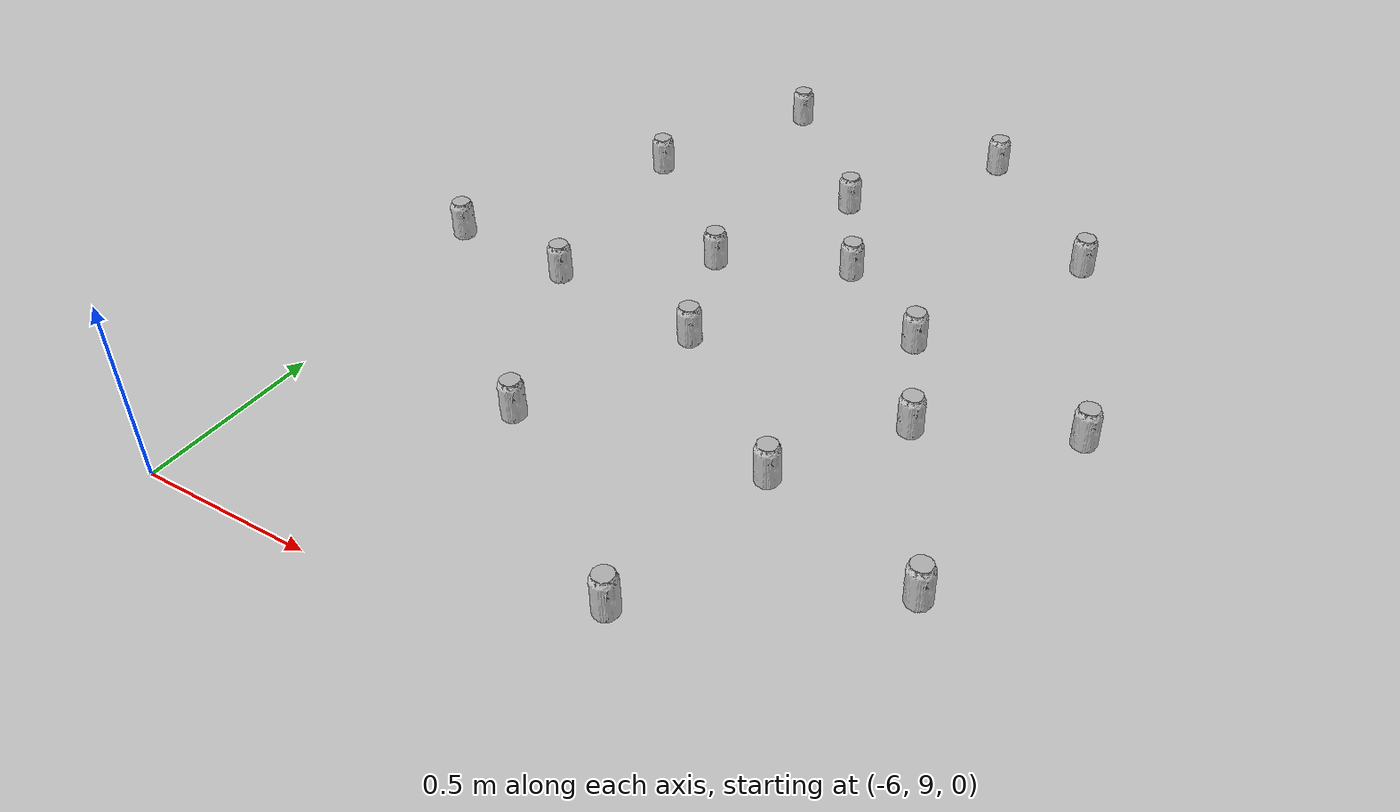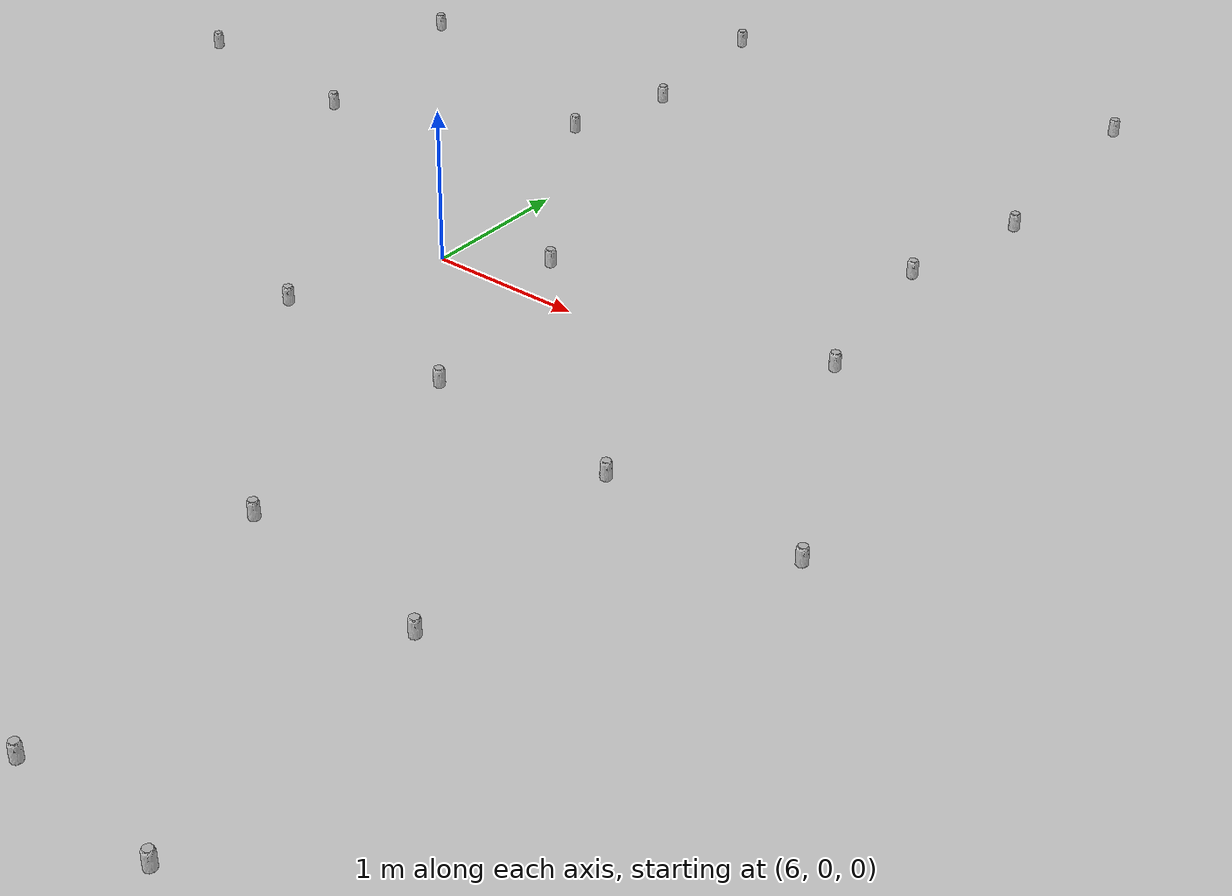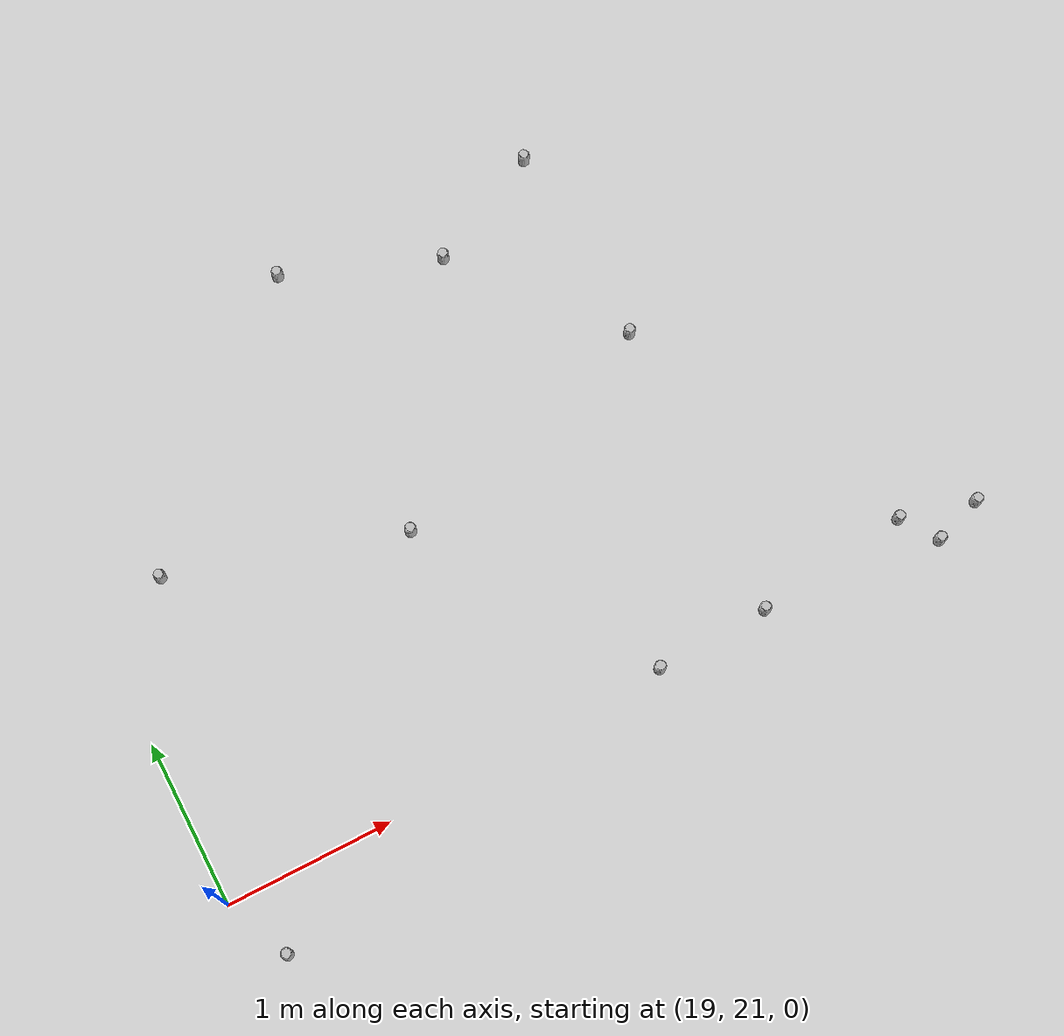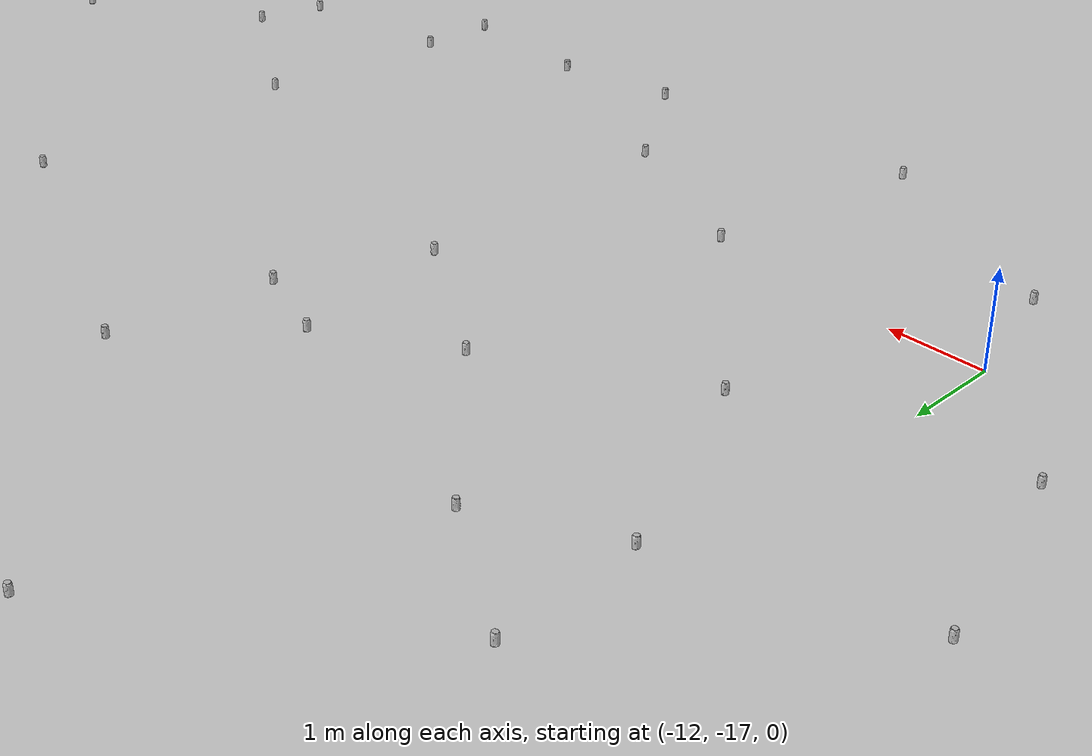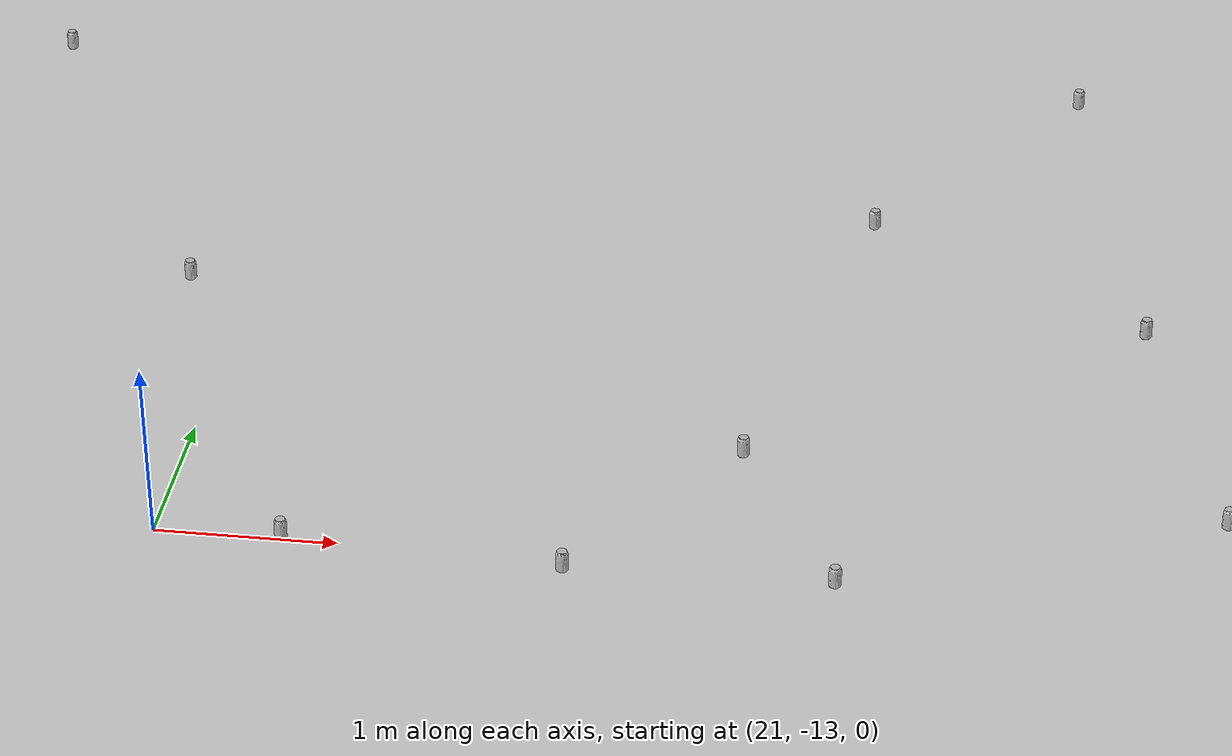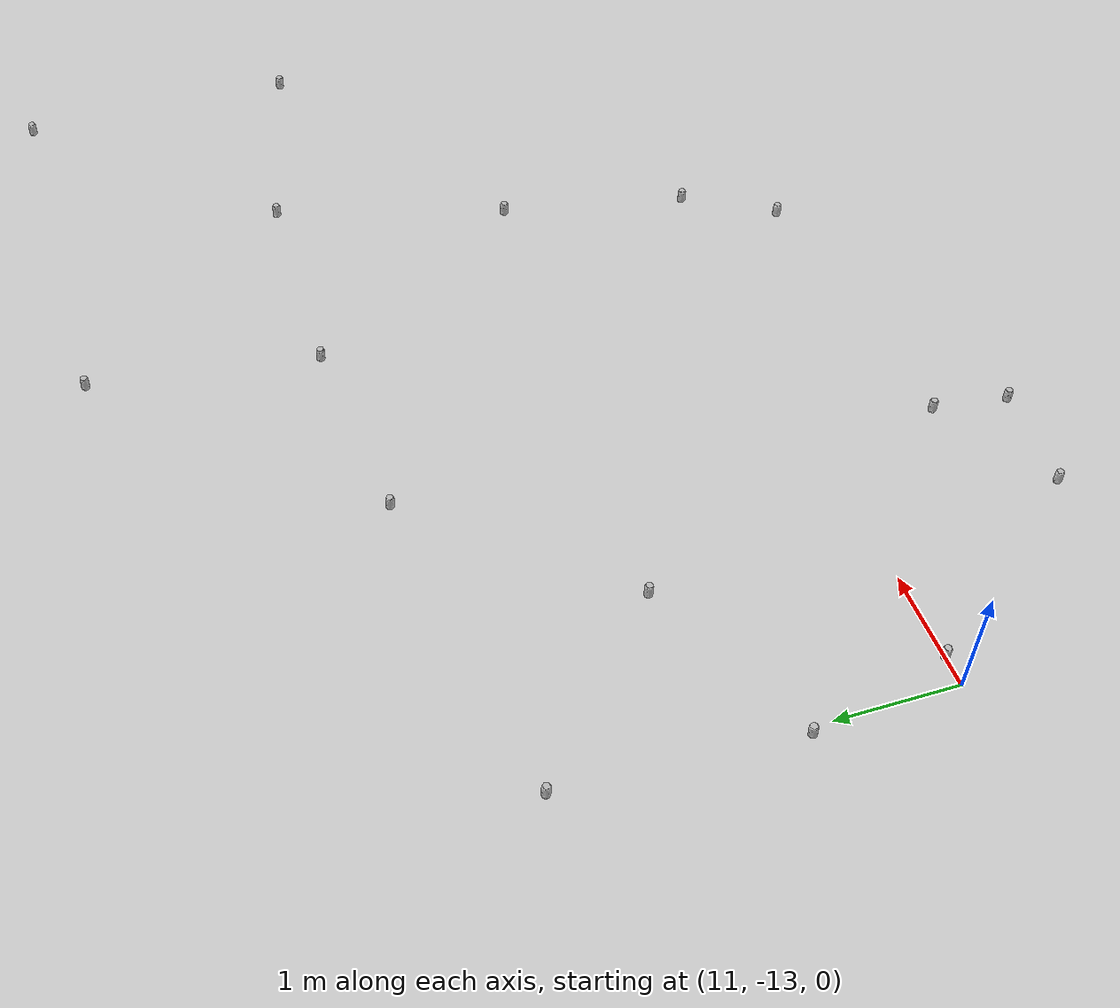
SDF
<sdf version="1.7">
 <world name="default">
  <model name="ground_plane">
   <static>1</static>
   <link name="link">
    <collision name="collision">
     <geometry><plane><normal>0 0 1</normal><size>100 100</size></plane></geometry>
     <surface>
      <contact><collide_bitmask>65535</collide_bitmask></contact>
      <friction><ode><mu>100</mu><mu2>50</mu2></ode></friction>
     </surface>
    </collision>
    <visual name="visual">
     <cast_shadows>0</cast_shadows>
     <geometry><plane><normal>0 0 1</normal><size>100 100</size></plane></geometry>
     <material>
      <script><uri>file://media/materials/scripts/gazebo.material</uri><name>Gazebo/Grey</name></script>
     </material>
    </visual>
   </link>
  </model>
  <light name="sun" type="directional">
   <pose>0 0 10 0 -0 0</pose>
   <diffuse>0.8 0.8 0.8 1</diffuse>
   <specular>0.2 0.2 0.2 1</specular>
   <attenuation>
    <range>1000</range>
    <constant>0.9</constant>
    <linear>0.01</linear>
    <quadratic>0.001</quadratic>
   </attenuation>
   <direction>-0.5 0.1 -0.9</direction>
   <spot><inner_angle>0</inner_angle><outer_angle>0</outer_angle><falloff>0</falloff></spot>
  </light>
  <gravity>0 0 -9.8</gravity>
  <magnetic_field>6e-06 2.3e-05 -4.2e-05</magnetic_field>
  <atmosphere type="adiabatic"/>
  <physics type="ode">
   <max_step_size>0.001</max_step_size>
   <real_time_factor>1</real_time_factor>
   <real_time_update_rate>1000</real_time_update_rate>
  </physics>
  <scene><ambient>0.4 0.4 0.4 1</ambient><background>0.7 0.7 0.7 1</background><shadows>1</shadows></scene>
  <spherical_coordinates>
   <surface_model>EARTH_WGS84</surface_model>
   <latitude_deg>0</latitude_deg>
   <longitude_deg>0</longitude_deg>
   <elevation>0</elevation>
   <heading_deg>0</heading_deg>
  </spherical_coordinates>
  <model name="can1">
   <link name="link">
    <inertial>
     <pose>0 0 0.06 0 -0 0</pose>
     <mass>0.39</mass>
     <inertia>
      <ixx>0.00055575</ixx>
      <ixy>0</ixy>
      <ixz>0</ixz>
      <iyy>0.00055575</iyy>
      <iyz>0</iyz>
      <izz>0.0001755</izz>
     </inertia>
    </inertial>
    <collision name="collision">
     <pose>0.003937 0.004724 -0.18 0 -0 0</pose>
     <geometry><mesh><uri>model://coke_can/meshes/coke_can.dae</uri></mesh></geometry>
     <surface>
      <friction><ode><mu>1</mu><mu2>1</mu2></ode></friction>
      <contact><ode><kp>1e+07</kp><kd>1</kd><min_depth>0.001</min_depth><max_vel>0.1</max_vel></ode></contact>
     </surface>
    </collision>
    <visual name="visual">
     <pose>0.003937 0.004724 -0.18 0 -0 0</pose>
     <geometry><mesh><uri>model://coke_can/meshes/coke_can.dae</uri></mesh></geometry>
    </visual>
   </link>
   <pose>0.999971 -7.5e-05 -0.003466 -0.037124 0.00691 -0.00074</pose>
  </model>
  <model name="coke_can">
   <link name="link">
    <inertial>
     <pose>0 0 0.06 0 -0 0</pose>
     <mass>0.39</mass>
     <inertia>
      <ixx>0.00055575</ixx>
      <ixy>0</ixy>
      <ixz>0</ixz>
      <iyy>0.00055575</iyy>
      <iyz>0</iyz>
      <izz>0.0001755</izz>
     </inertia>
    </inertial>
    <collision name="collision">
     <pose>0.003937 0.004724 -0.18 0 -0 0</pose>
     <geometry><mesh><uri>model://coke_can/meshes/coke_can.dae</uri></mesh></geometry>
     <surface>
      <friction><ode><mu>1</mu><mu2>1</mu2></ode></friction>
      <contact><ode><kp>1e+07</kp><kd>1</kd><min_depth>0.001</min_depth><max_vel>0.1</max_vel></ode></contact>
     </surface>
    </collision>
    <visual name="visual">
     <pose>0.003937 0.004724 -0.18 0 -0 0</pose>
     <geometry><mesh><uri>model://coke_can/meshes/coke_can.dae</uri></mesh></geometry>
    </visual>
   </link>
   <pose>10.942 -11.8161 -0.002946 -0.063233 -0.00915 -0.000611</pose>
  </model>
  <model name="coke_can_0">
   <link name="link">
    <inertial>
     <pose>0 0 0.06 0 -0 0</pose>
     <mass>0.39</mass>
     <inertia>
      <ixx>0.00055575</ixx>
      <ixy>0</ixy>
      <ixz>0</ixz>
      <iyy>0.00055575</iyy>
      <iyz>0</iyz>
      <izz>0.0001755</izz>
     </inertia>
    </inertial>
    <collision name="collision">
     <pose>0.003937 0.004724 -0.18 0 -0 0</pose>
     <geometry><mesh><uri>model://coke_can/meshes/coke_can.dae</uri></mesh></geometry>
     <surface>
      <friction><ode><mu>1</mu><mu2>1</mu2></ode></friction>
      <contact><ode><kp>1e+07</kp><kd>1</kd><min_depth>0.001</min_depth><max_vel>0.1</max_vel></ode></contact>
     </surface>
    </collision>
    <visual name="visual">
     <pose>0.003937 0.004724 -0.18 0 -0 0</pose>
     <geometry><mesh><uri>model://coke_can/meshes/coke_can.dae</uri></mesh></geometry>
    </visual>
   </link>
   <pose>11.1455 -5.23445 -0.002897 -0.064079 -0.005744 -0.000583</pose>
  </model>
  <model name="coke_can_1">
   <link name="link">
    <inertial>
     <pose>0 0 0.06 0 -0 0</pose>
     <mass>0.39</mass>
     <inertia>
      <ixx>0.00055575</ixx>
      <ixy>0</ixy>
      <ixz>0</ixz>
      <iyy>0.00055575</iyy>
      <iyz>0</iyz>
      <izz>0.0001755</izz>
     </inertia>
    </inertial>
    <collision name="collision">
     <pose>0.003937 0.004724 -0.18 0 -0 0</pose>
     <geometry><mesh><uri>model://coke_can/meshes/coke_can.dae</uri></mesh></geometry>
     <surface>
      <friction><ode><mu>1</mu><mu2>1</mu2></ode></friction>
      <contact><ode><kp>1e+07</kp><kd>1</kd><min_depth>0.001</min_depth><max_vel>0.1</max_vel></ode></contact>
     </surface>
    </collision>
    <visual name="visual">
     <pose>0.003937 0.004724 -0.18 0 -0 0</pose>
     <geometry><mesh><uri>model://coke_can/meshes/coke_can.dae</uri></mesh></geometry>
    </visual>
   </link>
   <pose>8.62314 -8.29553 -0.002853 -0.064236 -0.002973 -0.000572</pose>
  </model>
  <model name="coke_can_2">
   <link name="link">
    <inertial>
     <pose>0 0 0.06 0 -0 0</pose>
     <mass>0.39</mass>
     <inertia>
      <ixx>0.00055575</ixx>
      <ixy>0</ixy>
      <ixz>0</ixz>
      <iyy>0.00055575</iyy>
      <iyz>0</iyz>
      <izz>0.0001755</izz>
     </inertia>
    </inertial>
    <collision name="collision">
     <pose>0.003937 0.004724 -0.18 0 -0 0</pose>
     <geometry><mesh><uri>model://coke_can/meshes/coke_can.dae</uri></mesh></geometry>
     <surface>
      <friction><ode><mu>1</mu><mu2>1</mu2></ode></friction>
      <contact><ode><kp>1e+07</kp><kd>1</kd><min_depth>0.001</min_depth><max_vel>0.1</max_vel></ode></contact>
     </surface>
    </collision>
    <visual name="visual">
     <pose>0.003937 0.004724 -0.18 0 -0 0</pose>
     <geometry><mesh><uri>model://coke_can/meshes/coke_can.dae</uri></mesh></geometry>
    </visual>
   </link>
   <pose>4.9754 -11.8346 -0.00281 -0.064298 -0.000266 -0.000586</pose>
  </model>
  <model name="coke_can_3">
   <link name="link">
    <inertial>
     <pose>0 0 0.06 0 -0 0</pose>
     <mass>0.39</mass>
     <inertia>
      <ixx>0.00055575</ixx>
      <ixy>0</ixy>
      <ixz>0</ixz>
      <iyy>0.00055575</iyy>
      <iyz>0</iyz>
      <izz>0.0001755</izz>
     </inertia>
    </inertial>
    <collision name="collision">
     <pose>0.003937 0.004724 -0.18 0 -0 0</pose>
     <geometry><mesh><uri>model://coke_can/meshes/coke_can.dae</uri></mesh></geometry>
     <surface>
      <friction><ode><mu>1</mu><mu2>1</mu2></ode></friction>
      <contact><ode><kp>1e+07</kp><kd>1</kd><min_depth>0.001</min_depth><max_vel>0.1</max_vel></ode></contact>
     </surface>
    </collision>
    <visual name="visual">
     <pose>0.003937 0.004724 -0.18 0 -0 0</pose>
     <geometry><mesh><uri>model://coke_can/meshes/coke_can.dae</uri></mesh></geometry>
    </visual>
   </link>
   <pose>8.28778 -11.9997 -0.002778 -0.062285 0.002774 -0.000557</pose>
  </model>
  <model name="coke_can_4">
   <link name="link">
    <inertial>
     <pose>0 0 0.06 0 -0 0</pose>
     <mass>0.39</mass>
     <inertia>
      <ixx>0.00055575</ixx>
      <ixy>0</ixy>
      <ixz>0</ixz>
      <iyy>0.00055575</iyy>
      <iyz>0</iyz>
      <izz>0.0001755</izz>
     </inertia>
    </inertial>
    <collision name="collision">
     <pose>0.003937 0.004724 -0.18 0 -0 0</pose>
     <geometry><mesh><uri>model://coke_can/meshes/coke_can.dae</uri></mesh></geometry>
     <surface>
      <friction><ode><mu>1</mu><mu2>1</mu2></ode></friction>
      <contact><ode><kp>1e+07</kp><kd>1</kd><min_depth>0.001</min_depth><max_vel>0.1</max_vel></ode></contact>
     </surface>
    </collision>
    <visual name="visual">
     <pose>0.003937 0.004724 -0.18 0 -0 0</pose>
     <geometry><mesh><uri>model://coke_can/meshes/coke_can.dae</uri></mesh></geometry>
    </visual>
   </link>
   <pose>2.67102 -11.7073 -0.002748 -0.060406 0.004076 -0.000539</pose>
  </model>
  <model name="coke_can_5">
   <link name="link">
    <inertial>
     <pose>0 0 0.06 0 -0 0</pose>
     <mass>0.39</mass>
     <inertia>
      <ixx>0.00055575</ixx>
      <ixy>0</ixy>
      <ixz>0</ixz>
      <iyy>0.00055575</iyy>
      <iyz>0</iyz>
      <izz>0.0001755</izz>
     </inertia>
    </inertial>
    <collision name="collision">
     <pose>0.003937 0.004724 -0.18 0 -0 0</pose>
     <geometry><mesh><uri>model://coke_can/meshes/coke_can.dae</uri></mesh></geometry>
     <surface>
      <friction><ode><mu>1</mu><mu2>1</mu2></ode></friction>
      <contact><ode><kp>1e+07</kp><kd>1</kd><min_depth>0.001</min_depth><max_vel>0.1</max_vel></ode></contact>
     </surface>
    </collision>
    <visual name="visual">
     <pose>0.003937 0.004724 -0.18 0 -0 0</pose>
     <geometry><mesh><uri>model://coke_can/meshes/coke_can.dae</uri></mesh></geometry>
    </visual>
   </link>
   <pose>0.950383 -10.0438 -0.002718 -0.058579 0.00534 -0.00052</pose>
  </model>
  <model name="coke_can_6">
   <link name="link">
    <inertial>
     <pose>0 0 0.06 0 -0 0</pose>
     <mass>0.39</mass>
     <inertia>
      <ixx>0.00055575</ixx>
      <ixy>0</ixy>
      <ixz>0</ixz>
      <iyy>0.00055575</iyy>
      <iyz>0</iyz>
      <izz>0.0001755</izz>
     </inertia>
    </inertial>
    <collision name="collision">
     <pose>0.003937 0.004724 -0.18 0 -0 0</pose>
     <geometry><mesh><uri>model://coke_can/meshes/coke_can.dae</uri></mesh></geometry>
     <surface>
      <friction><ode><mu>1</mu><mu2>1</mu2></ode></friction>
      <contact><ode><kp>1e+07</kp><kd>1</kd><min_depth>0.001</min_depth><max_vel>0.1</max_vel></ode></contact>
     </surface>
    </collision>
    <visual name="visual">
     <pose>0.003937 0.004724 -0.18 0 -0 0</pose>
     <geometry><mesh><uri>model://coke_can/meshes/coke_can.dae</uri></mesh></geometry>
    </visual>
   </link>
   <pose>-1.32642 -11.9816 -0.002681 -0.056371 0.00687 -0.000497</pose>
  </model>
  <model name="coke_can_7">
   <link name="link">
    <inertial>
     <pose>0 0 0.06 0 -0 0</pose>
     <mass>0.39</mass>
     <inertia>
      <ixx>0.00055575</ixx>
      <ixy>0</ixy>
      <ixz>0</ixz>
      <iyy>0.00055575</iyy>
      <iyz>0</iyz>
      <izz>0.0001755</izz>
     </inertia>
    </inertial>
    <collision name="collision">
     <pose>0.003937 0.004724 -0.18 0 -0 0</pose>
     <geometry><mesh><uri>model://coke_can/meshes/coke_can.dae</uri></mesh></geometry>
     <surface>
      <friction><ode><mu>1</mu><mu2>1</mu2></ode></friction>
      <contact><ode><kp>1e+07</kp><kd>1</kd><min_depth>0.001</min_depth><max_vel>0.1</max_vel></ode></contact>
     </surface>
    </collision>
    <visual name="visual">
     <pose>0.003937 0.004724 -0.18 0 -0 0</pose>
     <geometry><mesh><uri>model://coke_can/meshes/coke_can.dae</uri></mesh></geometry>
    </visual>
   </link>
   <pose>-2.94773 -9.879 -0.002659 -0.055112 0.007741 -0.000483</pose>
  </model>
  <model name="coke_can_8">
   <link name="link">
    <inertial>
     <pose>0 0 0.06 0 -0 0</pose>
     <mass>0.39</mass>
     <inertia>
      <ixx>0.00055575</ixx>
      <ixy>0</ixy>
      <ixz>0</ixz>
      <iyy>0.00055575</iyy>
      <iyz>0</iyz>
      <izz>0.0001755</izz>
     </inertia>
    </inertial>
    <collision name="collision">
     <pose>0.003937 0.004724 -0.18 0 -0 0</pose>
     <geometry><mesh><uri>model://coke_can/meshes/coke_can.dae</uri></mesh></geometry>
     <surface>
      <friction><ode><mu>1</mu><mu2>1</mu2></ode></friction>
      <contact><ode><kp>1e+07</kp><kd>1</kd><min_depth>0.001</min_depth><max_vel>0.1</max_vel></ode></contact>
     </surface>
    </collision>
    <visual name="visual">
     <pose>0.003937 0.004724 -0.18 0 -0 0</pose>
     <geometry><mesh><uri>model://coke_can/meshes/coke_can.dae</uri></mesh></geometry>
    </visual>
   </link>
   <pose>-1.1155 -9.32057 0 0 -0 0</pose>
  </model>
  <model name="coke_can_9">
   <link name="link">
    <inertial>
     <pose>0 0 0.06 0 -0 0</pose>
     <mass>0.39</mass>
     <inertia>
      <ixx>0.00055575</ixx>
      <ixy>0</ixy>
      <ixz>0</ixz>
      <iyy>0.00055575</iyy>
      <iyz>0</iyz>
      <izz>0.0001755</izz>
     </inertia>
    </inertial>
    <collision name="collision">
     <pose>0.003937 0.004724 -0.18 0 -0 0</pose>
     <geometry><mesh><uri>model://coke_can/meshes/coke_can.dae</uri></mesh></geometry>
     <surface>
      <friction><ode><mu>1</mu><mu2>1</mu2></ode></friction>
      <contact><ode><kp>1e+07</kp><kd>1</kd><min_depth>0.001</min_depth><max_vel>0.1</max_vel></ode></contact>
     </surface>
    </collision>
    <visual name="visual">
     <pose>0.003937 0.004724 -0.18 0 -0 0</pose>
     <geometry><mesh><uri>model://coke_can/meshes/coke_can.dae</uri></mesh></geometry>
    </visual>
   </link>
   <pose>-6.22761 -12.0071 0 0 -0 0</pose>
  </model>
  <model name="coke_can_10">
   <link name="link">
    <inertial>
     <pose>0 0 0.06 0 -0 0</pose>
     <mass>0.39</mass>
     <inertia>
      <ixx>0.00055575</ixx>
      <ixy>0</ixy>
      <ixz>0</ixz>
      <iyy>0.00055575</iyy>
      <iyz>0</iyz>
      <izz>0.0001755</izz>
     </inertia>
    </inertial>
    <collision name="collision">
     <pose>0.003937 0.004724 -0.18 0 -0 0</pose>
     <geometry><mesh><uri>model://coke_can/meshes/coke_can.dae</uri></mesh></geometry>
     <surface>
      <friction><ode><mu>1</mu><mu2>1</mu2></ode></friction>
      <contact><ode><kp>1e+07</kp><kd>1</kd><min_depth>0.001</min_depth><max_vel>0.1</max_vel></ode></contact>
     </surface>
    </collision>
    <visual name="visual">
     <pose>0.003937 0.004724 -0.18 0 -0 0</pose>
     <geometry><mesh><uri>model://coke_can/meshes/coke_can.dae</uri></mesh></geometry>
    </visual>
   </link>
   <pose>-7.00292 -9.9999 0 0 -0 0</pose>
  </model>
  <model name="coke_can_11">
   <link name="link">
    <inertial>
     <pose>0 0 0.06 0 -0 0</pose>
     <mass>0.39</mass>
     <inertia>
      <ixx>0.00055575</ixx>
      <ixy>0</ixy>
      <ixz>0</ixz>
      <iyy>0.00055575</iyy>
      <iyz>0</iyz>
      <izz>0.0001755</izz>
     </inertia>
    </inertial>
    <collision name="collision">
     <pose>0.003937 0.004724 -0.18 0 -0 0</pose>
     <geometry><mesh><uri>model://coke_can/meshes/coke_can.dae</uri></mesh></geometry>
     <surface>
      <friction><ode><mu>1</mu><mu2>1</mu2></ode></friction>
      <contact><ode><kp>1e+07</kp><kd>1</kd><min_depth>0.001</min_depth><max_vel>0.1</max_vel></ode></contact>
     </surface>
    </collision>
    <visual name="visual">
     <pose>0.003937 0.004724 -0.18 0 -0 0</pose>
     <geometry><mesh><uri>model://coke_can/meshes/coke_can.dae</uri></mesh></geometry>
    </visual>
   </link>
   <pose>-7.3044 -9.62463 0 0 -0 0</pose>
  </model>
  <model name="coke_can_12">
   <link name="link">
    <inertial>
     <pose>0 0 0.06 0 -0 0</pose>
     <mass>0.39</mass>
     <inertia>
      <ixx>0.00055575</ixx>
      <ixy>0</ixy>
      <ixz>0</ixz>
      <iyy>0.00055575</iyy>
      <iyz>0</iyz>
      <izz>0.0001755</izz>
     </inertia>
    </inertial>
    <collision name="collision">
     <pose>0.003937 0.004724 -0.18 0 -0 0</pose>
     <geometry><mesh><uri>model://coke_can/meshes/coke_can.dae</uri></mesh></geometry>
     <surface>
      <friction><ode><mu>1</mu><mu2>1</mu2></ode></friction>
      <contact><ode><kp>1e+07</kp><kd>1</kd><min_depth>0.001</min_depth><max_vel>0.1</max_vel></ode></contact>
     </surface>
    </collision>
    <visual name="visual">
     <pose>0.003937 0.004724 -0.18 0 -0 0</pose>
     <geometry><mesh><uri>model://coke_can/meshes/coke_can.dae</uri></mesh></geometry>
    </visual>
   </link>
   <pose>-7.13261 -15.1029 0 0 -0 0</pose>
  </model>
  <model name="coke_can_13">
   <link name="link">
    <inertial>
     <pose>0 0 0.06 0 -0 0</pose>
     <mass>0.39</mass>
     <inertia>
      <ixx>0.00055575</ixx>
      <ixy>0</ixy>
      <ixz>0</ixz>
      <iyy>0.00055575</iyy>
      <iyz>0</iyz>
      <izz>0.0001755</izz>
     </inertia>
    </inertial>
    <collision name="collision">
     <pose>0.003937 0.004724 -0.18 0 -0 0</pose>
     <geometry><mesh><uri>model://coke_can/meshes/coke_can.dae</uri></mesh></geometry>
     <surface>
      <friction><ode><mu>1</mu><mu2>1</mu2></ode></friction>
      <contact><ode><kp>1e+07</kp><kd>1</kd><min_depth>0.001</min_depth><max_vel>0.1</max_vel></ode></contact>
     </surface>
    </collision>
    <visual name="visual">
     <pose>0.003937 0.004724 -0.18 0 -0 0</pose>
     <geometry><mesh><uri>model://coke_can/meshes/coke_can.dae</uri></mesh></geometry>
    </visual>
   </link>
   <pose>-6.50044 -13.6703 0 0 -0 0</pose>
  </model>
  <model name="coke_can_14">
   <link name="link">
    <inertial>
     <pose>0 0 0.06 0 -0 0</pose>
     <mass>0.39</mass>
     <inertia>
      <ixx>0.00055575</ixx>
      <ixy>0</ixy>
      <ixz>0</ixz>
      <iyy>0.00055575</iyy>
      <iyz>0</iyz>
      <izz>0.0001755</izz>
     </inertia>
    </inertial>
    <collision name="collision">
     <pose>0.003937 0.004724 -0.18 0 -0 0</pose>
     <geometry><mesh><uri>model://coke_can/meshes/coke_can.dae</uri></mesh></geometry>
     <surface>
      <friction><ode><mu>1</mu><mu2>1</mu2></ode></friction>
      <contact><ode><kp>1e+07</kp><kd>1</kd><min_depth>0.001</min_depth><max_vel>0.1</max_vel></ode></contact>
     </surface>
    </collision>
    <visual name="visual">
     <pose>0.003937 0.004724 -0.18 0 -0 0</pose>
     <geometry><mesh><uri>model://coke_can/meshes/coke_can.dae</uri></mesh></geometry>
    </visual>
   </link>
   <pose>-7.38565 -13.3334 0 0 -0 0</pose>
  </model>
  <model name="coke_can_15">
   <link name="link">
    <inertial>
     <pose>0 0 0.06 0 -0 0</pose>
     <mass>0.39</mass>
     <inertia>
      <ixx>0.00055575</ixx>
      <ixy>0</ixy>
      <ixz>0</ixz>
      <iyy>0.00055575</iyy>
      <iyz>0</iyz>
      <izz>0.0001755</izz>
     </inertia>
    </inertial>
    <collision name="collision">
     <pose>0.003937 0.004724 -0.18 0 -0 0</pose>
     <geometry><mesh><uri>model://coke_can/meshes/coke_can.dae</uri></mesh></geometry>
     <surface>
      <friction><ode><mu>1</mu><mu2>1</mu2></ode></friction>
      <contact><ode><kp>1e+07</kp><kd>1</kd><min_depth>0.001</min_depth><max_vel>0.1</max_vel></ode></contact>
     </surface>
    </collision>
    <visual name="visual">
     <pose>0.003937 0.004724 -0.18 0 -0 0</pose>
     <geometry><mesh><uri>model://coke_can/meshes/coke_can.dae</uri></mesh></geometry>
    </visual>
   </link>
   <pose>-4.95901 -19.1827 0 0 -0 0</pose>
  </model>
  <model name="coke_can_16">
   <link name="link">
    <inertial>
     <pose>0 0 0.06 0 -0 0</pose>
     <mass>0.39</mass>
     <inertia>
      <ixx>0.00055575</ixx>
      <ixy>0</ixy>
      <ixz>0</ixz>
      <iyy>0.00055575</iyy>
      <iyz>0</iyz>
      <izz>0.0001755</izz>
     </inertia>
    </inertial>
    <collision name="collision">
     <pose>0.003937 0.004724 -0.18 0 -0 0</pose>
     <geometry><mesh><uri>model://coke_can/meshes/coke_can.dae</uri></mesh></geometry>
     <surface>
      <friction><ode><mu>1</mu><mu2>1</mu2></ode></friction>
      <contact><ode><kp>1e+07</kp><kd>1</kd><min_depth>0.001</min_depth><max_vel>0.1</max_vel></ode></contact>
     </surface>
    </collision>
    <visual name="visual">
     <pose>0.003937 0.004724 -0.18 0 -0 0</pose>
     <geometry><mesh><uri>model://coke_can/meshes/coke_can.dae</uri></mesh></geometry>
    </visual>
   </link>
   <pose>-6.27065 -19.3738 0 0 -0 0</pose>
  </model>
  <model name="coke_can_17">
   <link name="link">
    <inertial>
     <pose>0 0 0.06 0 -0 0</pose>
     <mass>0.39</mass>
     <inertia>
      <ixx>0.00055575</ixx>
      <ixy>0</ixy>
      <ixz>0</ixz>
      <iyy>0.00055575</iyy>
      <iyz>0</iyz>
      <izz>0.0001755</izz>
     </inertia>
    </inertial>
    <collision name="collision">
     <pose>0.003937 0.004724 -0.18 0 -0 0</pose>
     <geometry><mesh><uri>model://coke_can/meshes/coke_can.dae</uri></mesh></geometry>
     <surface>
      <friction><ode><mu>1</mu><mu2>1</mu2></ode></friction>
      <contact><ode><kp>1e+07</kp><kd>1</kd><min_depth>0.001</min_depth><max_vel>0.1</max_vel></ode></contact>
     </surface>
    </collision>
    <visual name="visual">
     <pose>0.003937 0.004724 -0.18 0 -0 0</pose>
     <geometry><mesh><uri>model://coke_can/meshes/coke_can.dae</uri></mesh></geometry>
    </visual>
   </link>
   <pose>-7.09739 -18.1226 0 0 -0 0</pose>
  </model>
  <model name="coke_can_18">
   <link name="link">
    <inertial>
     <pose>0 0 0.06 0 -0 0</pose>
     <mass>0.39</mass>
     <inertia>
      <ixx>0.00055575</ixx>
      <ixy>0</ixy>
      <ixz>0</ixz>
      <iyy>0.00055575</iyy>
      <iyz>0</iyz>
      <izz>0.0001755</izz>
     </inertia>
    </inertial>
    <collision name="collision">
     <pose>0.003937 0.004724 -0.18 0 -0 0</pose>
     <geometry><mesh><uri>model://coke_can/meshes/coke_can.dae</uri></mesh></geometry>
     <surface>
      <friction><ode><mu>1</mu><mu2>1</mu2></ode></friction>
      <contact><ode><kp>1e+07</kp><kd>1</kd><min_depth>0.001</min_depth><max_vel>0.1</max_vel></ode></contact>
     </surface>
    </collision>
    <visual name="visual">
     <pose>0.003937 0.004724 -0.18 0 -0 0</pose>
     <geometry><mesh><uri>model://coke_can/meshes/coke_can.dae</uri></mesh></geometry>
    </visual>
   </link>
   <pose>-1.44413 -19.1499 0 0 -0 0</pose>
  </model>
  <model name="coke_can_19">
   <link name="link">
    <inertial>
     <pose>0 0 0.06 0 -0 0</pose>
     <mass>0.39</mass>
     <inertia>
      <ixx>0.00055575</ixx>
      <ixy>0</ixy>
      <ixz>0</ixz>
      <iyy>0.00055575</iyy>
      <iyz>0</iyz>
      <izz>0.0001755</izz>
     </inertia>
    </inertial>
    <collision name="collision">
     <pose>0.003937 0.004724 -0.18 0 -0 0</pose>
     <geometry><mesh><uri>model://coke_can/meshes/coke_can.dae</uri></mesh></geometry>
     <surface>
      <friction><ode><mu>1</mu><mu2>1</mu2></ode></friction>
      <contact><ode><kp>1e+07</kp><kd>1</kd><min_depth>0.001</min_depth><max_vel>0.1</max_vel></ode></contact>
     </surface>
    </collision>
    <visual name="visual">
     <pose>0.003937 0.004724 -0.18 0 -0 0</pose>
     <geometry><mesh><uri>model://coke_can/meshes/coke_can.dae</uri></mesh></geometry>
    </visual>
   </link>
   <pose>-1.33882 -17.6682 0 0 -0 0</pose>
  </model>
  <model name="coke_can_20">
   <link name="link">
    <inertial>
     <pose>0 0 0.06 0 -0 0</pose>
     <mass>0.39</mass>
     <inertia>
      <ixx>0.00055575</ixx>
      <ixy>0</ixy>
      <ixz>0</ixz>
      <iyy>0.00055575</iyy>
      <iyz>0</iyz>
      <izz>0.0001755</izz>
     </inertia>
    </inertial>
    <collision name="collision">
     <pose>0.003937 0.004724 -0.18 0 -0 0</pose>
     <geometry><mesh><uri>model://coke_can/meshes/coke_can.dae</uri></mesh></geometry>
     <surface>
      <friction><ode><mu>1</mu><mu2>1</mu2></ode></friction>
      <contact><ode><kp>1e+07</kp><kd>1</kd><min_depth>0.001</min_depth><max_vel>0.1</max_vel></ode></contact>
     </surface>
    </collision>
    <visual name="visual">
     <pose>0.003937 0.004724 -0.18 0 -0 0</pose>
     <geometry><mesh><uri>model://coke_can/meshes/coke_can.dae</uri></mesh></geometry>
    </visual>
   </link>
   <pose>-1.5495 -18.395 0 0 -0 0</pose>
  </model>
  <model name="coke_can_21">
   <link name="link">
    <inertial>
     <pose>0 0 0.06 0 -0 0</pose>
     <mass>0.39</mass>
     <inertia>
      <ixx>0.00055575</ixx>
      <ixy>0</ixy>
      <ixz>0</ixz>
      <iyy>0.00055575</iyy>
      <iyz>0</iyz>
      <izz>0.0001755</izz>
     </inertia>
    </inertial>
    <collision name="collision">
     <pose>0.003937 0.004724 -0.18 0 -0 0</pose>
     <geometry><mesh><uri>model://coke_can/meshes/coke_can.dae</uri></mesh></geometry>
     <surface>
      <friction><ode><mu>1</mu><mu2>1</mu2></ode></friction>
      <contact><ode><kp>1e+07</kp><kd>1</kd><min_depth>0.001</min_depth><max_vel>0.1</max_vel></ode></contact>
     </surface>
    </collision>
    <visual name="visual">
     <pose>0.003937 0.004724 -0.18 0 -0 0</pose>
     <geometry><mesh><uri>model://coke_can/meshes/coke_can.dae</uri></mesh></geometry>
    </visual>
   </link>
   <pose>-3.34856 -18.5576 0 0 -0 0</pose>
  </model>
  <model name="coke_can_22">
   <link name="link">
    <inertial>
     <pose>0 0 0.06 0 -0 0</pose>
     <mass>0.39</mass>
     <inertia>
      <ixx>0.00055575</ixx>
      <ixy>0</ixy>
      <ixz>0</ixz>
      <iyy>0.00055575</iyy>
      <iyz>0</iyz>
      <izz>0.0001755</izz>
     </inertia>
    </inertial>
    <collision name="collision">
     <pose>0.003937 0.004724 -0.18 0 -0 0</pose>
     <geometry><mesh><uri>model://coke_can/meshes/coke_can.dae</uri></mesh></geometry>
     <surface>
      <friction><ode><mu>1</mu><mu2>1</mu2></ode></friction>
      <contact><ode><kp>1e+07</kp><kd>1</kd><min_depth>0.001</min_depth><max_vel>0.1</max_vel></ode></contact>
     </surface>
    </collision>
    <visual name="visual">
     <pose>0.003937 0.004724 -0.18 0 -0 0</pose>
     <geometry><mesh><uri>model://coke_can/meshes/coke_can.dae</uri></mesh></geometry>
    </visual>
   </link>
   <pose>-3.41854 -19.3723 0 0 -0 0</pose>
  </model>
  <model name="coke_can_23">
   <link name="link">
    <inertial>
     <pose>0 0 0.06 0 -0 0</pose>
     <mass>0.39</mass>
     <inertia>
      <ixx>0.00055575</ixx>
      <ixy>0</ixy>
      <ixz>0</ixz>
      <iyy>0.00055575</iyy>
      <iyz>0</iyz>
      <izz>0.0001755</izz>
     </inertia>
    </inertial>
    <collision name="collision">
     <pose>0.003937 0.004724 -0.18 0 -0 0</pose>
     <geometry><mesh><uri>model://coke_can/meshes/coke_can.dae</uri></mesh></geometry>
     <surface>
      <friction><ode><mu>1</mu><mu2>1</mu2></ode></friction>
      <contact><ode><kp>1e+07</kp><kd>1</kd><min_depth>0.001</min_depth><max_vel>0.1</max_vel></ode></contact>
     </surface>
    </collision>
    <visual name="visual">
     <pose>0.003937 0.004724 -0.18 0 -0 0</pose>
     <geometry><mesh><uri>model://coke_can/meshes/coke_can.dae</uri></mesh></geometry>
    </visual>
   </link>
   <pose>0.586481 -16.5608 0 0 -0 0</pose>
  </model>
  <model name="coke_can_24">
   <link name="link">
    <inertial>
     <pose>0 0 0.06 0 -0 0</pose>
     <mass>0.39</mass>
     <inertia>
      <ixx>0.00055575</ixx>
      <ixy>0</ixy>
      <ixz>0</ixz>
      <iyy>0.00055575</iyy>
      <iyz>0</iyz>
      <izz>0.0001755</izz>
     </inertia>
    </inertial>
    <collision name="collision">
     <pose>0.003937 0.004724 -0.18 0 -0 0</pose>
     <geometry><mesh><uri>model://coke_can/meshes/coke_can.dae</uri></mesh></geometry>
     <surface>
      <friction><ode><mu>1</mu><mu2>1</mu2></ode></friction>
      <contact><ode><kp>1e+07</kp><kd>1</kd><min_depth>0.001</min_depth><max_vel>0.1</max_vel></ode></contact>
     </surface>
    </collision>
    <visual name="visual">
     <pose>0.003937 0.004724 -0.18 0 -0 0</pose>
     <geometry><mesh><uri>model://coke_can/meshes/coke_can.dae</uri></mesh></geometry>
    </visual>
   </link>
   <pose>-3.03541 -16.4978 0 0 -0 0</pose>
  </model>
  <model name="coke_can_25">
   <link name="link">
    <inertial>
     <pose>0 0 0.06 0 -0 0</pose>
     <mass>0.39</mass>
     <inertia>
      <ixx>0.00055575</ixx>
      <ixy>0</ixy>
      <ixz>0</ixz>
      <iyy>0.00055575</iyy>
      <iyz>0</iyz>
      <izz>0.0001755</izz>
     </inertia>
    </inertial>
    <collision name="collision">
     <pose>0.003937 0.004724 -0.18 0 -0 0</pose>
     <geometry><mesh><uri>model://coke_can/meshes/coke_can.dae</uri></mesh></geometry>
     <surface>
      <friction><ode><mu>1</mu><mu2>1</mu2></ode></friction>
      <contact><ode><kp>1e+07</kp><kd>1</kd><min_depth>0.001</min_depth><max_vel>0.1</max_vel></ode></contact>
     </surface>
    </collision>
    <visual name="visual">
     <pose>0.003937 0.004724 -0.18 0 -0 0</pose>
     <geometry><mesh><uri>model://coke_can/meshes/coke_can.dae</uri></mesh></geometry>
    </visual>
   </link>
   <pose>2.33196 -19.0306 0 0 -0 0</pose>
  </model>
  <model name="coke_can_26">
   <link name="link">
    <inertial>
     <pose>0 0 0.06 0 -0 0</pose>
     <mass>0.39</mass>
     <inertia>
      <ixx>0.00055575</ixx>
      <ixy>0</ixy>
      <ixz>0</ixz>
      <iyy>0.00055575</iyy>
      <iyz>0</iyz>
      <izz>0.0001755</izz>
     </inertia>
    </inertial>
    <collision name="collision">
     <pose>0.003937 0.004724 -0.18 0 -0 0</pose>
     <geometry><mesh><uri>model://coke_can/meshes/coke_can.dae</uri></mesh></geometry>
     <surface>
      <friction><ode><mu>1</mu><mu2>1</mu2></ode></friction>
      <contact><ode><kp>1e+07</kp><kd>1</kd><min_depth>0.001</min_depth><max_vel>0.1</max_vel></ode></contact>
     </surface>
    </collision>
    <visual name="visual">
     <pose>0.003937 0.004724 -0.18 0 -0 0</pose>
     <geometry><mesh><uri>model://coke_can/meshes/coke_can.dae</uri></mesh></geometry>
    </visual>
   </link>
   <pose>1.04994 -17.6543 0 0 -0 0</pose>
  </model>
  <model name="coke_can_27">
   <link name="link">
    <inertial>
     <pose>0 0 0.06 0 -0 0</pose>
     <mass>0.39</mass>
     <inertia>
      <ixx>0.00055575</ixx>
      <ixy>0</ixy>
      <ixz>0</ixz>
      <iyy>0.00055575</iyy>
      <iyz>0</iyz>
      <izz>0.0001755</izz>
     </inertia>
    </inertial>
    <collision name="collision">
     <pose>0.003937 0.004724 -0.18 0 -0 0</pose>
     <geometry><mesh><uri>model://coke_can/meshes/coke_can.dae</uri></mesh></geometry>
     <surface>
      <friction><ode><mu>1</mu><mu2>1</mu2></ode></friction>
      <contact><ode><kp>1e+07</kp><kd>1</kd><min_depth>0.001</min_depth><max_vel>0.1</max_vel></ode></contact>
     </surface>
    </collision>
    <visual name="visual">
     <pose>0.003937 0.004724 -0.18 0 -0 0</pose>
     <geometry><mesh><uri>model://coke_can/meshes/coke_can.dae</uri></mesh></geometry>
    </visual>
   </link>
   <pose>2.64508 -14.8171 0 0 -0 0</pose>
  </model>
  <model name="coke_can_28">
   <link name="link">
    <inertial>
     <pose>0 0 0.06 0 -0 0</pose>
     <mass>0.39</mass>
     <inertia>
      <ixx>0.00055575</ixx>
      <ixy>0</ixy>
      <ixz>0</ixz>
      <iyy>0.00055575</iyy>
      <iyz>0</iyz>
      <izz>0.0001755</izz>
     </inertia>
    </inertial>
    <collision name="collision">
     <pose>0.003937 0.004724 -0.18 0 -0 0</pose>
     <geometry><mesh><uri>model://coke_can/meshes/coke_can.dae</uri></mesh></geometry>
     <surface>
      <friction><ode><mu>1</mu><mu2>1</mu2></ode></friction>
      <contact><ode><kp>1e+07</kp><kd>1</kd><min_depth>0.001</min_depth><max_vel>0.1</max_vel></ode></contact>
     </surface>
    </collision>
    <visual name="visual">
     <pose>0.003937 0.004724 -0.18 0 -0 0</pose>
     <geometry><mesh><uri>model://coke_can/meshes/coke_can.dae</uri></mesh></geometry>
    </visual>
   </link>
   <pose>1.3575 -14.9149 0 0 -0 0</pose>
  </model>
  <model name="coke_can_29">
   <link name="link">
    <inertial>
     <pose>0 0 0.06 0 -0 0</pose>
     <mass>0.39</mass>
     <inertia>
      <ixx>0.00055575</ixx>
      <ixy>0</ixy>
      <ixz>0</ixz>
      <iyy>0.00055575</iyy>
      <iyz>0</iyz>
      <izz>0.0001755</izz>
     </inertia>
    </inertial>
    <collision name="collision">
     <pose>0.003937 0.004724 -0.18 0 -0 0</pose>
     <geometry><mesh><uri>model://coke_can/meshes/coke_can.dae</uri></mesh></geometry>
     <surface>
      <friction><ode><mu>1</mu><mu2>1</mu2></ode></friction>
      <contact><ode><kp>1e+07</kp><kd>1</kd><min_depth>0.001</min_depth><max_vel>0.1</max_vel></ode></contact>
     </surface>
    </collision>
    <visual name="visual">
     <pose>0.003937 0.004724 -0.18 0 -0 0</pose>
     <geometry><mesh><uri>model://coke_can/meshes/coke_can.dae</uri></mesh></geometry>
    </visual>
   </link>
   <pose>1.60837 -13.8713 0 0 -0 0</pose>
  </model>
  <model name="coke_can_30">
   <link name="link">
    <inertial>
     <pose>0 0 0.06 0 -0 0</pose>
     <mass>0.39</mass>
     <inertia>
      <ixx>0.00055575</ixx>
      <ixy>0</ixy>
      <ixz>0</ixz>
      <iyy>0.00055575</iyy>
      <iyz>0</iyz>
      <izz>0.0001755</izz>
     </inertia>
    </inertial>
    <collision name="collision">
     <pose>0.003937 0.004724 -0.18 0 -0 0</pose>
     <geometry><mesh><uri>model://coke_can/meshes/coke_can.dae</uri></mesh></geometry>
     <surface>
      <friction><ode><mu>1</mu><mu2>1</mu2></ode></friction>
      <contact><ode><kp>1e+07</kp><kd>1</kd><min_depth>0.001</min_depth><max_vel>0.1</max_vel></ode></contact>
     </surface>
    </collision>
    <visual name="visual">
     <pose>0.003937 0.004724 -0.18 0 -0 0</pose>
     <geometry><mesh><uri>model://coke_can/meshes/coke_can.dae</uri></mesh></geometry>
    </visual>
   </link>
   <pose>6.25949 -14.6976 0 0 -0 0</pose>
  </model>
  <model name="coke_can_31">
   <link name="link">
    <inertial>
     <pose>0 0 0.06 0 -0 0</pose>
     <mass>0.39</mass>
     <inertia>
      <ixx>0.00055575</ixx>
      <ixy>0</ixy>
      <ixz>0</ixz>
      <iyy>0.00055575</iyy>
      <iyz>0</iyz>
      <izz>0.0001755</izz>
     </inertia>
    </inertial>
    <collision name="collision">
     <pose>0.003937 0.004724 -0.18 0 -0 0</pose>
     <geometry><mesh><uri>model://coke_can/meshes/coke_can.dae</uri></mesh></geometry>
     <surface>
      <friction><ode><mu>1</mu><mu2>1</mu2></ode></friction>
      <contact><ode><kp>1e+07</kp><kd>1</kd><min_depth>0.001</min_depth><max_vel>0.1</max_vel></ode></contact>
     </surface>
    </collision>
    <visual name="visual">
     <pose>0.003937 0.004724 -0.18 0 -0 0</pose>
     <geometry><mesh><uri>model://coke_can/meshes/coke_can.dae</uri></mesh></geometry>
    </visual>
   </link>
   <pose>6.06273 -12.8744 0 0 -0 0</pose>
  </model>
  <model name="coke_can_32">
   <link name="link">
    <inertial>
     <pose>0 0 0.06 0 -0 0</pose>
     <mass>0.39</mass>
     <inertia>
      <ixx>0.00055575</ixx>
      <ixy>0</ixy>
      <ixz>0</ixz>
      <iyy>0.00055575</iyy>
      <iyz>0</iyz>
      <izz>0.0001755</izz>
     </inertia>
    </inertial>
    <collision name="collision">
     <pose>0.003937 0.004724 -0.18 0 -0 0</pose>
     <geometry><mesh><uri>model://coke_can/meshes/coke_can.dae</uri></mesh></geometry>
     <surface>
      <friction><ode><mu>1</mu><mu2>1</mu2></ode></friction>
      <contact><ode><kp>1e+07</kp><kd>1</kd><min_depth>0.001</min_depth><max_vel>0.1</max_vel></ode></contact>
     </surface>
    </collision>
    <visual name="visual">
     <pose>0.003937 0.004724 -0.18 0 -0 0</pose>
     <geometry><mesh><uri>model://coke_can/meshes/coke_can.dae</uri></mesh></geometry>
    </visual>
   </link>
   <pose>4.53949 -13.1636 0 0 -0 0</pose>
  </model>
  <model name="coke_can_33">
   <link name="link">
    <inertial>
     <pose>0 0 0.06 0 -0 0</pose>
     <mass>0.39</mass>
     <inertia>
      <ixx>0.00055575</ixx>
      <ixy>0</ixy>
      <ixz>0</ixz>
      <iyy>0.00055575</iyy>
      <iyz>0</iyz>
      <izz>0.0001755</izz>
     </inertia>
    </inertial>
    <collision name="collision">
     <pose>0.003937 0.004724 -0.18 0 -0 0</pose>
     <geometry><mesh><uri>model://coke_can/meshes/coke_can.dae</uri></mesh></geometry>
     <surface>
      <friction><ode><mu>1</mu><mu2>1</mu2></ode></friction>
      <contact><ode><kp>1e+07</kp><kd>1</kd><min_depth>0.001</min_depth><max_vel>0.1</max_vel></ode></contact>
     </surface>
    </collision>
    <visual name="visual">
     <pose>0.003937 0.004724 -0.18 0 -0 0</pose>
     <geometry><mesh><uri>model://coke_can/meshes/coke_can.dae</uri></mesh></geometry>
    </visual>
   </link>
   <pose>8.11172 -16.5455 0 0 -0 0</pose>
  </model>
  <model name="coke_can_34">
   <link name="link">
    <inertial>
     <pose>0 0 0.06 0 -0 0</pose>
     <mass>0.39</mass>
     <inertia>
      <ixx>0.00055575</ixx>
      <ixy>0</ixy>
      <ixz>0</ixz>
      <iyy>0.00055575</iyy>
      <iyz>0</iyz>
      <izz>0.0001755</izz>
     </inertia>
    </inertial>
    <collision name="collision">
     <pose>0.003937 0.004724 -0.18 0 -0 0</pose>
     <geometry><mesh><uri>model://coke_can/meshes/coke_can.dae</uri></mesh></geometry>
     <surface>
      <friction><ode><mu>1</mu><mu2>1</mu2></ode></friction>
      <contact><ode><kp>1e+07</kp><kd>1</kd><min_depth>0.001</min_depth><max_vel>0.1</max_vel></ode></contact>
     </surface>
    </collision>
    <visual name="visual">
     <pose>0.003937 0.004724 -0.18 0 -0 0</pose>
     <geometry><mesh><uri>model://coke_can/meshes/coke_can.dae</uri></mesh></geometry>
    </visual>
   </link>
   <pose>6.54924 -19.3006 0 0 -0 0</pose>
  </model>
  <model name="coke_can_35">
   <link name="link">
    <inertial>
     <pose>0 0 0.06 0 -0 0</pose>
     <mass>0.39</mass>
     <inertia>
      <ixx>0.00055575</ixx>
      <ixy>0</ixy>
      <ixz>0</ixz>
      <iyy>0.00055575</iyy>
      <iyz>0</iyz>
      <izz>0.0001755</izz>
     </inertia>
    </inertial>
    <collision name="collision">
     <pose>0.003937 0.004724 -0.18 0 -0 0</pose>
     <geometry><mesh><uri>model://coke_can/meshes/coke_can.dae</uri></mesh></geometry>
     <surface>
      <friction><ode><mu>1</mu><mu2>1</mu2></ode></friction>
      <contact><ode><kp>1e+07</kp><kd>1</kd><min_depth>0.001</min_depth><max_vel>0.1</max_vel></ode></contact>
     </surface>
    </collision>
    <visual name="visual">
     <pose>0.003937 0.004724 -0.18 0 -0 0</pose>
     <geometry><mesh><uri>model://coke_can/meshes/coke_can.dae</uri></mesh></geometry>
    </visual>
   </link>
   <pose>3.94231 -18.9782 0 0 -0 0</pose>
  </model>
  <model name="coke_can_36">
   <link name="link">
    <inertial>
     <pose>0 0 0.06 0 -0 0</pose>
     <mass>0.39</mass>
     <inertia>
      <ixx>0.00055575</ixx>
      <ixy>0</ixy>
      <ixz>0</ixz>
      <iyy>0.00055575</iyy>
      <iyz>0</iyz>
      <izz>0.0001755</izz>
     </inertia>
    </inertial>
    <collision name="collision">
     <pose>0.003937 0.004724 -0.18 0 -0 0</pose>
     <geometry><mesh><uri>model://coke_can/meshes/coke_can.dae</uri></mesh></geometry>
     <surface>
      <friction><ode><mu>1</mu><mu2>1</mu2></ode></friction>
      <contact><ode><kp>1e+07</kp><kd>1</kd><min_depth>0.001</min_depth><max_vel>0.1</max_vel></ode></contact>
     </surface>
    </collision>
    <visual name="visual">
     <pose>0.003937 0.004724 -0.18 0 -0 0</pose>
     <geometry><mesh><uri>model://coke_can/meshes/coke_can.dae</uri></mesh></geometry>
    </visual>
   </link>
   <pose>9.18379 -18.3216 0 0 -0 0</pose>
  </model>
  <model name="coke_can_37">
   <link name="link">
    <inertial>
     <pose>0 0 0.06 0 -0 0</pose>
     <mass>0.39</mass>
     <inertia>
      <ixx>0.00055575</ixx>
      <ixy>0</ixy>
      <ixz>0</ixz>
      <iyy>0.00055575</iyy>
      <iyz>0</iyz>
      <izz>0.0001755</izz>
     </inertia>
    </inertial>
    <collision name="collision">
     <pose>0.003937 0.004724 -0.18 0 -0 0</pose>
     <geometry><mesh><uri>model://coke_can/meshes/coke_can.dae</uri></mesh></geometry>
     <surface>
      <friction><ode><mu>1</mu><mu2>1</mu2></ode></friction>
      <contact><ode><kp>1e+07</kp><kd>1</kd><min_depth>0.001</min_depth><max_vel>0.1</max_vel></ode></contact>
     </surface>
    </collision>
    <visual name="visual">
     <pose>0.003937 0.004724 -0.18 0 -0 0</pose>
     <geometry><mesh><uri>model://coke_can/meshes/coke_can.dae</uri></mesh></geometry>
    </visual>
   </link>
   <pose>7.8265 -18.5269 0 0 -0 0</pose>
  </model>
  <model name="coke_can_38">
   <link name="link">
    <inertial>
     <pose>0 0 0.06 0 -0 0</pose>
     <mass>0.39</mass>
     <inertia>
      <ixx>0.00055575</ixx>
      <ixy>0</ixy>
      <ixz>0</ixz>
      <iyy>0.00055575</iyy>
      <iyz>0</iyz>
      <izz>0.0001755</izz>
     </inertia>
    </inertial>
    <collision name="collision">
     <pose>0.003937 0.004724 -0.18 0 -0 0</pose>
     <geometry><mesh><uri>model://coke_can/meshes/coke_can.dae</uri></mesh></geometry>
     <surface>
      <friction><ode><mu>1</mu><mu2>1</mu2></ode></friction>
      <contact><ode><kp>1e+07</kp><kd>1</kd><min_depth>0.001</min_depth><max_vel>0.1</max_vel></ode></contact>
     </surface>
    </collision>
    <visual name="visual">
     <pose>0.003937 0.004724 -0.18 0 -0 0</pose>
     <geometry><mesh><uri>model://coke_can/meshes/coke_can.dae</uri></mesh></geometry>
    </visual>
   </link>
   <pose>13.3603 -17.4031 0 0 -0 0</pose>
  </model>
  <model name="coke_can_39">
   <link name="link">
    <inertial>
     <pose>0 0 0.06 0 -0 0</pose>
     <mass>0.39</mass>
     <inertia>
      <ixx>0.00055575</ixx>
      <ixy>0</ixy>
      <ixz>0</ixz>
      <iyy>0.00055575</iyy>
      <iyz>0</iyz>
      <izz>0.0001755</izz>
     </inertia>
    </inertial>
    <collision name="collision">
     <pose>0.003937 0.004724 -0.18 0 -0 0</pose>
     <geometry><mesh><uri>model://coke_can/meshes/coke_can.dae</uri></mesh></geometry>
     <surface>
      <friction><ode><mu>1</mu><mu2>1</mu2></ode></friction>
      <contact><ode><kp>1e+07</kp><kd>1</kd><min_depth>0.001</min_depth><max_vel>0.1</max_vel></ode></contact>
     </surface>
    </collision>
    <visual name="visual">
     <pose>0.003937 0.004724 -0.18 0 -0 0</pose>
     <geometry><mesh><uri>model://coke_can/meshes/coke_can.dae</uri></mesh></geometry>
    </visual>
   </link>
   <pose>11.8717 -19.1366 0 0 -0 0</pose>
  </model>
  <model name="coke_can_40">
   <link name="link">
    <inertial>
     <pose>0 0 0.06 0 -0 0</pose>
     <mass>0.39</mass>
     <inertia>
      <ixx>0.00055575</ixx>
      <ixy>0</ixy>
      <ixz>0</ixz>
      <iyy>0.00055575</iyy>
      <iyz>0</iyz>
      <izz>0.0001755</izz>
     </inertia>
    </inertial>
    <collision name="collision">
     <pose>0.003937 0.004724 -0.18 0 -0 0</pose>
     <geometry><mesh><uri>model://coke_can/meshes/coke_can.dae</uri></mesh></geometry>
     <surface>
      <friction><ode><mu>1</mu><mu2>1</mu2></ode></friction>
      <contact><ode><kp>1e+07</kp><kd>1</kd><min_depth>0.001</min_depth><max_vel>0.1</max_vel></ode></contact>
     </surface>
    </collision>
    <visual name="visual">
     <pose>0.003937 0.004724 -0.18 0 -0 0</pose>
     <geometry><mesh><uri>model://coke_can/meshes/coke_can.dae</uri></mesh></geometry>
    </visual>
   </link>
   <pose>15.8471 -17.5472 0 0 -0 0</pose>
  </model>
  <model name="coke_can_41">
   <link name="link">
    <inertial>
     <pose>0 0 0.06 0 -0 0</pose>
     <mass>0.39</mass>
     <inertia>
      <ixx>0.00055575</ixx>
      <ixy>0</ixy>
      <ixz>0</ixz>
      <iyy>0.00055575</iyy>
      <iyz>0</iyz>
      <izz>0.0001755</izz>
     </inertia>
    </inertial>
    <collision name="collision">
     <pose>0.003937 0.004724 -0.18 0 -0 0</pose>
     <geometry><mesh><uri>model://coke_can/meshes/coke_can.dae</uri></mesh></geometry>
     <surface>
      <friction><ode><mu>1</mu><mu2>1</mu2></ode></friction>
      <contact><ode><kp>1e+07</kp><kd>1</kd><min_depth>0.001</min_depth><max_vel>0.1</max_vel></ode></contact>
     </surface>
    </collision>
    <visual name="visual">
     <pose>0.003937 0.004724 -0.18 0 -0 0</pose>
     <geometry><mesh><uri>model://coke_can/meshes/coke_can.dae</uri></mesh></geometry>
    </visual>
   </link>
   <pose>15.7248 -18.3915 0 0 -0 0</pose>
  </model>
  <model name="coke_can_42">
   <link name="link">
    <inertial>
     <pose>0 0 0.06 0 -0 0</pose>
     <mass>0.39</mass>
     <inertia>
      <ixx>0.00055575</ixx>
      <ixy>0</ixy>
      <ixz>0</ixz>
      <iyy>0.00055575</iyy>
      <iyz>0</iyz>
      <izz>0.0001755</izz>
     </inertia>
    </inertial>
    <collision name="collision">
     <pose>0.003937 0.004724 -0.18 0 -0 0</pose>
     <geometry><mesh><uri>model://coke_can/meshes/coke_can.dae</uri></mesh></geometry>
     <surface>
      <friction><ode><mu>1</mu><mu2>1</mu2></ode></friction>
      <contact><ode><kp>1e+07</kp><kd>1</kd><min_depth>0.001</min_depth><max_vel>0.1</max_vel></ode></contact>
     </surface>
    </collision>
    <visual name="visual">
     <pose>0.003937 0.004724 -0.18 0 -0 0</pose>
     <geometry><mesh><uri>model://coke_can/meshes/coke_can.dae</uri></mesh></geometry>
    </visual>
   </link>
   <pose>20.5513 -16.9907 0 0 -0 0</pose>
  </model>
  <model name="coke_can_43">
   <link name="link">
    <inertial>
     <pose>0 0 0.06 0 -0 0</pose>
     <mass>0.39</mass>
     <inertia>
      <ixx>0.00055575</ixx>
      <ixy>0</ixy>
      <ixz>0</ixz>
      <iyy>0.00055575</iyy>
      <iyz>0</iyz>
      <izz>0.0001755</izz>
     </inertia>
    </inertial>
    <collision name="collision">
     <pose>0.003937 0.004724 -0.18 0 -0 0</pose>
     <geometry><mesh><uri>model://coke_can/meshes/coke_can.dae</uri></mesh></geometry>
     <surface>
      <friction><ode><mu>1</mu><mu2>1</mu2></ode></friction>
      <contact><ode><kp>1e+07</kp><kd>1</kd><min_depth>0.001</min_depth><max_vel>0.1</max_vel></ode></contact>
     </surface>
    </collision>
    <visual name="visual">
     <pose>0.003937 0.004724 -0.18 0 -0 0</pose>
     <geometry><mesh><uri>model://coke_can/meshes/coke_can.dae</uri></mesh></geometry>
    </visual>
   </link>
   <pose>20.5713 -19.4768 0 0 -0 0</pose>
  </model>
  <model name="coke_can_44">
   <link name="link">
    <inertial>
     <pose>0 0 0.06 0 -0 0</pose>
     <mass>0.39</mass>
     <inertia>
      <ixx>0.00055575</ixx>
      <ixy>0</ixy>
      <ixz>0</ixz>
      <iyy>0.00055575</iyy>
      <iyz>0</iyz>
      <izz>0.0001755</izz>
     </inertia>
    </inertial>
    <collision name="collision">
     <pose>0.003937 0.004724 -0.18 0 -0 0</pose>
     <geometry><mesh><uri>model://coke_can/meshes/coke_can.dae</uri></mesh></geometry>
     <surface>
      <friction><ode><mu>1</mu><mu2>1</mu2></ode></friction>
      <contact><ode><kp>1e+07</kp><kd>1</kd><min_depth>0.001</min_depth><max_vel>0.1</max_vel></ode></contact>
     </surface>
    </collision>
    <visual name="visual">
     <pose>0.003937 0.004724 -0.18 0 -0 0</pose>
     <geometry><mesh><uri>model://coke_can/meshes/coke_can.dae</uri></mesh></geometry>
    </visual>
   </link>
   <pose>23.2672 -16.4916 0 0 -0 0</pose>
  </model>
  <model name="coke_can_45">
   <link name="link">
    <inertial>
     <pose>0 0 0.06 0 -0 0</pose>
     <mass>0.39</mass>
     <inertia>
      <ixx>0.00055575</ixx>
      <ixy>0</ixy>
      <ixz>0</ixz>
      <iyy>0.00055575</iyy>
      <iyz>0</iyz>
      <izz>0.0001755</izz>
     </inertia>
    </inertial>
    <collision name="collision">
     <pose>0.003937 0.004724 -0.18 0 -0 0</pose>
     <geometry><mesh><uri>model://coke_can/meshes/coke_can.dae</uri></mesh></geometry>
     <surface>
      <friction><ode><mu>1</mu><mu2>1</mu2></ode></friction>
      <contact><ode><kp>1e+07</kp><kd>1</kd><min_depth>0.001</min_depth><max_vel>0.1</max_vel></ode></contact>
     </surface>
    </collision>
    <visual name="visual">
     <pose>0.003937 0.004724 -0.18 0 -0 0</pose>
     <geometry><mesh><uri>model://coke_can/meshes/coke_can.dae</uri></mesh></geometry>
    </visual>
   </link>
   <pose>23.6246 -19.4397 0 0 -0 0</pose>
  </model>
  <model name="coke_can_46">
   <link name="link">
    <inertial>
     <pose>0 0 0.06 0 -0 0</pose>
     <mass>0.39</mass>
     <inertia>
      <ixx>0.00055575</ixx>
      <ixy>0</ixy>
      <ixz>0</ixz>
      <iyy>0.00055575</iyy>
      <iyz>0</iyz>
      <izz>0.0001755</izz>
     </inertia>
    </inertial>
    <collision name="collision">
     <pose>0.003937 0.004724 -0.18 0 -0 0</pose>
     <geometry><mesh><uri>model://coke_can/meshes/coke_can.dae</uri></mesh></geometry>
     <surface>
      <friction><ode><mu>1</mu><mu2>1</mu2></ode></friction>
      <contact><ode><kp>1e+07</kp><kd>1</kd><min_depth>0.001</min_depth><max_vel>0.1</max_vel></ode></contact>
     </surface>
    </collision>
    <visual name="visual">
     <pose>0.003937 0.004724 -0.18 0 -0 0</pose>
     <geometry><mesh><uri>model://coke_can/meshes/coke_can.dae</uri></mesh></geometry>
    </visual>
   </link>
   <pose>28.083 -16.4665 0 0 -0 0</pose>
  </model>
  <model name="coke_can_47">
   <link name="link">
    <inertial>
     <pose>0 0 0.06 0 -0 0</pose>
     <mass>0.39</mass>
     <inertia>
      <ixx>0.00055575</ixx>
      <ixy>0</ixy>
      <ixz>0</ixz>
      <iyy>0.00055575</iyy>
      <iyz>0</iyz>
      <izz>0.0001755</izz>
     </inertia>
    </inertial>
    <collision name="collision">
     <pose>0.003937 0.004724 -0.18 0 -0 0</pose>
     <geometry><mesh><uri>model://coke_can/meshes/coke_can.dae</uri></mesh></geometry>
     <surface>
      <friction><ode><mu>1</mu><mu2>1</mu2></ode></friction>
      <contact><ode><kp>1e+07</kp><kd>1</kd><min_depth>0.001</min_depth><max_vel>0.1</max_vel></ode></contact>
     </surface>
    </collision>
    <visual name="visual">
     <pose>0.003937 0.004724 -0.18 0 -0 0</pose>
     <geometry><mesh><uri>model://coke_can/meshes/coke_can.dae</uri></mesh></geometry>
    </visual>
   </link>
   <pose>28.3767 -15.2075 0 0 -0 0</pose>
  </model>
  <model name="coke_can_48">
   <link name="link">
    <inertial>
     <pose>0 0 0.06 0 -0 0</pose>
     <mass>0.39</mass>
     <inertia>
      <ixx>0.00055575</ixx>
      <ixy>0</ixy>
      <ixz>0</ixz>
      <iyy>0.00055575</iyy>
      <iyz>0</iyz>
      <izz>0.0001755</izz>
     </inertia>
    </inertial>
    <collision name="collision">
     <pose>0.003937 0.004724 -0.18 0 -0 0</pose>
     <geometry><mesh><uri>model://coke_can/meshes/coke_can.dae</uri></mesh></geometry>
     <surface>
      <friction><ode><mu>1</mu><mu2>1</mu2></ode></friction>
      <contact><ode><kp>1e+07</kp><kd>1</kd><min_depth>0.001</min_depth><max_vel>0.1</max_vel></ode></contact>
     </surface>
    </collision>
    <visual name="visual">
     <pose>0.003937 0.004724 -0.18 0 -0 0</pose>
     <geometry><mesh><uri>model://coke_can/meshes/coke_can.dae</uri></mesh></geometry>
    </visual>
   </link>
   <pose>28.1385 -13.7348 0 0 -0 0</pose>
  </model>
  <model name="coke_can_49">
   <link name="link">
    <inertial>
     <pose>0 0 0.06 0 -0 0</pose>
     <mass>0.39</mass>
     <inertia>
      <ixx>0.00055575</ixx>
      <ixy>0</ixy>
      <ixz>0</ixz>
      <iyy>0.00055575</iyy>
      <iyz>0</iyz>
      <izz>0.0001755</izz>
     </inertia>
    </inertial>
    <collision name="collision">
     <pose>0.003937 0.004724 -0.18 0 -0 0</pose>
     <geometry><mesh><uri>model://coke_can/meshes/coke_can.dae</uri></mesh></geometry>
     <surface>
      <friction><ode><mu>1</mu><mu2>1</mu2></ode></friction>
      <contact><ode><kp>1e+07</kp><kd>1</kd><min_depth>0.001</min_depth><max_vel>0.1</max_vel></ode></contact>
     </surface>
    </collision>
    <visual name="visual">
     <pose>0.003937 0.004724 -0.18 0 -0 0</pose>
     <geometry><mesh><uri>model://coke_can/meshes/coke_can.dae</uri></mesh></geometry>
    </visual>
   </link>
   <pose>28.1914 -19.1664 0 0 -0 0</pose>
  </model>
  <model name="coke_can_50">
   <link name="link">
    <inertial>
     <pose>0 0 0.06 0 -0 0</pose>
     <mass>0.39</mass>
     <inertia>
      <ixx>0.00055575</ixx>
      <ixy>0</ixy>
      <ixz>0</ixz>
      <iyy>0.00055575</iyy>
      <iyz>0</iyz>
      <izz>0.0001755</izz>
     </inertia>
    </inertial>
    <collision name="collision">
     <pose>0.003937 0.004724 -0.18 0 -0 0</pose>
     <geometry><mesh><uri>model://coke_can/meshes/coke_can.dae</uri></mesh></geometry>
     <surface>
      <friction><ode><mu>1</mu><mu2>1</mu2></ode></friction>
      <contact><ode><kp>1e+07</kp><kd>1</kd><min_depth>0.001</min_depth><max_vel>0.1</max_vel></ode></contact>
     </surface>
    </collision>
    <visual name="visual">
     <pose>0.003937 0.004724 -0.18 0 -0 0</pose>
     <geometry><mesh><uri>model://coke_can/meshes/coke_can.dae</uri></mesh></geometry>
    </visual>
   </link>
   <pose>5.47724 -4.61249 0 0 -0 0</pose>
  </model>
  <model name="coke_can_51">
   <link name="link">
    <inertial>
     <pose>0 0 0.06 0 -0 0</pose>
     <mass>0.39</mass>
     <inertia>
      <ixx>0.00055575</ixx>
      <ixy>0</ixy>
      <ixz>0</ixz>
      <iyy>0.00055575</iyy>
      <iyz>0</iyz>
      <izz>0.0001755</izz>
     </inertia>
    </inertial>
    <collision name="collision">
     <pose>0.003937 0.004724 -0.18 0 -0 0</pose>
     <geometry><mesh><uri>model://coke_can/meshes/coke_can.dae</uri></mesh></geometry>
     <surface>
      <friction><ode><mu>1</mu><mu2>1</mu2></ode></friction>
      <contact><ode><kp>1e+07</kp><kd>1</kd><min_depth>0.001</min_depth><max_vel>0.1</max_vel></ode></contact>
     </surface>
    </collision>
    <visual name="visual">
     <pose>0.003937 0.004724 -0.18 0 -0 0</pose>
     <geometry><mesh><uri>model://coke_can/meshes/coke_can.dae</uri></mesh></geometry>
    </visual>
   </link>
   <pose>6.5396 -4.48701 0 0 -0 0</pose>
  </model>
  <model name="coke_can_52">
   <link name="link">
    <inertial>
     <pose>0 0 0.06 0 -0 0</pose>
     <mass>0.39</mass>
     <inertia>
      <ixx>0.00055575</ixx>
      <ixy>0</ixy>
      <ixz>0</ixz>
      <iyy>0.00055575</iyy>
      <iyz>0</iyz>
      <izz>0.0001755</izz>
     </inertia>
    </inertial>
    <collision name="collision">
     <pose>0.003937 0.004724 -0.18 0 -0 0</pose>
     <geometry><mesh><uri>model://coke_can/meshes/coke_can.dae</uri></mesh></geometry>
     <surface>
      <friction><ode><mu>1</mu><mu2>1</mu2></ode></friction>
      <contact><ode><kp>1e+07</kp><kd>1</kd><min_depth>0.001</min_depth><max_vel>0.1</max_vel></ode></contact>
     </surface>
    </collision>
    <visual name="visual">
     <pose>0.003937 0.004724 -0.18 0 -0 0</pose>
     <geometry><mesh><uri>model://coke_can/meshes/coke_can.dae</uri></mesh></geometry>
    </visual>
   </link>
   <pose>7.55548 -4.53217 0 0 -0 0</pose>
  </model>
  <model name="coke_can_53">
   <link name="link">
    <inertial>
     <pose>0 0 0.06 0 -0 0</pose>
     <mass>0.39</mass>
     <inertia>
      <ixx>0.00055575</ixx>
      <ixy>0</ixy>
      <ixz>0</ixz>
      <iyy>0.00055575</iyy>
      <iyz>0</iyz>
      <izz>0.0001755</izz>
     </inertia>
    </inertial>
    <collision name="collision">
     <pose>0.003937 0.004724 -0.18 0 -0 0</pose>
     <geometry><mesh><uri>model://coke_can/meshes/coke_can.dae</uri></mesh></geometry>
     <surface>
      <friction><ode><mu>1</mu><mu2>1</mu2></ode></friction>
      <contact><ode><kp>1e+07</kp><kd>1</kd><min_depth>0.001</min_depth><max_vel>0.1</max_vel></ode></contact>
     </surface>
    </collision>
    <visual name="visual">
     <pose>0.003937 0.004724 -0.18 0 -0 0</pose>
     <geometry><mesh><uri>model://coke_can/meshes/coke_can.dae</uri></mesh></geometry>
    </visual>
   </link>
   <pose>8.51071 -4.59961 0 0 -0 0</pose>
  </model>
  <model name="coke_can_54">
   <link name="link">
    <inertial>
     <pose>0 0 0.06 0 -0 0</pose>
     <mass>0.39</mass>
     <inertia>
      <ixx>0.00055575</ixx>
      <ixy>0</ixy>
      <ixz>0</ixz>
      <iyy>0.00055575</iyy>
      <iyz>0</iyz>
      <izz>0.0001755</izz>
     </inertia>
    </inertial>
    <collision name="collision">
     <pose>0.003937 0.004724 -0.18 0 -0 0</pose>
     <geometry><mesh><uri>model://coke_can/meshes/coke_can.dae</uri></mesh></geometry>
     <surface>
      <friction><ode><mu>1</mu><mu2>1</mu2></ode></friction>
      <contact><ode><kp>1e+07</kp><kd>1</kd><min_depth>0.001</min_depth><max_vel>0.1</max_vel></ode></contact>
     </surface>
    </collision>
    <visual name="visual">
     <pose>0.003937 0.004724 -0.18 0 -0 0</pose>
     <geometry><mesh><uri>model://coke_can/meshes/coke_can.dae</uri></mesh></geometry>
    </visual>
   </link>
   <pose>9.46529 -4.53571 0 0 -0 0</pose>
  </model>
  <model name="coke_can_55">
   <link name="link">
    <inertial>
     <pose>0 0 0.06 0 -0 0</pose>
     <mass>0.39</mass>
     <inertia>
      <ixx>0.00055575</ixx>
      <ixy>0</ixy>
      <ixz>0</ixz>
      <iyy>0.00055575</iyy>
      <iyz>0</iyz>
      <izz>0.0001755</izz>
     </inertia>
    </inertial>
    <collision name="collision">
     <pose>0.003937 0.004724 -0.18 0 -0 0</pose>
     <geometry><mesh><uri>model://coke_can/meshes/coke_can.dae</uri></mesh></geometry>
     <surface>
      <friction><ode><mu>1</mu><mu2>1</mu2></ode></friction>
      <contact><ode><kp>1e+07</kp><kd>1</kd><min_depth>0.001</min_depth><max_vel>0.1</max_vel></ode></contact>
     </surface>
    </collision>
    <visual name="visual">
     <pose>0.003937 0.004724 -0.18 0 -0 0</pose>
     <geometry><mesh><uri>model://coke_can/meshes/coke_can.dae</uri></mesh></geometry>
    </visual>
   </link>
   <pose>5.52111 -5.60872 0 0 -0 0</pose>
  </model>
  <model name="coke_can_56">
   <link name="link">
    <inertial>
     <pose>0 0 0.06 0 -0 0</pose>
     <mass>0.39</mass>
     <inertia>
      <ixx>0.00055575</ixx>
      <ixy>0</ixy>
      <ixz>0</ixz>
      <iyy>0.00055575</iyy>
      <iyz>0</iyz>
      <izz>0.0001755</izz>
     </inertia>
    </inertial>
    <collision name="collision">
     <pose>0.003937 0.004724 -0.18 0 -0 0</pose>
     <geometry><mesh><uri>model://coke_can/meshes/coke_can.dae</uri></mesh></geometry>
     <surface>
      <friction><ode><mu>1</mu><mu2>1</mu2></ode></friction>
      <contact><ode><kp>1e+07</kp><kd>1</kd><min_depth>0.001</min_depth><max_vel>0.1</max_vel></ode></contact>
     </surface>
    </collision>
    <visual name="visual">
     <pose>0.003937 0.004724 -0.18 0 -0 0</pose>
     <geometry><mesh><uri>model://coke_can/meshes/coke_can.dae</uri></mesh></geometry>
    </visual>
   </link>
   <pose>9.60459 -7.43984 0 0 -0 0</pose>
  </model>
  <model name="coke_can_57">
   <link name="link">
    <inertial>
     <pose>0 0 0.06 0 -0 0</pose>
     <mass>0.39</mass>
     <inertia>
      <ixx>0.00055575</ixx>
      <ixy>0</ixy>
      <ixz>0</ixz>
      <iyy>0.00055575</iyy>
      <iyz>0</iyz>
      <izz>0.0001755</izz>
     </inertia>
    </inertial>
    <collision name="collision">
     <pose>0.003937 0.004724 -0.18 0 -0 0</pose>
     <geometry><mesh><uri>model://coke_can/meshes/coke_can.dae</uri></mesh></geometry>
     <surface>
      <friction><ode><mu>1</mu><mu2>1</mu2></ode></friction>
      <contact><ode><kp>1e+07</kp><kd>1</kd><min_depth>0.001</min_depth><max_vel>0.1</max_vel></ode></contact>
     </surface>
    </collision>
    <visual name="visual">
     <pose>0.003937 0.004724 -0.18 0 -0 0</pose>
     <geometry><mesh><uri>model://coke_can/meshes/coke_can.dae</uri></mesh></geometry>
    </visual>
   </link>
   <pose>5.65072 -0.979827 0 0 -0 0</pose>
  </model>
  <model name="coke_can_58">
   <link name="link">
    <inertial>
     <pose>0 0 0.06 0 -0 0</pose>
     <mass>0.39</mass>
     <inertia>
      <ixx>0.00055575</ixx>
      <ixy>0</ixy>
      <ixz>0</ixz>
      <iyy>0.00055575</iyy>
      <iyz>0</iyz>
      <izz>0.0001755</izz>
     </inertia>
    </inertial>
    <collision name="collision">
     <pose>0.003937 0.004724 -0.18 0 -0 0</pose>
     <geometry><mesh><uri>model://coke_can/meshes/coke_can.dae</uri></mesh></geometry>
     <surface>
      <friction><ode><mu>1</mu><mu2>1</mu2></ode></friction>
      <contact><ode><kp>1e+07</kp><kd>1</kd><min_depth>0.001</min_depth><max_vel>0.1</max_vel></ode></contact>
     </surface>
    </collision>
    <visual name="visual">
     <pose>0.003937 0.004724 -0.18 0 -0 0</pose>
     <geometry><mesh><uri>model://coke_can/meshes/coke_can.dae</uri></mesh></geometry>
    </visual>
   </link>
   <pose>6.95266 -1.08438 0 0 -0 0</pose>
  </model>
  <model name="coke_can_59">
   <link name="link">
    <inertial>
     <pose>0 0 0.06 0 -0 0</pose>
     <mass>0.39</mass>
     <inertia>
      <ixx>0.00055575</ixx>
      <ixy>0</ixy>
      <ixz>0</ixz>
      <iyy>0.00055575</iyy>
      <iyz>0</iyz>
      <izz>0.0001755</izz>
     </inertia>
    </inertial>
    <collision name="collision">
     <pose>0.003937 0.004724 -0.18 0 -0 0</pose>
     <geometry><mesh><uri>model://coke_can/meshes/coke_can.dae</uri></mesh></geometry>
     <surface>
      <friction><ode><mu>1</mu><mu2>1</mu2></ode></friction>
      <contact><ode><kp>1e+07</kp><kd>1</kd><min_depth>0.001</min_depth><max_vel>0.1</max_vel></ode></contact>
     </surface>
    </collision>
    <visual name="visual">
     <pose>0.003937 0.004724 -0.18 0 -0 0</pose>
     <geometry><mesh><uri>model://coke_can/meshes/coke_can.dae</uri></mesh></geometry>
    </visual>
   </link>
   <pose>7.05842 -2.61204 0 0 -0 0</pose>
  </model>
  <model name="coke_can_60">
   <link name="link">
    <inertial>
     <pose>0 0 0.06 0 -0 0</pose>
     <mass>0.39</mass>
     <inertia>
      <ixx>0.00055575</ixx>
      <ixy>0</ixy>
      <ixz>0</ixz>
      <iyy>0.00055575</iyy>
      <iyz>0</iyz>
      <izz>0.0001755</izz>
     </inertia>
    </inertial>
    <collision name="collision">
     <pose>0.003937 0.004724 -0.18 0 -0 0</pose>
     <geometry><mesh><uri>model://coke_can/meshes/coke_can.dae</uri></mesh></geometry>
     <surface>
      <friction><ode><mu>1</mu><mu2>1</mu2></ode></friction>
      <contact><ode><kp>1e+07</kp><kd>1</kd><min_depth>0.001</min_depth><max_vel>0.1</max_vel></ode></contact>
     </surface>
    </collision>
    <visual name="visual">
     <pose>0.003937 0.004724 -0.18 0 -0 0</pose>
     <geometry><mesh><uri>model://coke_can/meshes/coke_can.dae</uri></mesh></geometry>
    </visual>
   </link>
   <pose>8.23886 -1.20198 0 0 -0 0</pose>
  </model>
  <model name="coke_can_61">
   <link name="link">
    <inertial>
     <pose>0 0 0.06 0 -0 0</pose>
     <mass>0.39</mass>
     <inertia>
      <ixx>0.00055575</ixx>
      <ixy>0</ixy>
      <ixz>0</ixz>
      <iyy>0.00055575</iyy>
      <iyz>0</iyz>
      <izz>0.0001755</izz>
     </inertia>
    </inertial>
    <collision name="collision">
     <pose>0.003937 0.004724 -0.18 0 -0 0</pose>
     <geometry><mesh><uri>model://coke_can/meshes/coke_can.dae</uri></mesh></geometry>
     <surface>
      <friction><ode><mu>1</mu><mu2>1</mu2></ode></friction>
      <contact><ode><kp>1e+07</kp><kd>1</kd><min_depth>0.001</min_depth><max_vel>0.1</max_vel></ode></contact>
     </surface>
    </collision>
    <visual name="visual">
     <pose>0.003937 0.004724 -0.18 0 -0 0</pose>
     <geometry><mesh><uri>model://coke_can/meshes/coke_can.dae</uri></mesh></geometry>
    </visual>
   </link>
   <pose>9.4539 -1.16633 0 0 -0 0</pose>
  </model>
  <model name="coke_can_62">
   <link name="link">
    <inertial>
     <pose>0 0 0.06 0 -0 0</pose>
     <mass>0.39</mass>
     <inertia>
      <ixx>0.00055575</ixx>
      <ixy>0</ixy>
      <ixz>0</ixz>
      <iyy>0.00055575</iyy>
      <iyz>0</iyz>
      <izz>0.0001755</izz>
     </inertia>
    </inertial>
    <collision name="collision">
     <pose>0.003937 0.004724 -0.18 0 -0 0</pose>
     <geometry><mesh><uri>model://coke_can/meshes/coke_can.dae</uri></mesh></geometry>
     <surface>
      <friction><ode><mu>1</mu><mu2>1</mu2></ode></friction>
      <contact><ode><kp>1e+07</kp><kd>1</kd><min_depth>0.001</min_depth><max_vel>0.1</max_vel></ode></contact>
     </surface>
    </collision>
    <visual name="visual">
     <pose>0.003937 0.004724 -0.18 0 -0 0</pose>
     <geometry><mesh><uri>model://coke_can/meshes/coke_can.dae</uri></mesh></geometry>
    </visual>
   </link>
   <pose>8.33866 -2.78747 0 0 -0 0</pose>
  </model>
  <model name="coke_can_63">
   <link name="link">
    <inertial>
     <pose>0 0 0.06 0 -0 0</pose>
     <mass>0.39</mass>
     <inertia>
      <ixx>0.00055575</ixx>
      <ixy>0</ixy>
      <ixz>0</ixz>
      <iyy>0.00055575</iyy>
      <iyz>0</iyz>
      <izz>0.0001755</izz>
     </inertia>
    </inertial>
    <collision name="collision">
     <pose>0.003937 0.004724 -0.18 0 -0 0</pose>
     <geometry><mesh><uri>model://coke_can/meshes/coke_can.dae</uri></mesh></geometry>
     <surface>
      <friction><ode><mu>1</mu><mu2>1</mu2></ode></friction>
      <contact><ode><kp>1e+07</kp><kd>1</kd><min_depth>0.001</min_depth><max_vel>0.1</max_vel></ode></contact>
     </surface>
    </collision>
    <visual name="visual">
     <pose>0.003937 0.004724 -0.18 0 -0 0</pose>
     <geometry><mesh><uri>model://coke_can/meshes/coke_can.dae</uri></mesh></geometry>
    </visual>
   </link>
   <pose>6.57206 0.349391 0 0 -0 0</pose>
  </model>
  <model name="coke_can_64">
   <link name="link">
    <inertial>
     <pose>0 0 0.06 0 -0 0</pose>
     <mass>0.39</mass>
     <inertia>
      <ixx>0.00055575</ixx>
      <ixy>0</ixy>
      <ixz>0</ixz>
      <iyy>0.00055575</iyy>
      <iyz>0</iyz>
      <izz>0.0001755</izz>
     </inertia>
    </inertial>
    <collision name="collision">
     <pose>0.003937 0.004724 -0.18 0 -0 0</pose>
     <geometry><mesh><uri>model://coke_can/meshes/coke_can.dae</uri></mesh></geometry>
     <surface>
      <friction><ode><mu>1</mu><mu2>1</mu2></ode></friction>
      <contact><ode><kp>1e+07</kp><kd>1</kd><min_depth>0.001</min_depth><max_vel>0.1</max_vel></ode></contact>
     </surface>
    </collision>
    <visual name="visual">
     <pose>0.003937 0.004724 -0.18 0 -0 0</pose>
     <geometry><mesh><uri>model://coke_can/meshes/coke_can.dae</uri></mesh></geometry>
    </visual>
   </link>
   <pose>8.5815 0.449445 0 0 -0 0</pose>
  </model>
  <model name="coke_can_65">
   <link name="link">
    <inertial>
     <pose>0 0 0.06 0 -0 0</pose>
     <mass>0.39</mass>
     <inertia>
      <ixx>0.00055575</ixx>
      <ixy>0</ixy>
      <ixz>0</ixz>
      <iyy>0.00055575</iyy>
      <iyz>0</iyz>
      <izz>0.0001755</izz>
     </inertia>
    </inertial>
    <collision name="collision">
     <pose>0.003937 0.004724 -0.18 0 -0 0</pose>
     <geometry><mesh><uri>model://coke_can/meshes/coke_can.dae</uri></mesh></geometry>
     <surface>
      <friction><ode><mu>1</mu><mu2>1</mu2></ode></friction>
      <contact><ode><kp>1e+07</kp><kd>1</kd><min_depth>0.001</min_depth><max_vel>0.1</max_vel></ode></contact>
     </surface>
    </collision>
    <visual name="visual">
     <pose>0.003937 0.004724 -0.18 0 -0 0</pose>
     <geometry><mesh><uri>model://coke_can/meshes/coke_can.dae</uri></mesh></geometry>
    </visual>
   </link>
   <pose>8.36618 1.6244 0 0 -0 0</pose>
  </model>
  <model name="coke_can_66">
   <link name="link">
    <inertial>
     <pose>0 0 0.06 0 -0 0</pose>
     <mass>0.39</mass>
     <inertia>
      <ixx>0.00055575</ixx>
      <ixy>0</ixy>
      <ixz>0</ixz>
      <iyy>0.00055575</iyy>
      <iyz>0</iyz>
      <izz>0.0001755</izz>
     </inertia>
    </inertial>
    <collision name="collision">
     <pose>0.003937 0.004724 -0.18 0 -0 0</pose>
     <geometry><mesh><uri>model://coke_can/meshes/coke_can.dae</uri></mesh></geometry>
     <surface>
      <friction><ode><mu>1</mu><mu2>1</mu2></ode></friction>
      <contact><ode><kp>1e+07</kp><kd>1</kd><min_depth>0.001</min_depth><max_vel>0.1</max_vel></ode></contact>
     </surface>
    </collision>
    <visual name="visual">
     <pose>0.003937 0.004724 -0.18 0 -0 0</pose>
     <geometry><mesh><uri>model://coke_can/meshes/coke_can.dae</uri></mesh></geometry>
    </visual>
   </link>
   <pose>8.54804 2.53999 0 0 -0 0</pose>
  </model>
  <model name="coke_can_67">
   <link name="link">
    <inertial>
     <pose>0 0 0.06 0 -0 0</pose>
     <mass>0.39</mass>
     <inertia>
      <ixx>0.00055575</ixx>
      <ixy>0</ixy>
      <ixz>0</ixz>
      <iyy>0.00055575</iyy>
      <iyz>0</iyz>
      <izz>0.0001755</izz>
     </inertia>
    </inertial>
    <collision name="collision">
     <pose>0.003937 0.004724 -0.18 0 -0 0</pose>
     <geometry><mesh><uri>model://coke_can/meshes/coke_can.dae</uri></mesh></geometry>
     <surface>
      <friction><ode><mu>1</mu><mu2>1</mu2></ode></friction>
      <contact><ode><kp>1e+07</kp><kd>1</kd><min_depth>0.001</min_depth><max_vel>0.1</max_vel></ode></contact>
     </surface>
    </collision>
    <visual name="visual">
     <pose>0.003937 0.004724 -0.18 0 -0 0</pose>
     <geometry><mesh><uri>model://coke_can/meshes/coke_can.dae</uri></mesh></geometry>
    </visual>
   </link>
   <pose>8.40615 4.14611 0 0 -0 0</pose>
  </model>
  <model name="coke_can_68">
   <link name="link">
    <inertial>
     <pose>0 0 0.06 0 -0 0</pose>
     <mass>0.39</mass>
     <inertia>
      <ixx>0.00055575</ixx>
      <ixy>0</ixy>
      <ixz>0</ixz>
      <iyy>0.00055575</iyy>
      <iyz>0</iyz>
      <izz>0.0001755</izz>
     </inertia>
    </inertial>
    <collision name="collision">
     <pose>0.003937 0.004724 -0.18 0 -0 0</pose>
     <geometry><mesh><uri>model://coke_can/meshes/coke_can.dae</uri></mesh></geometry>
     <surface>
      <friction><ode><mu>1</mu><mu2>1</mu2></ode></friction>
      <contact><ode><kp>1e+07</kp><kd>1</kd><min_depth>0.001</min_depth><max_vel>0.1</max_vel></ode></contact>
     </surface>
    </collision>
    <visual name="visual">
     <pose>0.003937 0.004724 -0.18 0 -0 0</pose>
     <geometry><mesh><uri>model://coke_can/meshes/coke_can.dae</uri></mesh></geometry>
    </visual>
   </link>
   <pose>10.8497 2.34807 0 0 -0 0</pose>
  </model>
  <model name="coke_can_69">
   <link name="link">
    <inertial>
     <pose>0 0 0.06 0 -0 0</pose>
     <mass>0.39</mass>
     <inertia>
      <ixx>0.00055575</ixx>
      <ixy>0</ixy>
      <ixz>0</ixz>
      <iyy>0.00055575</iyy>
      <iyz>0</iyz>
      <izz>0.0001755</izz>
     </inertia>
    </inertial>
    <collision name="collision">
     <pose>0.003937 0.004724 -0.18 0 -0 0</pose>
     <geometry><mesh><uri>model://coke_can/meshes/coke_can.dae</uri></mesh></geometry>
     <surface>
      <friction><ode><mu>1</mu><mu2>1</mu2></ode></friction>
      <contact><ode><kp>1e+07</kp><kd>1</kd><min_depth>0.001</min_depth><max_vel>0.1</max_vel></ode></contact>
     </surface>
    </collision>
    <visual name="visual">
     <pose>0.003937 0.004724 -0.18 0 -0 0</pose>
     <geometry><mesh><uri>model://coke_can/meshes/coke_can.dae</uri></mesh></geometry>
    </visual>
   </link>
   <pose>11.0422 6.34602 0 0 -0 0</pose>
  </model>
  <model name="coke_can_70">
   <link name="link">
    <inertial>
     <pose>0 0 0.06 0 -0 0</pose>
     <mass>0.39</mass>
     <inertia>
      <ixx>0.00055575</ixx>
      <ixy>0</ixy>
      <ixz>0</ixz>
      <iyy>0.00055575</iyy>
      <iyz>0</iyz>
      <izz>0.0001755</izz>
     </inertia>
    </inertial>
    <collision name="collision">
     <pose>0.003937 0.004724 -0.18 0 -0 0</pose>
     <geometry><mesh><uri>model://coke_can/meshes/coke_can.dae</uri></mesh></geometry>
     <surface>
      <friction><ode><mu>1</mu><mu2>1</mu2></ode></friction>
      <contact><ode><kp>1e+07</kp><kd>1</kd><min_depth>0.001</min_depth><max_vel>0.1</max_vel></ode></contact>
     </surface>
    </collision>
    <visual name="visual">
     <pose>0.003937 0.004724 -0.18 0 -0 0</pose>
     <geometry><mesh><uri>model://coke_can/meshes/coke_can.dae</uri></mesh></geometry>
    </visual>
   </link>
   <pose>6.96162 6.57209 0 0 -0 0</pose>
  </model>
  <model name="coke_can_71">
   <link name="link">
    <inertial>
     <pose>0 0 0.06 0 -0 0</pose>
     <mass>0.39</mass>
     <inertia>
      <ixx>0.00055575</ixx>
      <ixy>0</ixy>
      <ixz>0</ixz>
      <iyy>0.00055575</iyy>
      <iyz>0</iyz>
      <izz>0.0001755</izz>
     </inertia>
    </inertial>
    <collision name="collision">
     <pose>0.003937 0.004724 -0.18 0 -0 0</pose>
     <geometry><mesh><uri>model://coke_can/meshes/coke_can.dae</uri></mesh></geometry>
     <surface>
      <friction><ode><mu>1</mu><mu2>1</mu2></ode></friction>
      <contact><ode><kp>1e+07</kp><kd>1</kd><min_depth>0.001</min_depth><max_vel>0.1</max_vel></ode></contact>
     </surface>
    </collision>
    <visual name="visual">
     <pose>0.003937 0.004724 -0.18 0 -0 0</pose>
     <geometry><mesh><uri>model://coke_can/meshes/coke_can.dae</uri></mesh></geometry>
    </visual>
   </link>
   <pose>3.96495 4.50662 0 0 -0 0</pose>
  </model>
  <model name="coke_can_72">
   <link name="link">
    <inertial>
     <pose>0 0 0.06 0 -0 0</pose>
     <mass>0.39</mass>
     <inertia>
      <ixx>0.00055575</ixx>
      <ixy>0</ixy>
      <ixz>0</ixz>
      <iyy>0.00055575</iyy>
      <iyz>0</iyz>
      <izz>0.0001755</izz>
     </inertia>
    </inertial>
    <collision name="collision">
     <pose>0.003937 0.004724 -0.18 0 -0 0</pose>
     <geometry><mesh><uri>model://coke_can/meshes/coke_can.dae</uri></mesh></geometry>
     <surface>
      <friction><ode><mu>1</mu><mu2>1</mu2></ode></friction>
      <contact><ode><kp>1e+07</kp><kd>1</kd><min_depth>0.001</min_depth><max_vel>0.1</max_vel></ode></contact>
     </surface>
    </collision>
    <visual name="visual">
     <pose>0.003937 0.004724 -0.18 0 -0 0</pose>
     <geometry><mesh><uri>model://coke_can/meshes/coke_can.dae</uri></mesh></geometry>
    </visual>
   </link>
   <pose>5.58025 3.75784 0 0 -0 0</pose>
  </model>
  <model name="coke_can_73">
   <link name="link">
    <inertial>
     <pose>0 0 0.06 0 -0 0</pose>
     <mass>0.39</mass>
     <inertia>
      <ixx>0.00055575</ixx>
      <ixy>0</ixy>
      <ixz>0</ixz>
      <iyy>0.00055575</iyy>
      <iyz>0</iyz>
      <izz>0.0001755</izz>
     </inertia>
    </inertial>
    <collision name="collision">
     <pose>0.003937 0.004724 -0.18 0 -0 0</pose>
     <geometry><mesh><uri>model://coke_can/meshes/coke_can.dae</uri></mesh></geometry>
     <surface>
      <friction><ode><mu>1</mu><mu2>1</mu2></ode></friction>
      <contact><ode><kp>1e+07</kp><kd>1</kd><min_depth>0.001</min_depth><max_vel>0.1</max_vel></ode></contact>
     </surface>
    </collision>
    <visual name="visual">
     <pose>0.003937 0.004724 -0.18 0 -0 0</pose>
     <geometry><mesh><uri>model://coke_can/meshes/coke_can.dae</uri></mesh></geometry>
    </visual>
   </link>
   <pose>5.69875 2.63632 0 0 -0 0</pose>
  </model>
  <model name="coke_can_74">
   <link name="link">
    <inertial>
     <pose>0 0 0.06 0 -0 0</pose>
     <mass>0.39</mass>
     <inertia>
      <ixx>0.00055575</ixx>
      <ixy>0</ixy>
      <ixz>0</ixz>
      <iyy>0.00055575</iyy>
      <iyz>0</iyz>
      <izz>0.0001755</izz>
     </inertia>
    </inertial>
    <collision name="collision">
     <pose>0.003937 0.004724 -0.18 0 -0 0</pose>
     <geometry><mesh><uri>model://coke_can/meshes/coke_can.dae</uri></mesh></geometry>
     <surface>
      <friction><ode><mu>1</mu><mu2>1</mu2></ode></friction>
      <contact><ode><kp>1e+07</kp><kd>1</kd><min_depth>0.001</min_depth><max_vel>0.1</max_vel></ode></contact>
     </surface>
    </collision>
    <visual name="visual">
     <pose>0.003937 0.004724 -0.18 0 -0 0</pose>
     <geometry><mesh><uri>model://coke_can/meshes/coke_can.dae</uri></mesh></geometry>
    </visual>
   </link>
   <pose>5.51921 1.88123 0 0 -0 0</pose>
  </model>
  <model name="coke_can_75">
   <link name="link">
    <inertial>
     <pose>0 0 0.06 0 -0 0</pose>
     <mass>0.39</mass>
     <inertia>
      <ixx>0.00055575</ixx>
      <ixy>0</ixy>
      <ixz>0</ixz>
      <iyy>0.00055575</iyy>
      <iyz>0</iyz>
      <izz>0.0001755</izz>
     </inertia>
    </inertial>
    <collision name="collision">
     <pose>0.003937 0.004724 -0.18 0 -0 0</pose>
     <geometry><mesh><uri>model://coke_can/meshes/coke_can.dae</uri></mesh></geometry>
     <surface>
      <friction><ode><mu>1</mu><mu2>1</mu2></ode></friction>
      <contact><ode><kp>1e+07</kp><kd>1</kd><min_depth>0.001</min_depth><max_vel>0.1</max_vel></ode></contact>
     </surface>
    </collision>
    <visual name="visual">
     <pose>0.003937 0.004724 -0.18 0 -0 0</pose>
     <geometry><mesh><uri>model://coke_can/meshes/coke_can.dae</uri></mesh></geometry>
    </visual>
   </link>
   <pose>3.65146 2.58315 0 0 -0 0</pose>
  </model>
  <model name="coke_can_76">
   <link name="link">
    <inertial>
     <pose>0 0 0.06 0 -0 0</pose>
     <mass>0.39</mass>
     <inertia>
      <ixx>0.00055575</ixx>
      <ixy>0</ixy>
      <ixz>0</ixz>
      <iyy>0.00055575</iyy>
      <iyz>0</iyz>
      <izz>0.0001755</izz>
     </inertia>
    </inertial>
    <collision name="collision">
     <pose>0.003937 0.004724 -0.18 0 -0 0</pose>
     <geometry><mesh><uri>model://coke_can/meshes/coke_can.dae</uri></mesh></geometry>
     <surface>
      <friction><ode><mu>1</mu><mu2>1</mu2></ode></friction>
      <contact><ode><kp>1e+07</kp><kd>1</kd><min_depth>0.001</min_depth><max_vel>0.1</max_vel></ode></contact>
     </surface>
    </collision>
    <visual name="visual">
     <pose>0.003937 0.004724 -0.18 0 -0 0</pose>
     <geometry><mesh><uri>model://coke_can/meshes/coke_can.dae</uri></mesh></geometry>
    </visual>
   </link>
   <pose>3.98125 1.1052 0 0 -0 0</pose>
  </model>
  <model name="coke_can_77">
   <link name="link">
    <inertial>
     <pose>0 0 0.06 0 -0 0</pose>
     <mass>0.39</mass>
     <inertia>
      <ixx>0.00055575</ixx>
      <ixy>0</ixy>
      <ixz>0</ixz>
      <iyy>0.00055575</iyy>
      <iyz>0</iyz>
      <izz>0.0001755</izz>
     </inertia>
    </inertial>
    <collision name="collision">
     <pose>0.003937 0.004724 -0.18 0 -0 0</pose>
     <geometry><mesh><uri>model://coke_can/meshes/coke_can.dae</uri></mesh></geometry>
     <surface>
      <friction><ode><mu>1</mu><mu2>1</mu2></ode></friction>
      <contact><ode><kp>1e+07</kp><kd>1</kd><min_depth>0.001</min_depth><max_vel>0.1</max_vel></ode></contact>
     </surface>
    </collision>
    <visual name="visual">
     <pose>0.003937 0.004724 -0.18 0 -0 0</pose>
     <geometry><mesh><uri>model://coke_can/meshes/coke_can.dae</uri></mesh></geometry>
    </visual>
   </link>
   <pose>2.60069 1.30604 0 0 -0 0</pose>
  </model>
  <model name="coke_can_78">
   <link name="link">
    <inertial>
     <pose>0 0 0.06 0 -0 0</pose>
     <mass>0.39</mass>
     <inertia>
      <ixx>0.00055575</ixx>
      <ixy>0</ixy>
      <ixz>0</ixz>
      <iyy>0.00055575</iyy>
      <iyz>0</iyz>
      <izz>0.0001755</izz>
     </inertia>
    </inertial>
    <collision name="collision">
     <pose>0.003937 0.004724 -0.18 0 -0 0</pose>
     <geometry><mesh><uri>model://coke_can/meshes/coke_can.dae</uri></mesh></geometry>
     <surface>
      <friction><ode><mu>1</mu><mu2>1</mu2></ode></friction>
      <contact><ode><kp>1e+07</kp><kd>1</kd><min_depth>0.001</min_depth><max_vel>0.1</max_vel></ode></contact>
     </surface>
    </collision>
    <visual name="visual">
     <pose>0.003937 0.004724 -0.18 0 -0 0</pose>
     <geometry><mesh><uri>model://coke_can/meshes/coke_can.dae</uri></mesh></geometry>
    </visual>
   </link>
   <pose>2.5929 -2.74776 0 0 -0 0</pose>
  </model>
  <model name="coke_can_79">
   <link name="link">
    <inertial>
     <pose>0 0 0.06 0 -0 0</pose>
     <mass>0.39</mass>
     <inertia>
      <ixx>0.00055575</ixx>
      <ixy>0</ixy>
      <ixz>0</ixz>
      <iyy>0.00055575</iyy>
      <iyz>0</iyz>
      <izz>0.0001755</izz>
     </inertia>
    </inertial>
    <collision name="collision">
     <pose>0.003937 0.004724 -0.18 0 -0 0</pose>
     <geometry><mesh><uri>model://coke_can/meshes/coke_can.dae</uri></mesh></geometry>
     <surface>
      <friction><ode><mu>1</mu><mu2>1</mu2></ode></friction>
      <contact><ode><kp>1e+07</kp><kd>1</kd><min_depth>0.001</min_depth><max_vel>0.1</max_vel></ode></contact>
     </surface>
    </collision>
    <visual name="visual">
     <pose>0.003937 0.004724 -0.18 0 -0 0</pose>
     <geometry><mesh><uri>model://coke_can/meshes/coke_can.dae</uri></mesh></geometry>
    </visual>
   </link>
   <pose>2.76467 -1.07368 0 0 -0 0</pose>
  </model>
  <model name="coke_can_80">
   <link name="link">
    <inertial>
     <pose>0 0 0.06 0 -0 0</pose>
     <mass>0.39</mass>
     <inertia>
      <ixx>0.00055575</ixx>
      <ixy>0</ixy>
      <ixz>0</ixz>
      <iyy>0.00055575</iyy>
      <iyz>0</iyz>
      <izz>0.0001755</izz>
     </inertia>
    </inertial>
    <collision name="collision">
     <pose>0.003937 0.004724 -0.18 0 -0 0</pose>
     <geometry><mesh><uri>model://coke_can/meshes/coke_can.dae</uri></mesh></geometry>
     <surface>
      <friction><ode><mu>1</mu><mu2>1</mu2></ode></friction>
      <contact><ode><kp>1e+07</kp><kd>1</kd><min_depth>0.001</min_depth><max_vel>0.1</max_vel></ode></contact>
     </surface>
    </collision>
    <visual name="visual">
     <pose>0.003937 0.004724 -0.18 0 -0 0</pose>
     <geometry><mesh><uri>model://coke_can/meshes/coke_can.dae</uri></mesh></geometry>
    </visual>
   </link>
   <pose>2.4439 -4.3982 0 0 -0 0</pose>
  </model>
  <model name="coke_can_81">
   <link name="link">
    <inertial>
     <pose>0 0 0.06 0 -0 0</pose>
     <mass>0.39</mass>
     <inertia>
      <ixx>0.00055575</ixx>
      <ixy>0</ixy>
      <ixz>0</ixz>
      <iyy>0.00055575</iyy>
      <iyz>0</iyz>
      <izz>0.0001755</izz>
     </inertia>
    </inertial>
    <collision name="collision">
     <pose>0.003937 0.004724 -0.18 0 -0 0</pose>
     <geometry><mesh><uri>model://coke_can/meshes/coke_can.dae</uri></mesh></geometry>
     <surface>
      <friction><ode><mu>1</mu><mu2>1</mu2></ode></friction>
      <contact><ode><kp>1e+07</kp><kd>1</kd><min_depth>0.001</min_depth><max_vel>0.1</max_vel></ode></contact>
     </surface>
    </collision>
    <visual name="visual">
     <pose>0.003937 0.004724 -0.18 0 -0 0</pose>
     <geometry><mesh><uri>model://coke_can/meshes/coke_can.dae</uri></mesh></geometry>
    </visual>
   </link>
   <pose>0.999989 -5.25611 0 0 -0 0</pose>
  </model>
  <model name="coke_can_82">
   <link name="link">
    <inertial>
     <pose>0 0 0.06 0 -0 0</pose>
     <mass>0.39</mass>
     <inertia>
      <ixx>0.00055575</ixx>
      <ixy>0</ixy>
      <ixz>0</ixz>
      <iyy>0.00055575</iyy>
      <iyz>0</iyz>
      <izz>0.0001755</izz>
     </inertia>
    </inertial>
    <collision name="collision">
     <pose>0.003937 0.004724 -0.18 0 -0 0</pose>
     <geometry><mesh><uri>model://coke_can/meshes/coke_can.dae</uri></mesh></geometry>
     <surface>
      <friction><ode><mu>1</mu><mu2>1</mu2></ode></friction>
      <contact><ode><kp>1e+07</kp><kd>1</kd><min_depth>0.001</min_depth><max_vel>0.1</max_vel></ode></contact>
     </surface>
    </collision>
    <visual name="visual">
     <pose>0.003937 0.004724 -0.18 0 -0 0</pose>
     <geometry><mesh><uri>model://coke_can/meshes/coke_can.dae</uri></mesh></geometry>
    </visual>
   </link>
   <pose>7.9706 -13.331 0 0 -0 0</pose>
  </model>
  <model name="coke_can_83">
   <link name="link">
    <inertial>
     <pose>0 0 0.06 0 -0 0</pose>
     <mass>0.39</mass>
     <inertia>
      <ixx>0.00055575</ixx>
      <ixy>0</ixy>
      <ixz>0</ixz>
      <iyy>0.00055575</iyy>
      <iyz>0</iyz>
      <izz>0.0001755</izz>
     </inertia>
    </inertial>
    <collision name="collision">
     <pose>0.003937 0.004724 -0.18 0 -0 0</pose>
     <geometry><mesh><uri>model://coke_can/meshes/coke_can.dae</uri></mesh></geometry>
     <surface>
      <friction><ode><mu>1</mu><mu2>1</mu2></ode></friction>
      <contact><ode><kp>1e+07</kp><kd>1</kd><min_depth>0.001</min_depth><max_vel>0.1</max_vel></ode></contact>
     </surface>
    </collision>
    <visual name="visual">
     <pose>0.003937 0.004724 -0.18 0 -0 0</pose>
     <geometry><mesh><uri>model://coke_can/meshes/coke_can.dae</uri></mesh></geometry>
    </visual>
   </link>
   <pose>8.68203 -14.4627 0 0 -0 0</pose>
  </model>
  <model name="coke_can_84">
   <link name="link">
    <inertial>
     <pose>0 0 0.06 0 -0 0</pose>
     <mass>0.39</mass>
     <inertia>
      <ixx>0.00055575</ixx>
      <ixy>0</ixy>
      <ixz>0</ixz>
      <iyy>0.00055575</iyy>
      <iyz>0</iyz>
      <izz>0.0001755</izz>
     </inertia>
    </inertial>
    <collision name="collision">
     <pose>0.003937 0.004724 -0.18 0 -0 0</pose>
     <geometry><mesh><uri>model://coke_can/meshes/coke_can.dae</uri></mesh></geometry>
     <surface>
      <friction><ode><mu>1</mu><mu2>1</mu2></ode></friction>
      <contact><ode><kp>1e+07</kp><kd>1</kd><min_depth>0.001</min_depth><max_vel>0.1</max_vel></ode></contact>
     </surface>
    </collision>
    <visual name="visual">
     <pose>0.003937 0.004724 -0.18 0 -0 0</pose>
     <geometry><mesh><uri>model://coke_can/meshes/coke_can.dae</uri></mesh></geometry>
    </visual>
   </link>
   <pose>11.2523 -12.9951 0 0 -0 0</pose>
  </model>
  <model name="coke_can_85">
   <link name="link">
    <inertial>
     <pose>0 0 0.06 0 -0 0</pose>
     <mass>0.39</mass>
     <inertia>
      <ixx>0.00055575</ixx>
      <ixy>0</ixy>
      <ixz>0</ixz>
      <iyy>0.00055575</iyy>
      <iyz>0</iyz>
      <izz>0.0001755</izz>
     </inertia>
    </inertial>
    <collision name="collision">
     <pose>0.003937 0.004724 -0.18 0 -0 0</pose>
     <geometry><mesh><uri>model://coke_can/meshes/coke_can.dae</uri></mesh></geometry>
     <surface>
      <friction><ode><mu>1</mu><mu2>1</mu2></ode></friction>
      <contact><ode><kp>1e+07</kp><kd>1</kd><min_depth>0.001</min_depth><max_vel>0.1</max_vel></ode></contact>
     </surface>
    </collision>
    <visual name="visual">
     <pose>0.003937 0.004724 -0.18 0 -0 0</pose>
     <geometry><mesh><uri>model://coke_can/meshes/coke_can.dae</uri></mesh></geometry>
    </visual>
   </link>
   <pose>13.463 -14.0273 0 0 -0 0</pose>
  </model>
  <model name="coke_can_86">
   <link name="link">
    <inertial>
     <pose>0 0 0.06 0 -0 0</pose>
     <mass>0.39</mass>
     <inertia>
      <ixx>0.00055575</ixx>
      <ixy>0</ixy>
      <ixz>0</ixz>
      <iyy>0.00055575</iyy>
      <iyz>0</iyz>
      <izz>0.0001755</izz>
     </inertia>
    </inertial>
    <collision name="collision">
     <pose>0.003937 0.004724 -0.18 0 -0 0</pose>
     <geometry><mesh><uri>model://coke_can/meshes/coke_can.dae</uri></mesh></geometry>
     <surface>
      <friction><ode><mu>1</mu><mu2>1</mu2></ode></friction>
      <contact><ode><kp>1e+07</kp><kd>1</kd><min_depth>0.001</min_depth><max_vel>0.1</max_vel></ode></contact>
     </surface>
    </collision>
    <visual name="visual">
     <pose>0.003937 0.004724 -0.18 0 -0 0</pose>
     <geometry><mesh><uri>model://coke_can/meshes/coke_can.dae</uri></mesh></geometry>
    </visual>
   </link>
   <pose>13.3876 -14.6594 0 0 -0 0</pose>
  </model>
  <model name="coke_can_87">
   <link name="link">
    <inertial>
     <pose>0 0 0.06 0 -0 0</pose>
     <mass>0.39</mass>
     <inertia>
      <ixx>0.00055575</ixx>
      <ixy>0</ixy>
      <ixz>0</ixz>
      <iyy>0.00055575</iyy>
      <iyz>0</iyz>
      <izz>0.0001755</izz>
     </inertia>
    </inertial>
    <collision name="collision">
     <pose>0.003937 0.004724 -0.18 0 -0 0</pose>
     <geometry><mesh><uri>model://coke_can/meshes/coke_can.dae</uri></mesh></geometry>
     <surface>
      <friction><ode><mu>1</mu><mu2>1</mu2></ode></friction>
      <contact><ode><kp>1e+07</kp><kd>1</kd><min_depth>0.001</min_depth><max_vel>0.1</max_vel></ode></contact>
     </surface>
    </collision>
    <visual name="visual">
     <pose>0.003937 0.004724 -0.18 0 -0 0</pose>
     <geometry><mesh><uri>model://coke_can/meshes/coke_can.dae</uri></mesh></geometry>
    </visual>
   </link>
   <pose>12.4909 -14.6096 0 0 -0 0</pose>
  </model>
  <model name="coke_can_88">
   <link name="link">
    <inertial>
     <pose>0 0 0.06 0 -0 0</pose>
     <mass>0.39</mass>
     <inertia>
      <ixx>0.00055575</ixx>
      <ixy>0</ixy>
      <ixz>0</ixz>
      <iyy>0.00055575</iyy>
      <iyz>0</iyz>
      <izz>0.0001755</izz>
     </inertia>
    </inertial>
    <collision name="collision">
     <pose>0.003937 0.004724 -0.18 0 -0 0</pose>
     <geometry><mesh><uri>model://coke_can/meshes/coke_can.dae</uri></mesh></geometry>
     <surface>
      <friction><ode><mu>1</mu><mu2>1</mu2></ode></friction>
      <contact><ode><kp>1e+07</kp><kd>1</kd><min_depth>0.001</min_depth><max_vel>0.1</max_vel></ode></contact>
     </surface>
    </collision>
    <visual name="visual">
     <pose>0.003937 0.004724 -0.18 0 -0 0</pose>
     <geometry><mesh><uri>model://coke_can/meshes/coke_can.dae</uri></mesh></geometry>
    </visual>
   </link>
   <pose>24.6472 -13.0601 0 0 -0 0</pose>
  </model>
  <model name="coke_can_89">
   <link name="link">
    <inertial>
     <pose>0 0 0.06 0 -0 0</pose>
     <mass>0.39</mass>
     <inertia>
      <ixx>0.00055575</ixx>
      <ixy>0</ixy>
      <ixz>0</ixz>
      <iyy>0.00055575</iyy>
      <iyz>0</iyz>
      <izz>0.0001755</izz>
     </inertia>
    </inertial>
    <collision name="collision">
     <pose>0.003937 0.004724 -0.18 0 -0 0</pose>
     <geometry><mesh><uri>model://coke_can/meshes/coke_can.dae</uri></mesh></geometry>
     <surface>
      <friction><ode><mu>1</mu><mu2>1</mu2></ode></friction>
      <contact><ode><kp>1e+07</kp><kd>1</kd><min_depth>0.001</min_depth><max_vel>0.1</max_vel></ode></contact>
     </surface>
    </collision>
    <visual name="visual">
     <pose>0.003937 0.004724 -0.18 0 -0 0</pose>
     <geometry><mesh><uri>model://coke_can/meshes/coke_can.dae</uri></mesh></geometry>
    </visual>
   </link>
   <pose>23.217 -13.0965 0 0 -0 0</pose>
  </model>
  <model name="coke_can_90">
   <link name="link">
    <inertial>
     <pose>0 0 0.06 0 -0 0</pose>
     <mass>0.39</mass>
     <inertia>
      <ixx>0.00055575</ixx>
      <ixy>0</ixy>
      <ixz>0</ixz>
      <iyy>0.00055575</iyy>
      <iyz>0</iyz>
      <izz>0.0001755</izz>
     </inertia>
    </inertial>
    <collision name="collision">
     <pose>0.003937 0.004724 -0.18 0 -0 0</pose>
     <geometry><mesh><uri>model://coke_can/meshes/coke_can.dae</uri></mesh></geometry>
     <surface>
      <friction><ode><mu>1</mu><mu2>1</mu2></ode></friction>
      <contact><ode><kp>1e+07</kp><kd>1</kd><min_depth>0.001</min_depth><max_vel>0.1</max_vel></ode></contact>
     </surface>
    </collision>
    <visual name="visual">
     <pose>0.003937 0.004724 -0.18 0 -0 0</pose>
     <geometry><mesh><uri>model://coke_can/meshes/coke_can.dae</uri></mesh></geometry>
    </visual>
   </link>
   <pose>21.6923 -12.9896 0 0 -0 0</pose>
  </model>
  <model name="coke_can_91">
   <link name="link">
    <inertial>
     <pose>0 0 0.06 0 -0 0</pose>
     <mass>0.39</mass>
     <inertia>
      <ixx>0.00055575</ixx>
      <ixy>0</ixy>
      <ixz>0</ixz>
      <iyy>0.00055575</iyy>
      <iyz>0</iyz>
      <izz>0.0001755</izz>
     </inertia>
    </inertial>
    <collision name="collision">
     <pose>0.003937 0.004724 -0.18 0 -0 0</pose>
     <geometry><mesh><uri>model://coke_can/meshes/coke_can.dae</uri></mesh></geometry>
     <surface>
      <friction><ode><mu>1</mu><mu2>1</mu2></ode></friction>
      <contact><ode><kp>1e+07</kp><kd>1</kd><min_depth>0.001</min_depth><max_vel>0.1</max_vel></ode></contact>
     </surface>
    </collision>
    <visual name="visual">
     <pose>0.003937 0.004724 -0.18 0 -0 0</pose>
     <geometry><mesh><uri>model://coke_can/meshes/coke_can.dae</uri></mesh></geometry>
    </visual>
   </link>
   <pose>24.5933 -9.32195 0 0 -0 0</pose>
  </model>
  <model name="coke_can_92">
   <link name="link">
    <inertial>
     <pose>0 0 0.06 0 -0 0</pose>
     <mass>0.39</mass>
     <inertia>
      <ixx>0.00055575</ixx>
      <ixy>0</ixy>
      <ixz>0</ixz>
      <iyy>0.00055575</iyy>
      <iyz>0</iyz>
      <izz>0.0001755</izz>
     </inertia>
    </inertial>
    <collision name="collision">
     <pose>0.003937 0.004724 -0.18 0 -0 0</pose>
     <geometry><mesh><uri>model://coke_can/meshes/coke_can.dae</uri></mesh></geometry>
     <surface>
      <friction><ode><mu>1</mu><mu2>1</mu2></ode></friction>
      <contact><ode><kp>1e+07</kp><kd>1</kd><min_depth>0.001</min_depth><max_vel>0.1</max_vel></ode></contact>
     </surface>
    </collision>
    <visual name="visual">
     <pose>0.003937 0.004724 -0.18 0 -0 0</pose>
     <geometry><mesh><uri>model://coke_can/meshes/coke_can.dae</uri></mesh></geometry>
    </visual>
   </link>
   <pose>20.6159 -10.4172 0 0 -0 0</pose>
  </model>
  <model name="coke_can_93">
   <link name="link">
    <inertial>
     <pose>0 0 0.06 0 -0 0</pose>
     <mass>0.39</mass>
     <inertia>
      <ixx>0.00055575</ixx>
      <ixy>0</ixy>
      <ixz>0</ixz>
      <iyy>0.00055575</iyy>
      <iyz>0</iyz>
      <izz>0.0001755</izz>
     </inertia>
    </inertial>
    <collision name="collision">
     <pose>0.003937 0.004724 -0.18 0 -0 0</pose>
     <geometry><mesh><uri>model://coke_can/meshes/coke_can.dae</uri></mesh></geometry>
     <surface>
      <friction><ode><mu>1</mu><mu2>1</mu2></ode></friction>
      <contact><ode><kp>1e+07</kp><kd>1</kd><min_depth>0.001</min_depth><max_vel>0.1</max_vel></ode></contact>
     </surface>
    </collision>
    <visual name="visual">
     <pose>0.003937 0.004724 -0.18 0 -0 0</pose>
     <geometry><mesh><uri>model://coke_can/meshes/coke_can.dae</uri></mesh></geometry>
    </visual>
   </link>
   <pose>19.1859 -9.99144 0 0 -0 0</pose>
  </model>
  <model name="coke_can_94">
   <link name="link">
    <inertial>
     <pose>0 0 0.06 0 -0 0</pose>
     <mass>0.39</mass>
     <inertia>
      <ixx>0.00055575</ixx>
      <ixy>0</ixy>
      <ixz>0</ixz>
      <iyy>0.00055575</iyy>
      <iyz>0</iyz>
      <izz>0.0001755</izz>
     </inertia>
    </inertial>
    <collision name="collision">
     <pose>0.003937 0.004724 -0.18 0 -0 0</pose>
     <geometry><mesh><uri>model://coke_can/meshes/coke_can.dae</uri></mesh></geometry>
     <surface>
      <friction><ode><mu>1</mu><mu2>1</mu2></ode></friction>
      <contact><ode><kp>1e+07</kp><kd>1</kd><min_depth>0.001</min_depth><max_vel>0.1</max_vel></ode></contact>
     </surface>
    </collision>
    <visual name="visual">
     <pose>0.003937 0.004724 -0.18 0 -0 0</pose>
     <geometry><mesh><uri>model://coke_can/meshes/coke_can.dae</uri></mesh></geometry>
    </visual>
   </link>
   <pose>16.4749 -13.0647 0 0 -0 0</pose>
  </model>
  <model name="coke_can_95">
   <link name="link">
    <inertial>
     <pose>0 0 0.06 0 -0 0</pose>
     <mass>0.39</mass>
     <inertia>
      <ixx>0.00055575</ixx>
      <ixy>0</ixy>
      <ixz>0</ixz>
      <iyy>0.00055575</iyy>
      <iyz>0</iyz>
      <izz>0.0001755</izz>
     </inertia>
    </inertial>
    <collision name="collision">
     <pose>0.003937 0.004724 -0.18 0 -0 0</pose>
     <geometry><mesh><uri>model://coke_can/meshes/coke_can.dae</uri></mesh></geometry>
     <surface>
      <friction><ode><mu>1</mu><mu2>1</mu2></ode></friction>
      <contact><ode><kp>1e+07</kp><kd>1</kd><min_depth>0.001</min_depth><max_vel>0.1</max_vel></ode></contact>
     </surface>
    </collision>
    <visual name="visual">
     <pose>0.003937 0.004724 -0.18 0 -0 0</pose>
     <geometry><mesh><uri>model://coke_can/meshes/coke_can.dae</uri></mesh></geometry>
    </visual>
   </link>
   <pose>16.0415 -13.8049 0 0 -0 0</pose>
  </model>
  <model name="coke_can_96">
   <link name="link">
    <inertial>
     <pose>0 0 0.06 0 -0 0</pose>
     <mass>0.39</mass>
     <inertia>
      <ixx>0.00055575</ixx>
      <ixy>0</ixy>
      <ixz>0</ixz>
      <iyy>0.00055575</iyy>
      <iyz>0</iyz>
      <izz>0.0001755</izz>
     </inertia>
    </inertial>
    <collision name="collision">
     <pose>0.003937 0.004724 -0.18 0 -0 0</pose>
     <geometry><mesh><uri>model://coke_can/meshes/coke_can.dae</uri></mesh></geometry>
     <surface>
      <friction><ode><mu>1</mu><mu2>1</mu2></ode></friction>
      <contact><ode><kp>1e+07</kp><kd>1</kd><min_depth>0.001</min_depth><max_vel>0.1</max_vel></ode></contact>
     </surface>
    </collision>
    <visual name="visual">
     <pose>0.003937 0.004724 -0.18 0 -0 0</pose>
     <geometry><mesh><uri>model://coke_can/meshes/coke_can.dae</uri></mesh></geometry>
    </visual>
   </link>
   <pose>19.8852 -13.1245 0 0 -0 0</pose>
  </model>
  <model name="coke_can_97">
   <link name="link">
    <inertial>
     <pose>0 0 0.06 0 -0 0</pose>
     <mass>0.39</mass>
     <inertia>
      <ixx>0.00055575</ixx>
      <ixy>0</ixy>
      <ixz>0</ixz>
      <iyy>0.00055575</iyy>
      <iyz>0</iyz>
      <izz>0.0001755</izz>
     </inertia>
    </inertial>
    <collision name="collision">
     <pose>0.003937 0.004724 -0.18 0 -0 0</pose>
     <geometry><mesh><uri>model://coke_can/meshes/coke_can.dae</uri></mesh></geometry>
     <surface>
      <friction><ode><mu>1</mu><mu2>1</mu2></ode></friction>
      <contact><ode><kp>1e+07</kp><kd>1</kd><min_depth>0.001</min_depth><max_vel>0.1</max_vel></ode></contact>
     </surface>
    </collision>
    <visual name="visual">
     <pose>0.003937 0.004724 -0.18 0 -0 0</pose>
     <geometry><mesh><uri>model://coke_can/meshes/coke_can.dae</uri></mesh></geometry>
    </visual>
   </link>
   <pose>17.365 -9.53168 0 0 -0 0</pose>
  </model>
  <model name="coke_can_98">
   <link name="link">
    <inertial>
     <pose>0 0 0.06 0 -0 0</pose>
     <mass>0.39</mass>
     <inertia>
      <ixx>0.00055575</ixx>
      <ixy>0</ixy>
      <ixz>0</ixz>
      <iyy>0.00055575</iyy>
      <iyz>0</iyz>
      <izz>0.0001755</izz>
     </inertia>
    </inertial>
    <collision name="collision">
     <pose>0.003937 0.004724 -0.18 0 -0 0</pose>
     <geometry><mesh><uri>model://coke_can/meshes/coke_can.dae</uri></mesh></geometry>
     <surface>
      <friction><ode><mu>1</mu><mu2>1</mu2></ode></friction>
      <contact><ode><kp>1e+07</kp><kd>1</kd><min_depth>0.001</min_depth><max_vel>0.1</max_vel></ode></contact>
     </surface>
    </collision>
    <visual name="visual">
     <pose>0.003937 0.004724 -0.18 0 -0 0</pose>
     <geometry><mesh><uri>model://coke_can/meshes/coke_can.dae</uri></mesh></geometry>
    </visual>
   </link>
   <pose>15.4967 -9.46245 0 0 -0 0</pose>
  </model>
  <model name="coke_can_99">
   <link name="link">
    <inertial>
     <pose>0 0 0.06 0 -0 0</pose>
     <mass>0.39</mass>
     <inertia>
      <ixx>0.00055575</ixx>
      <ixy>0</ixy>
      <ixz>0</ixz>
      <iyy>0.00055575</iyy>
      <iyz>0</iyz>
      <izz>0.0001755</izz>
     </inertia>
    </inertial>
    <collision name="collision">
     <pose>0.003937 0.004724 -0.18 0 -0 0</pose>
     <geometry><mesh><uri>model://coke_can/meshes/coke_can.dae</uri></mesh></geometry>
     <surface>
      <friction><ode><mu>1</mu><mu2>1</mu2></ode></friction>
      <contact><ode><kp>1e+07</kp><kd>1</kd><min_depth>0.001</min_depth><max_vel>0.1</max_vel></ode></contact>
     </surface>
    </collision>
    <visual name="visual">
     <pose>0.003937 0.004724 -0.18 0 -0 0</pose>
     <geometry><mesh><uri>model://coke_can/meshes/coke_can.dae</uri></mesh></geometry>
    </visual>
   </link>
   <pose>16.7868 -11.4821 0 0 -0 0</pose>
  </model>
  <model name="coke_can_100">
   <link name="link">
    <inertial>
     <pose>0 0 0.06 0 -0 0</pose>
     <mass>0.39</mass>
     <inertia>
      <ixx>0.00055575</ixx>
      <ixy>0</ixy>
      <ixz>0</ixz>
      <iyy>0.00055575</iyy>
      <iyz>0</iyz>
      <izz>0.0001755</izz>
     </inertia>
    </inertial>
    <collision name="collision">
     <pose>0.003937 0.004724 -0.18 0 -0 0</pose>
     <geometry><mesh><uri>model://coke_can/meshes/coke_can.dae</uri></mesh></geometry>
     <surface>
      <friction><ode><mu>1</mu><mu2>1</mu2></ode></friction>
      <contact><ode><kp>1e+07</kp><kd>1</kd><min_depth>0.001</min_depth><max_vel>0.1</max_vel></ode></contact>
     </surface>
    </collision>
    <visual name="visual">
     <pose>0.003937 0.004724 -0.18 0 -0 0</pose>
     <geometry><mesh><uri>model://coke_can/meshes/coke_can.dae</uri></mesh></geometry>
    </visual>
   </link>
   <pose>13.7895 -9.57732 0 0 -0 0</pose>
  </model>
  <model name="coke_can_101">
   <link name="link">
    <inertial>
     <pose>0 0 0.06 0 -0 0</pose>
     <mass>0.39</mass>
     <inertia>
      <ixx>0.00055575</ixx>
      <ixy>0</ixy>
      <ixz>0</ixz>
      <iyy>0.00055575</iyy>
      <iyz>0</iyz>
      <izz>0.0001755</izz>
     </inertia>
    </inertial>
    <collision name="collision">
     <pose>0.003937 0.004724 -0.18 0 -0 0</pose>
     <geometry><mesh><uri>model://coke_can/meshes/coke_can.dae</uri></mesh></geometry>
     <surface>
      <friction><ode><mu>1</mu><mu2>1</mu2></ode></friction>
      <contact><ode><kp>1e+07</kp><kd>1</kd><min_depth>0.001</min_depth><max_vel>0.1</max_vel></ode></contact>
     </surface>
    </collision>
    <visual name="visual">
     <pose>0.003937 0.004724 -0.18 0 -0 0</pose>
     <geometry><mesh><uri>model://coke_can/meshes/coke_can.dae</uri></mesh></geometry>
    </visual>
   </link>
   <pose>12.4083 -11.1658 0 0 -0 0</pose>
  </model>
  <model name="coke_can_102">
   <link name="link">
    <inertial>
     <pose>0 0 0.06 0 -0 0</pose>
     <mass>0.39</mass>
     <inertia>
      <ixx>0.00055575</ixx>
      <ixy>0</ixy>
      <ixz>0</ixz>
      <iyy>0.00055575</iyy>
      <iyz>0</iyz>
      <izz>0.0001755</izz>
     </inertia>
    </inertial>
    <collision name="collision">
     <pose>0.003937 0.004724 -0.18 0 -0 0</pose>
     <geometry><mesh><uri>model://coke_can/meshes/coke_can.dae</uri></mesh></geometry>
     <surface>
      <friction><ode><mu>1</mu><mu2>1</mu2></ode></friction>
      <contact><ode><kp>1e+07</kp><kd>1</kd><min_depth>0.001</min_depth><max_vel>0.1</max_vel></ode></contact>
     </surface>
    </collision>
    <visual name="visual">
     <pose>0.003937 0.004724 -0.18 0 -0 0</pose>
     <geometry><mesh><uri>model://coke_can/meshes/coke_can.dae</uri></mesh></geometry>
    </visual>
   </link>
   <pose>11.0424 -9.89451 0 0 -0 0</pose>
  </model>
  <model name="coke_can_103">
   <link name="link">
    <inertial>
     <pose>0 0 0.06 0 -0 0</pose>
     <mass>0.39</mass>
     <inertia>
      <ixx>0.00055575</ixx>
      <ixy>0</ixy>
      <ixz>0</ixz>
      <iyy>0.00055575</iyy>
      <iyz>0</iyz>
      <izz>0.0001755</izz>
     </inertia>
    </inertial>
    <collision name="collision">
     <pose>0.003937 0.004724 -0.18 0 -0 0</pose>
     <geometry><mesh><uri>model://coke_can/meshes/coke_can.dae</uri></mesh></geometry>
     <surface>
      <friction><ode><mu>1</mu><mu2>1</mu2></ode></friction>
      <contact><ode><kp>1e+07</kp><kd>1</kd><min_depth>0.001</min_depth><max_vel>0.1</max_vel></ode></contact>
     </surface>
    </collision>
    <visual name="visual">
     <pose>0.003937 0.004724 -0.18 0 -0 0</pose>
     <geometry><mesh><uri>model://coke_can/meshes/coke_can.dae</uri></mesh></geometry>
    </visual>
   </link>
   <pose>5.12365 -8.81753 0 0 -0 0</pose>
  </model>
  <model name="coke_can_104">
   <link name="link">
    <inertial>
     <pose>0 0 0.06 0 -0 0</pose>
     <mass>0.39</mass>
     <inertia>
      <ixx>0.00055575</ixx>
      <ixy>0</ixy>
      <ixz>0</ixz>
      <iyy>0.00055575</iyy>
      <iyz>0</iyz>
      <izz>0.0001755</izz>
     </inertia>
    </inertial>
    <collision name="collision">
     <pose>0.003937 0.004724 -0.18 0 -0 0</pose>
     <geometry><mesh><uri>model://coke_can/meshes/coke_can.dae</uri></mesh></geometry>
     <surface>
      <friction><ode><mu>1</mu><mu2>1</mu2></ode></friction>
      <contact><ode><kp>1e+07</kp><kd>1</kd><min_depth>0.001</min_depth><max_vel>0.1</max_vel></ode></contact>
     </surface>
    </collision>
    <visual name="visual">
     <pose>0.003937 0.004724 -0.18 0 -0 0</pose>
     <geometry><mesh><uri>model://coke_can/meshes/coke_can.dae</uri></mesh></geometry>
    </visual>
   </link>
   <pose>1.34066 -8.09246 0 0 -0 0</pose>
  </model>
  <model name="coke_can_105">
   <link name="link">
    <inertial>
     <pose>0 0 0.06 0 -0 0</pose>
     <mass>0.39</mass>
     <inertia>
      <ixx>0.00055575</ixx>
      <ixy>0</ixy>
      <ixz>0</ixz>
      <iyy>0.00055575</iyy>
      <iyz>0</iyz>
      <izz>0.0001755</izz>
     </inertia>
    </inertial>
    <collision name="collision">
     <pose>0.003937 0.004724 -0.18 0 -0 0</pose>
     <geometry><mesh><uri>model://coke_can/meshes/coke_can.dae</uri></mesh></geometry>
     <surface>
      <friction><ode><mu>1</mu><mu2>1</mu2></ode></friction>
      <contact><ode><kp>1e+07</kp><kd>1</kd><min_depth>0.001</min_depth><max_vel>0.1</max_vel></ode></contact>
     </surface>
    </collision>
    <visual name="visual">
     <pose>0.003937 0.004724 -0.18 0 -0 0</pose>
     <geometry><mesh><uri>model://coke_can/meshes/coke_can.dae</uri></mesh></geometry>
    </visual>
   </link>
   <pose>-2.47781 -8.10947 0 0 -0 0</pose>
  </model>
  <model name="coke_can_106">
   <link name="link">
    <inertial>
     <pose>0 0 0.06 0 -0 0</pose>
     <mass>0.39</mass>
     <inertia>
      <ixx>0.00055575</ixx>
      <ixy>0</ixy>
      <ixz>0</ixz>
      <iyy>0.00055575</iyy>
      <iyz>0</iyz>
      <izz>0.0001755</izz>
     </inertia>
    </inertial>
    <collision name="collision">
     <pose>0.003937 0.004724 -0.18 0 -0 0</pose>
     <geometry><mesh><uri>model://coke_can/meshes/coke_can.dae</uri></mesh></geometry>
     <surface>
      <friction><ode><mu>1</mu><mu2>1</mu2></ode></friction>
      <contact><ode><kp>1e+07</kp><kd>1</kd><min_depth>0.001</min_depth><max_vel>0.1</max_vel></ode></contact>
     </surface>
    </collision>
    <visual name="visual">
     <pose>0.003937 0.004724 -0.18 0 -0 0</pose>
     <geometry><mesh><uri>model://coke_can/meshes/coke_can.dae</uri></mesh></geometry>
    </visual>
   </link>
   <pose>-0.611846 -8.17398 0 0 -0 0</pose>
  </model>
  <model name="coke_can_107">
   <link name="link">
    <inertial>
     <pose>0 0 0.06 0 -0 0</pose>
     <mass>0.39</mass>
     <inertia>
      <ixx>0.00055575</ixx>
      <ixy>0</ixy>
      <ixz>0</ixz>
      <iyy>0.00055575</iyy>
      <iyz>0</iyz>
      <izz>0.0001755</izz>
     </inertia>
    </inertial>
    <collision name="collision">
     <pose>0.003937 0.004724 -0.18 0 -0 0</pose>
     <geometry><mesh><uri>model://coke_can/meshes/coke_can.dae</uri></mesh></geometry>
     <surface>
      <friction><ode><mu>1</mu><mu2>1</mu2></ode></friction>
      <contact><ode><kp>1e+07</kp><kd>1</kd><min_depth>0.001</min_depth><max_vel>0.1</max_vel></ode></contact>
     </surface>
    </collision>
    <visual name="visual">
     <pose>0.003937 0.004724 -0.18 0 -0 0</pose>
     <geometry><mesh><uri>model://coke_can/meshes/coke_can.dae</uri></mesh></geometry>
    </visual>
   </link>
   <pose>-0.635628 -7.17153 0 0 -0 0</pose>
  </model>
  <model name="coke_can_108">
   <link name="link">
    <inertial>
     <pose>0 0 0.06 0 -0 0</pose>
     <mass>0.39</mass>
     <inertia>
      <ixx>0.00055575</ixx>
      <ixy>0</ixy>
      <ixz>0</ixz>
      <iyy>0.00055575</iyy>
      <iyz>0</iyz>
      <izz>0.0001755</izz>
     </inertia>
    </inertial>
    <collision name="collision">
     <pose>0.003937 0.004724 -0.18 0 -0 0</pose>
     <geometry><mesh><uri>model://coke_can/meshes/coke_can.dae</uri></mesh></geometry>
     <surface>
      <friction><ode><mu>1</mu><mu2>1</mu2></ode></friction>
      <contact><ode><kp>1e+07</kp><kd>1</kd><min_depth>0.001</min_depth><max_vel>0.1</max_vel></ode></contact>
     </surface>
    </collision>
    <visual name="visual">
     <pose>0.003937 0.004724 -0.18 0 -0 0</pose>
     <geometry><mesh><uri>model://coke_can/meshes/coke_can.dae</uri></mesh></geometry>
    </visual>
   </link>
   <pose>-8.03563 -8.27109 0 0 -0 0</pose>
  </model>
  <model name="coke_can_109">
   <link name="link">
    <inertial>
     <pose>0 0 0.06 0 -0 0</pose>
     <mass>0.39</mass>
     <inertia>
      <ixx>0.00055575</ixx>
      <ixy>0</ixy>
      <ixz>0</ixz>
      <iyy>0.00055575</iyy>
      <iyz>0</iyz>
      <izz>0.0001755</izz>
     </inertia>
    </inertial>
    <collision name="collision">
     <pose>0.003937 0.004724 -0.18 0 -0 0</pose>
     <geometry><mesh><uri>model://coke_can/meshes/coke_can.dae</uri></mesh></geometry>
     <surface>
      <friction><ode><mu>1</mu><mu2>1</mu2></ode></friction>
      <contact><ode><kp>1e+07</kp><kd>1</kd><min_depth>0.001</min_depth><max_vel>0.1</max_vel></ode></contact>
     </surface>
    </collision>
    <visual name="visual">
     <pose>0.003937 0.004724 -0.18 0 -0 0</pose>
     <geometry><mesh><uri>model://coke_can/meshes/coke_can.dae</uri></mesh></geometry>
    </visual>
   </link>
   <pose>-6.20612 -8.38838 0 0 -0 0</pose>
  </model>
  <model name="coke_can_110">
   <link name="link">
    <inertial>
     <pose>0 0 0.06 0 -0 0</pose>
     <mass>0.39</mass>
     <inertia>
      <ixx>0.00055575</ixx>
      <ixy>0</ixy>
      <ixz>0</ixz>
      <iyy>0.00055575</iyy>
      <iyz>0</iyz>
      <izz>0.0001755</izz>
     </inertia>
    </inertial>
    <collision name="collision">
     <pose>0.003937 0.004724 -0.18 0 -0 0</pose>
     <geometry><mesh><uri>model://coke_can/meshes/coke_can.dae</uri></mesh></geometry>
     <surface>
      <friction><ode><mu>1</mu><mu2>1</mu2></ode></friction>
      <contact><ode><kp>1e+07</kp><kd>1</kd><min_depth>0.001</min_depth><max_vel>0.1</max_vel></ode></contact>
     </surface>
    </collision>
    <visual name="visual">
     <pose>0.003937 0.004724 -0.18 0 -0 0</pose>
     <geometry><mesh><uri>model://coke_can/meshes/coke_can.dae</uri></mesh></geometry>
    </visual>
   </link>
   <pose>-8.95755 -5.02183 0 0 -0 0</pose>
  </model>
  <model name="coke_can_111">
   <link name="link">
    <inertial>
     <pose>0 0 0.06 0 -0 0</pose>
     <mass>0.39</mass>
     <inertia>
      <ixx>0.00055575</ixx>
      <ixy>0</ixy>
      <ixz>0</ixz>
      <iyy>0.00055575</iyy>
      <iyz>0</iyz>
      <izz>0.0001755</izz>
     </inertia>
    </inertial>
    <collision name="collision">
     <pose>0.003937 0.004724 -0.18 0 -0 0</pose>
     <geometry><mesh><uri>model://coke_can/meshes/coke_can.dae</uri></mesh></geometry>
     <surface>
      <friction><ode><mu>1</mu><mu2>1</mu2></ode></friction>
      <contact><ode><kp>1e+07</kp><kd>1</kd><min_depth>0.001</min_depth><max_vel>0.1</max_vel></ode></contact>
     </surface>
    </collision>
    <visual name="visual">
     <pose>0.003937 0.004724 -0.18 0 -0 0</pose>
     <geometry><mesh><uri>model://coke_can/meshes/coke_can.dae</uri></mesh></geometry>
    </visual>
   </link>
   <pose>-7.59478 -4.21858 0 0 -0 0</pose>
  </model>
  <model name="coke_can_112">
   <link name="link">
    <inertial>
     <pose>0 0 0.06 0 -0 0</pose>
     <mass>0.39</mass>
     <inertia>
      <ixx>0.00055575</ixx>
      <ixy>0</ixy>
      <ixz>0</ixz>
      <iyy>0.00055575</iyy>
      <iyz>0</iyz>
      <izz>0.0001755</izz>
     </inertia>
    </inertial>
    <collision name="collision">
     <pose>0.003937 0.004724 -0.18 0 -0 0</pose>
     <geometry><mesh><uri>model://coke_can/meshes/coke_can.dae</uri></mesh></geometry>
     <surface>
      <friction><ode><mu>1</mu><mu2>1</mu2></ode></friction>
      <contact><ode><kp>1e+07</kp><kd>1</kd><min_depth>0.001</min_depth><max_vel>0.1</max_vel></ode></contact>
     </surface>
    </collision>
    <visual name="visual">
     <pose>0.003937 0.004724 -0.18 0 -0 0</pose>
     <geometry><mesh><uri>model://coke_can/meshes/coke_can.dae</uri></mesh></geometry>
    </visual>
   </link>
   <pose>-10.0811 0.217376 0 0 -0 0</pose>
  </model>
  <model name="coke_can_113">
   <link name="link">
    <inertial>
     <pose>0 0 0.06 0 -0 0</pose>
     <mass>0.39</mass>
     <inertia>
      <ixx>0.00055575</ixx>
      <ixy>0</ixy>
      <ixz>0</ixz>
      <iyy>0.00055575</iyy>
      <iyz>0</iyz>
      <izz>0.0001755</izz>
     </inertia>
    </inertial>
    <collision name="collision">
     <pose>0.003937 0.004724 -0.18 0 -0 0</pose>
     <geometry><mesh><uri>model://coke_can/meshes/coke_can.dae</uri></mesh></geometry>
     <surface>
      <friction><ode><mu>1</mu><mu2>1</mu2></ode></friction>
      <contact><ode><kp>1e+07</kp><kd>1</kd><min_depth>0.001</min_depth><max_vel>0.1</max_vel></ode></contact>
     </surface>
    </collision>
    <visual name="visual">
     <pose>0.003937 0.004724 -0.18 0 -0 0</pose>
     <geometry><mesh><uri>model://coke_can/meshes/coke_can.dae</uri></mesh></geometry>
    </visual>
   </link>
   <pose>-11.86 -1.36138 0 0 -0 0</pose>
  </model>
  <model name="coke_can_114">
   <link name="link">
    <inertial>
     <pose>0 0 0.06 0 -0 0</pose>
     <mass>0.39</mass>
     <inertia>
      <ixx>0.00055575</ixx>
      <ixy>0</ixy>
      <ixz>0</ixz>
      <iyy>0.00055575</iyy>
      <iyz>0</iyz>
      <izz>0.0001755</izz>
     </inertia>
    </inertial>
    <collision name="collision">
     <pose>0.003937 0.004724 -0.18 0 -0 0</pose>
     <geometry><mesh><uri>model://coke_can/meshes/coke_can.dae</uri></mesh></geometry>
     <surface>
      <friction><ode><mu>1</mu><mu2>1</mu2></ode></friction>
      <contact><ode><kp>1e+07</kp><kd>1</kd><min_depth>0.001</min_depth><max_vel>0.1</max_vel></ode></contact>
     </surface>
    </collision>
    <visual name="visual">
     <pose>0.003937 0.004724 -0.18 0 -0 0</pose>
     <geometry><mesh><uri>model://coke_can/meshes/coke_can.dae</uri></mesh></geometry>
    </visual>
   </link>
   <pose>-11.9791 1.60812 0 0 -0 0</pose>
  </model>
  <model name="coke_can_115">
   <link name="link">
    <inertial>
     <pose>0 0 0.06 0 -0 0</pose>
     <mass>0.39</mass>
     <inertia>
      <ixx>0.00055575</ixx>
      <ixy>0</ixy>
      <ixz>0</ixz>
      <iyy>0.00055575</iyy>
      <iyz>0</iyz>
      <izz>0.0001755</izz>
     </inertia>
    </inertial>
    <collision name="collision">
     <pose>0.003937 0.004724 -0.18 0 -0 0</pose>
     <geometry><mesh><uri>model://coke_can/meshes/coke_can.dae</uri></mesh></geometry>
     <surface>
      <friction><ode><mu>1</mu><mu2>1</mu2></ode></friction>
      <contact><ode><kp>1e+07</kp><kd>1</kd><min_depth>0.001</min_depth><max_vel>0.1</max_vel></ode></contact>
     </surface>
    </collision>
    <visual name="visual">
     <pose>0.003937 0.004724 -0.18 0 -0 0</pose>
     <geometry><mesh><uri>model://coke_can/meshes/coke_can.dae</uri></mesh></geometry>
    </visual>
   </link>
   <pose>-9.2972 -19.5786 0 0 -0 0</pose>
  </model>
  <model name="coke_can_116">
   <link name="link">
    <inertial>
     <pose>0 0 0.06 0 -0 0</pose>
     <mass>0.39</mass>
     <inertia>
      <ixx>0.00055575</ixx>
      <ixy>0</ixy>
      <ixz>0</ixz>
      <iyy>0.00055575</iyy>
      <iyz>0</iyz>
      <izz>0.0001755</izz>
     </inertia>
    </inertial>
    <collision name="collision">
     <pose>0.003937 0.004724 -0.18 0 -0 0</pose>
     <geometry><mesh><uri>model://coke_can/meshes/coke_can.dae</uri></mesh></geometry>
     <surface>
      <friction><ode><mu>1</mu><mu2>1</mu2></ode></friction>
      <contact><ode><kp>1e+07</kp><kd>1</kd><min_depth>0.001</min_depth><max_vel>0.1</max_vel></ode></contact>
     </surface>
    </collision>
    <visual name="visual">
     <pose>0.003937 0.004724 -0.18 0 -0 0</pose>
     <geometry><mesh><uri>model://coke_can/meshes/coke_can.dae</uri></mesh></geometry>
    </visual>
   </link>
   <pose>-1.4026 -13.2507 0 0 -0 0</pose>
  </model>
  <model name="coke_can_117">
   <link name="link">
    <inertial>
     <pose>0 0 0.06 0 -0 0</pose>
     <mass>0.39</mass>
     <inertia>
      <ixx>0.00055575</ixx>
      <ixy>0</ixy>
      <ixz>0</ixz>
      <iyy>0.00055575</iyy>
      <iyz>0</iyz>
      <izz>0.0001755</izz>
     </inertia>
    </inertial>
    <collision name="collision">
     <pose>0.003937 0.004724 -0.18 0 -0 0</pose>
     <geometry><mesh><uri>model://coke_can/meshes/coke_can.dae</uri></mesh></geometry>
     <surface>
      <friction><ode><mu>1</mu><mu2>1</mu2></ode></friction>
      <contact><ode><kp>1e+07</kp><kd>1</kd><min_depth>0.001</min_depth><max_vel>0.1</max_vel></ode></contact>
     </surface>
    </collision>
    <visual name="visual">
     <pose>0.003937 0.004724 -0.18 0 -0 0</pose>
     <geometry><mesh><uri>model://coke_can/meshes/coke_can.dae</uri></mesh></geometry>
    </visual>
   </link>
   <pose>-2.90338 -13.5562 0 0 -0 0</pose>
  </model>
  <model name="coke_can_118">
   <link name="link">
    <inertial>
     <pose>0 0 0.06 0 -0 0</pose>
     <mass>0.39</mass>
     <inertia>
      <ixx>0.00055575</ixx>
      <ixy>0</ixy>
      <ixz>0</ixz>
      <iyy>0.00055575</iyy>
      <iyz>0</iyz>
      <izz>0.0001755</izz>
     </inertia>
    </inertial>
    <collision name="collision">
     <pose>0.003937 0.004724 -0.18 0 -0 0</pose>
     <geometry><mesh><uri>model://coke_can/meshes/coke_can.dae</uri></mesh></geometry>
     <surface>
      <friction><ode><mu>1</mu><mu2>1</mu2></ode></friction>
      <contact><ode><kp>1e+07</kp><kd>1</kd><min_depth>0.001</min_depth><max_vel>0.1</max_vel></ode></contact>
     </surface>
    </collision>
    <visual name="visual">
     <pose>0.003937 0.004724 -0.18 0 -0 0</pose>
     <geometry><mesh><uri>model://coke_can/meshes/coke_can.dae</uri></mesh></geometry>
    </visual>
   </link>
   <pose>-10.6674 -15.1383 0 0 -0 0</pose>
  </model>
  <model name="coke_can_119">
   <link name="link">
    <inertial>
     <pose>0 0 0.06 0 -0 0</pose>
     <mass>0.39</mass>
     <inertia>
      <ixx>0.00055575</ixx>
      <ixy>0</ixy>
      <ixz>0</ixz>
      <iyy>0.00055575</iyy>
      <iyz>0</iyz>
      <izz>0.0001755</izz>
     </inertia>
    </inertial>
    <collision name="collision">
     <pose>0.003937 0.004724 -0.18 0 -0 0</pose>
     <geometry><mesh><uri>model://coke_can/meshes/coke_can.dae</uri></mesh></geometry>
     <surface>
      <friction><ode><mu>1</mu><mu2>1</mu2></ode></friction>
      <contact><ode><kp>1e+07</kp><kd>1</kd><min_depth>0.001</min_depth><max_vel>0.1</max_vel></ode></contact>
     </surface>
    </collision>
    <visual name="visual">
     <pose>0.003937 0.004724 -0.18 0 -0 0</pose>
     <geometry><mesh><uri>model://coke_can/meshes/coke_can.dae</uri></mesh></geometry>
    </visual>
   </link>
   <pose>-13.6277 -19.2488 0 0 -0 0</pose>
  </model>
  <model name="coke_can_120">
   <link name="link">
    <inertial>
     <pose>0 0 0.06 0 -0 0</pose>
     <mass>0.39</mass>
     <inertia>
      <ixx>0.00055575</ixx>
      <ixy>0</ixy>
      <ixz>0</ixz>
      <iyy>0.00055575</iyy>
      <iyz>0</iyz>
      <izz>0.0001755</izz>
     </inertia>
    </inertial>
    <collision name="collision">
     <pose>0.003937 0.004724 -0.18 0 -0 0</pose>
     <geometry><mesh><uri>model://coke_can/meshes/coke_can.dae</uri></mesh></geometry>
     <surface>
      <friction><ode><mu>1</mu><mu2>1</mu2></ode></friction>
      <contact><ode><kp>1e+07</kp><kd>1</kd><min_depth>0.001</min_depth><max_vel>0.1</max_vel></ode></contact>
     </surface>
    </collision>
    <visual name="visual">
     <pose>0.003937 0.004724 -0.18 0 -0 0</pose>
     <geometry><mesh><uri>model://coke_can/meshes/coke_can.dae</uri></mesh></geometry>
    </visual>
   </link>
   <pose>-13.2797 -15.8349 0 0 -0 0</pose>
  </model>
  <model name="coke_can_121">
   <link name="link">
    <inertial>
     <pose>0 0 0.06 0 -0 0</pose>
     <mass>0.39</mass>
     <inertia>
      <ixx>0.00055575</ixx>
      <ixy>0</ixy>
      <ixz>0</ixz>
      <iyy>0.00055575</iyy>
      <iyz>0</iyz>
      <izz>0.0001755</izz>
     </inertia>
    </inertial>
    <collision name="collision">
     <pose>0.003937 0.004724 -0.18 0 -0 0</pose>
     <geometry><mesh><uri>model://coke_can/meshes/coke_can.dae</uri></mesh></geometry>
     <surface>
      <friction><ode><mu>1</mu><mu2>1</mu2></ode></friction>
      <contact><ode><kp>1e+07</kp><kd>1</kd><min_depth>0.001</min_depth><max_vel>0.1</max_vel></ode></contact>
     </surface>
    </collision>
    <visual name="visual">
     <pose>0.003937 0.004724 -0.18 0 -0 0</pose>
     <geometry><mesh><uri>model://coke_can/meshes/coke_can.dae</uri></mesh></geometry>
    </visual>
   </link>
   <pose>-11.643 -18.2994 0 0 -0 0</pose>
  </model>
  <model name="coke_can_122">
   <link name="link">
    <inertial>
     <pose>0 0 0.06 0 -0 0</pose>
     <mass>0.39</mass>
     <inertia>
      <ixx>0.00055575</ixx>
      <ixy>0</ixy>
      <ixz>0</ixz>
      <iyy>0.00055575</iyy>
      <iyz>0</iyz>
      <izz>0.0001755</izz>
     </inertia>
    </inertial>
    <collision name="collision">
     <pose>0.003937 0.004724 -0.18 0 -0 0</pose>
     <geometry><mesh><uri>model://coke_can/meshes/coke_can.dae</uri></mesh></geometry>
     <surface>
      <friction><ode><mu>1</mu><mu2>1</mu2></ode></friction>
      <contact><ode><kp>1e+07</kp><kd>1</kd><min_depth>0.001</min_depth><max_vel>0.1</max_vel></ode></contact>
     </surface>
    </collision>
    <visual name="visual">
     <pose>0.003937 0.004724 -0.18 0 -0 0</pose>
     <geometry><mesh><uri>model://coke_can/meshes/coke_can.dae</uri></mesh></geometry>
    </visual>
   </link>
   <pose>-8.66575 -14.0519 0 0 -0 0</pose>
  </model>
  <model name="coke_can_123">
   <link name="link">
    <inertial>
     <pose>0 0 0.06 0 -0 0</pose>
     <mass>0.39</mass>
     <inertia>
      <ixx>0.00055575</ixx>
      <ixy>0</ixy>
      <ixz>0</ixz>
      <iyy>0.00055575</iyy>
      <iyz>0</iyz>
      <izz>0.0001755</izz>
     </inertia>
    </inertial>
    <collision name="collision">
     <pose>0.003937 0.004724 -0.18 0 -0 0</pose>
     <geometry><mesh><uri>model://coke_can/meshes/coke_can.dae</uri></mesh></geometry>
     <surface>
      <friction><ode><mu>1</mu><mu2>1</mu2></ode></friction>
      <contact><ode><kp>1e+07</kp><kd>1</kd><min_depth>0.001</min_depth><max_vel>0.1</max_vel></ode></contact>
     </surface>
    </collision>
    <visual name="visual">
     <pose>0.003937 0.004724 -0.18 0 -0 0</pose>
     <geometry><mesh><uri>model://coke_can/meshes/coke_can.dae</uri></mesh></geometry>
    </visual>
   </link>
   <pose>-11.6396 -11.4891 0 0 -0 0</pose>
  </model>
  <model name="coke_can_124">
   <link name="link">
    <inertial>
     <pose>0 0 0.06 0 -0 0</pose>
     <mass>0.39</mass>
     <inertia>
      <ixx>0.00055575</ixx>
      <ixy>0</ixy>
      <ixz>0</ixz>
      <iyy>0.00055575</iyy>
      <iyz>0</iyz>
      <izz>0.0001755</izz>
     </inertia>
    </inertial>
    <collision name="collision">
     <pose>0.003937 0.004724 -0.18 0 -0 0</pose>
     <geometry><mesh><uri>model://coke_can/meshes/coke_can.dae</uri></mesh></geometry>
     <surface>
      <friction><ode><mu>1</mu><mu2>1</mu2></ode></friction>
      <contact><ode><kp>1e+07</kp><kd>1</kd><min_depth>0.001</min_depth><max_vel>0.1</max_vel></ode></contact>
     </surface>
    </collision>
    <visual name="visual">
     <pose>0.003937 0.004724 -0.18 0 -0 0</pose>
     <geometry><mesh><uri>model://coke_can/meshes/coke_can.dae</uri></mesh></geometry>
    </visual>
   </link>
   <pose>-11.5784 -13.0189 0 0 -0 0</pose>
  </model>
  <model name="coke_can_125">
   <link name="link">
    <inertial>
     <pose>0 0 0.06 0 -0 0</pose>
     <mass>0.39</mass>
     <inertia>
      <ixx>0.00055575</ixx>
      <ixy>0</ixy>
      <ixz>0</ixz>
      <iyy>0.00055575</iyy>
      <iyz>0</iyz>
      <izz>0.0001755</izz>
     </inertia>
    </inertial>
    <collision name="collision">
     <pose>0.003937 0.004724 -0.18 0 -0 0</pose>
     <geometry><mesh><uri>model://coke_can/meshes/coke_can.dae</uri></mesh></geometry>
     <surface>
      <friction><ode><mu>1</mu><mu2>1</mu2></ode></friction>
      <contact><ode><kp>1e+07</kp><kd>1</kd><min_depth>0.001</min_depth><max_vel>0.1</max_vel></ode></contact>
     </surface>
    </collision>
    <visual name="visual">
     <pose>0.003937 0.004724 -0.18 0 -0 0</pose>
     <geometry><mesh><uri>model://coke_can/meshes/coke_can.dae</uri></mesh></geometry>
    </visual>
   </link>
   <pose>-13.8709 -13.7764 0 0 -0 0</pose>
  </model>
  <model name="coke_can_126">
   <link name="link">
    <inertial>
     <pose>0 0 0.06 0 -0 0</pose>
     <mass>0.39</mass>
     <inertia>
      <ixx>0.00055575</ixx>
      <ixy>0</ixy>
      <ixz>0</ixz>
      <iyy>0.00055575</iyy>
      <iyz>0</iyz>
      <izz>0.0001755</izz>
     </inertia>
    </inertial>
    <collision name="collision">
     <pose>0.003937 0.004724 -0.18 0 -0 0</pose>
     <geometry><mesh><uri>model://coke_can/meshes/coke_can.dae</uri></mesh></geometry>
     <surface>
      <friction><ode><mu>1</mu><mu2>1</mu2></ode></friction>
      <contact><ode><kp>1e+07</kp><kd>1</kd><min_depth>0.001</min_depth><max_vel>0.1</max_vel></ode></contact>
     </surface>
    </collision>
    <visual name="visual">
     <pose>0.003937 0.004724 -0.18 0 -0 0</pose>
     <geometry><mesh><uri>model://coke_can/meshes/coke_can.dae</uri></mesh></geometry>
    </visual>
   </link>
   <pose>-13.6784 -9.89245 0 0 -0 0</pose>
  </model>
  <model name="coke_can_127">
   <link name="link">
    <inertial>
     <pose>0 0 0.06 0 -0 0</pose>
     <mass>0.39</mass>
     <inertia>
      <ixx>0.00055575</ixx>
      <ixy>0</ixy>
      <ixz>0</ixz>
      <iyy>0.00055575</iyy>
      <iyz>0</iyz>
      <izz>0.0001755</izz>
     </inertia>
    </inertial>
    <collision name="collision">
     <pose>0.003937 0.004724 -0.18 0 -0 0</pose>
     <geometry><mesh><uri>model://coke_can/meshes/coke_can.dae</uri></mesh></geometry>
     <surface>
      <friction><ode><mu>1</mu><mu2>1</mu2></ode></friction>
      <contact><ode><kp>1e+07</kp><kd>1</kd><min_depth>0.001</min_depth><max_vel>0.1</max_vel></ode></contact>
     </surface>
    </collision>
    <visual name="visual">
     <pose>0.003937 0.004724 -0.18 0 -0 0</pose>
     <geometry><mesh><uri>model://coke_can/meshes/coke_can.dae</uri></mesh></geometry>
    </visual>
   </link>
   <pose>-8.77339 -9.39949 0 0 -0 0</pose>
  </model>
  <model name="coke_can_128">
   <link name="link">
    <inertial>
     <pose>0 0 0.06 0 -0 0</pose>
     <mass>0.39</mass>
     <inertia>
      <ixx>0.00055575</ixx>
      <ixy>0</ixy>
      <ixz>0</ixz>
      <iyy>0.00055575</iyy>
      <iyz>0</iyz>
      <izz>0.0001755</izz>
     </inertia>
    </inertial>
    <collision name="collision">
     <pose>0.003937 0.004724 -0.18 0 -0 0</pose>
     <geometry><mesh><uri>model://coke_can/meshes/coke_can.dae</uri></mesh></geometry>
     <surface>
      <friction><ode><mu>1</mu><mu2>1</mu2></ode></friction>
      <contact><ode><kp>1e+07</kp><kd>1</kd><min_depth>0.001</min_depth><max_vel>0.1</max_vel></ode></contact>
     </surface>
    </collision>
    <visual name="visual">
     <pose>0.003937 0.004724 -0.18 0 -0 0</pose>
     <geometry><mesh><uri>model://coke_can/meshes/coke_can.dae</uri></mesh></geometry>
    </visual>
   </link>
   <pose>-10.2787 -12.4036 0 0 -0 0</pose>
  </model>
  <model name="coke_can_129">
   <link name="link">
    <inertial>
     <pose>0 0 0.06 0 -0 0</pose>
     <mass>0.39</mass>
     <inertia>
      <ixx>0.00055575</ixx>
      <ixy>0</ixy>
      <ixz>0</ixz>
      <iyy>0.00055575</iyy>
      <iyz>0</iyz>
      <izz>0.0001755</izz>
     </inertia>
    </inertial>
    <collision name="collision">
     <pose>0.003937 0.004724 -0.18 0 -0 0</pose>
     <geometry><mesh><uri>model://coke_can/meshes/coke_can.dae</uri></mesh></geometry>
     <surface>
      <friction><ode><mu>1</mu><mu2>1</mu2></ode></friction>
      <contact><ode><kp>1e+07</kp><kd>1</kd><min_depth>0.001</min_depth><max_vel>0.1</max_vel></ode></contact>
     </surface>
    </collision>
    <visual name="visual">
     <pose>0.003937 0.004724 -0.18 0 -0 0</pose>
     <geometry><mesh><uri>model://coke_can/meshes/coke_can.dae</uri></mesh></geometry>
    </visual>
   </link>
   <pose>-8.86904 -17.2265 0 0 -0 0</pose>
  </model>
  <model name="coke_can_130">
   <link name="link">
    <inertial>
     <pose>0 0 0.06 0 -0 0</pose>
     <mass>0.39</mass>
     <inertia>
      <ixx>0.00055575</ixx>
      <ixy>0</ixy>
      <ixz>0</ixz>
      <iyy>0.00055575</iyy>
      <iyz>0</iyz>
      <izz>0.0001755</izz>
     </inertia>
    </inertial>
    <collision name="collision">
     <pose>0.003937 0.004724 -0.18 0 -0 0</pose>
     <geometry><mesh><uri>model://coke_can/meshes/coke_can.dae</uri></mesh></geometry>
     <surface>
      <friction><ode><mu>1</mu><mu2>1</mu2></ode></friction>
      <contact><ode><kp>1e+07</kp><kd>1</kd><min_depth>0.001</min_depth><max_vel>0.1</max_vel></ode></contact>
     </surface>
    </collision>
    <visual name="visual">
     <pose>0.003937 0.004724 -0.18 0 -0 0</pose>
     <geometry><mesh><uri>model://coke_can/meshes/coke_can.dae</uri></mesh></geometry>
    </visual>
   </link>
   <pose>-11.6468 -7.5685 0 0 -0 0</pose>
  </model>
  <model name="coke_can_131">
   <link name="link">
    <inertial>
     <pose>0 0 0.06 0 -0 0</pose>
     <mass>0.39</mass>
     <inertia>
      <ixx>0.00055575</ixx>
      <ixy>0</ixy>
      <ixz>0</ixz>
      <iyy>0.00055575</iyy>
      <iyz>0</iyz>
      <izz>0.0001755</izz>
     </inertia>
    </inertial>
    <collision name="collision">
     <pose>0.003937 0.004724 -0.18 0 -0 0</pose>
     <geometry><mesh><uri>model://coke_can/meshes/coke_can.dae</uri></mesh></geometry>
     <surface>
      <friction><ode><mu>1</mu><mu2>1</mu2></ode></friction>
      <contact><ode><kp>1e+07</kp><kd>1</kd><min_depth>0.001</min_depth><max_vel>0.1</max_vel></ode></contact>
     </surface>
    </collision>
    <visual name="visual">
     <pose>0.003937 0.004724 -0.18 0 -0 0</pose>
     <geometry><mesh><uri>model://coke_can/meshes/coke_can.dae</uri></mesh></geometry>
    </visual>
   </link>
   <pose>-13.8477 -4.348 0 0 -0 0</pose>
  </model>
  <model name="coke_can_132">
   <link name="link">
    <inertial>
     <pose>0 0 0.06 0 -0 0</pose>
     <mass>0.39</mass>
     <inertia>
      <ixx>0.00055575</ixx>
      <ixy>0</ixy>
      <ixz>0</ixz>
      <iyy>0.00055575</iyy>
      <iyz>0</iyz>
      <izz>0.0001755</izz>
     </inertia>
    </inertial>
    <collision name="collision">
     <pose>0.003937 0.004724 -0.18 0 -0 0</pose>
     <geometry><mesh><uri>model://coke_can/meshes/coke_can.dae</uri></mesh></geometry>
     <surface>
      <friction><ode><mu>1</mu><mu2>1</mu2></ode></friction>
      <contact><ode><kp>1e+07</kp><kd>1</kd><min_depth>0.001</min_depth><max_vel>0.1</max_vel></ode></contact>
     </surface>
    </collision>
    <visual name="visual">
     <pose>0.003937 0.004724 -0.18 0 -0 0</pose>
     <geometry><mesh><uri>model://coke_can/meshes/coke_can.dae</uri></mesh></geometry>
    </visual>
   </link>
   <pose>-13.1817 -7.01722 0 0 -0 0</pose>
  </model>
  <model name="coke_can_133">
   <link name="link">
    <inertial>
     <pose>0 0 0.06 0 -0 0</pose>
     <mass>0.39</mass>
     <inertia>
      <ixx>0.00055575</ixx>
      <ixy>0</ixy>
      <ixz>0</ixz>
      <iyy>0.00055575</iyy>
      <iyz>0</iyz>
      <izz>0.0001755</izz>
     </inertia>
    </inertial>
    <collision name="collision">
     <pose>0.003937 0.004724 -0.18 0 -0 0</pose>
     <geometry><mesh><uri>model://coke_can/meshes/coke_can.dae</uri></mesh></geometry>
     <surface>
      <friction><ode><mu>1</mu><mu2>1</mu2></ode></friction>
      <contact><ode><kp>1e+07</kp><kd>1</kd><min_depth>0.001</min_depth><max_vel>0.1</max_vel></ode></contact>
     </surface>
    </collision>
    <visual name="visual">
     <pose>0.003937 0.004724 -0.18 0 -0 0</pose>
     <geometry><mesh><uri>model://coke_can/meshes/coke_can.dae</uri></mesh></geometry>
    </visual>
   </link>
   <pose>-10.1396 -7.7054 0 0 -0 0</pose>
  </model>
  <model name="coke_can_134">
   <link name="link">
    <inertial>
     <pose>0 0 0.06 0 -0 0</pose>
     <mass>0.39</mass>
     <inertia>
      <ixx>0.00055575</ixx>
      <ixy>0</ixy>
      <ixz>0</ixz>
      <iyy>0.00055575</iyy>
      <iyz>0</iyz>
      <izz>0.0001755</izz>
     </inertia>
    </inertial>
    <collision name="collision">
     <pose>0.003937 0.004724 -0.18 0 -0 0</pose>
     <geometry><mesh><uri>model://coke_can/meshes/coke_can.dae</uri></mesh></geometry>
     <surface>
      <friction><ode><mu>1</mu><mu2>1</mu2></ode></friction>
      <contact><ode><kp>1e+07</kp><kd>1</kd><min_depth>0.001</min_depth><max_vel>0.1</max_vel></ode></contact>
     </surface>
    </collision>
    <visual name="visual">
     <pose>0.003937 0.004724 -0.18 0 -0 0</pose>
     <geometry><mesh><uri>model://coke_can/meshes/coke_can.dae</uri></mesh></geometry>
    </visual>
   </link>
   <pose>-13.8626 -3.00892 0 0 -0 0</pose>
  </model>
  <model name="coke_can_135">
   <link name="link">
    <inertial>
     <pose>0 0 0.06 0 -0 0</pose>
     <mass>0.39</mass>
     <inertia>
      <ixx>0.00055575</ixx>
      <ixy>0</ixy>
      <ixz>0</ixz>
      <iyy>0.00055575</iyy>
      <iyz>0</iyz>
      <izz>0.0001755</izz>
     </inertia>
    </inertial>
    <collision name="collision">
     <pose>0.003937 0.004724 -0.18 0 -0 0</pose>
     <geometry><mesh><uri>model://coke_can/meshes/coke_can.dae</uri></mesh></geometry>
     <surface>
      <friction><ode><mu>1</mu><mu2>1</mu2></ode></friction>
      <contact><ode><kp>1e+07</kp><kd>1</kd><min_depth>0.001</min_depth><max_vel>0.1</max_vel></ode></contact>
     </surface>
    </collision>
    <visual name="visual">
     <pose>0.003937 0.004724 -0.18 0 -0 0</pose>
     <geometry><mesh><uri>model://coke_can/meshes/coke_can.dae</uri></mesh></geometry>
    </visual>
   </link>
   <pose>-15.2114 -3.29299 0 0 -0 0</pose>
  </model>
  <model name="coke_can_136">
   <link name="link">
    <inertial>
     <pose>0 0 0.06 0 -0 0</pose>
     <mass>0.39</mass>
     <inertia>
      <ixx>0.00055575</ixx>
      <ixy>0</ixy>
      <ixz>0</ixz>
      <iyy>0.00055575</iyy>
      <iyz>0</iyz>
      <izz>0.0001755</izz>
     </inertia>
    </inertial>
    <collision name="collision">
     <pose>0.003937 0.004724 -0.18 0 -0 0</pose>
     <geometry><mesh><uri>model://coke_can/meshes/coke_can.dae</uri></mesh></geometry>
     <surface>
      <friction><ode><mu>1</mu><mu2>1</mu2></ode></friction>
      <contact><ode><kp>1e+07</kp><kd>1</kd><min_depth>0.001</min_depth><max_vel>0.1</max_vel></ode></contact>
     </surface>
    </collision>
    <visual name="visual">
     <pose>0.003937 0.004724 -0.18 0 -0 0</pose>
     <geometry><mesh><uri>model://coke_can/meshes/coke_can.dae</uri></mesh></geometry>
    </visual>
   </link>
   <pose>-16.3809 -3.82651 0 0 -0 0</pose>
  </model>
  <model name="coke_can_137">
   <link name="link">
    <inertial>
     <pose>0 0 0.06 0 -0 0</pose>
     <mass>0.39</mass>
     <inertia>
      <ixx>0.00055575</ixx>
      <ixy>0</ixy>
      <ixz>0</ixz>
      <iyy>0.00055575</iyy>
      <iyz>0</iyz>
      <izz>0.0001755</izz>
     </inertia>
    </inertial>
    <collision name="collision">
     <pose>0.003937 0.004724 -0.18 0 -0 0</pose>
     <geometry><mesh><uri>model://coke_can/meshes/coke_can.dae</uri></mesh></geometry>
     <surface>
      <friction><ode><mu>1</mu><mu2>1</mu2></ode></friction>
      <contact><ode><kp>1e+07</kp><kd>1</kd><min_depth>0.001</min_depth><max_vel>0.1</max_vel></ode></contact>
     </surface>
    </collision>
    <visual name="visual">
     <pose>0.003937 0.004724 -0.18 0 -0 0</pose>
     <geometry><mesh><uri>model://coke_can/meshes/coke_can.dae</uri></mesh></geometry>
    </visual>
   </link>
   <pose>-17.9526 -2.71333 0 0 -0 0</pose>
  </model>
  <model name="coke_can_138">
   <link name="link">
    <inertial>
     <pose>0 0 0.06 0 -0 0</pose>
     <mass>0.39</mass>
     <inertia>
      <ixx>0.00055575</ixx>
      <ixy>0</ixy>
      <ixz>0</ixz>
      <iyy>0.00055575</iyy>
      <iyz>0</iyz>
      <izz>0.0001755</izz>
     </inertia>
    </inertial>
    <collision name="collision">
     <pose>0.003937 0.004724 -0.18 0 -0 0</pose>
     <geometry><mesh><uri>model://coke_can/meshes/coke_can.dae</uri></mesh></geometry>
     <surface>
      <friction><ode><mu>1</mu><mu2>1</mu2></ode></friction>
      <contact><ode><kp>1e+07</kp><kd>1</kd><min_depth>0.001</min_depth><max_vel>0.1</max_vel></ode></contact>
     </surface>
    </collision>
    <visual name="visual">
     <pose>0.003937 0.004724 -0.18 0 -0 0</pose>
     <geometry><mesh><uri>model://coke_can/meshes/coke_can.dae</uri></mesh></geometry>
    </visual>
   </link>
   <pose>24.0514 -11.8979 0 0 -0 0</pose>
  </model>
  <model name="coke_can_139">
   <link name="link">
    <inertial>
     <pose>0 0 0.06 0 -0 0</pose>
     <mass>0.39</mass>
     <inertia>
      <ixx>0.00055575</ixx>
      <ixy>0</ixy>
      <ixz>0</ixz>
      <iyy>0.00055575</iyy>
      <iyz>0</iyz>
      <izz>0.0001755</izz>
     </inertia>
    </inertial>
    <collision name="collision">
     <pose>0.003937 0.004724 -0.18 0 -0 0</pose>
     <geometry><mesh><uri>model://coke_can/meshes/coke_can.dae</uri></mesh></geometry>
     <surface>
      <friction><ode><mu>1</mu><mu2>1</mu2></ode></friction>
      <contact><ode><kp>1e+07</kp><kd>1</kd><min_depth>0.001</min_depth><max_vel>0.1</max_vel></ode></contact>
     </surface>
    </collision>
    <visual name="visual">
     <pose>0.003937 0.004724 -0.18 0 -0 0</pose>
     <geometry><mesh><uri>model://coke_can/meshes/coke_can.dae</uri></mesh></geometry>
    </visual>
   </link>
   <pose>26.2333 -10.3865 0 0 -0 0</pose>
  </model>
  <model name="coke_can_140">
   <link name="link">
    <inertial>
     <pose>0 0 0.06 0 -0 0</pose>
     <mass>0.39</mass>
     <inertia>
      <ixx>0.00055575</ixx>
      <ixy>0</ixy>
      <ixz>0</ixz>
      <iyy>0.00055575</iyy>
      <iyz>0</iyz>
      <izz>0.0001755</izz>
     </inertia>
    </inertial>
    <collision name="collision">
     <pose>0.003937 0.004724 -0.18 0 -0 0</pose>
     <geometry><mesh><uri>model://coke_can/meshes/coke_can.dae</uri></mesh></geometry>
     <surface>
      <friction><ode><mu>1</mu><mu2>1</mu2></ode></friction>
      <contact><ode><kp>1e+07</kp><kd>1</kd><min_depth>0.001</min_depth><max_vel>0.1</max_vel></ode></contact>
     </surface>
    </collision>
    <visual name="visual">
     <pose>0.003937 0.004724 -0.18 0 -0 0</pose>
     <geometry><mesh><uri>model://coke_can/meshes/coke_can.dae</uri></mesh></geometry>
    </visual>
   </link>
   <pose>28.1433 -9.70869 0 0 -0 0</pose>
  </model>
  <model name="coke_can_141">
   <link name="link">
    <inertial>
     <pose>0 0 0.06 0 -0 0</pose>
     <mass>0.39</mass>
     <inertia>
      <ixx>0.00055575</ixx>
      <ixy>0</ixy>
      <ixz>0</ixz>
      <iyy>0.00055575</iyy>
      <iyz>0</iyz>
      <izz>0.0001755</izz>
     </inertia>
    </inertial>
    <collision name="collision">
     <pose>0.003937 0.004724 -0.18 0 -0 0</pose>
     <geometry><mesh><uri>model://coke_can/meshes/coke_can.dae</uri></mesh></geometry>
     <surface>
      <friction><ode><mu>1</mu><mu2>1</mu2></ode></friction>
      <contact><ode><kp>1e+07</kp><kd>1</kd><min_depth>0.001</min_depth><max_vel>0.1</max_vel></ode></contact>
     </surface>
    </collision>
    <visual name="visual">
     <pose>0.003937 0.004724 -0.18 0 -0 0</pose>
     <geometry><mesh><uri>model://coke_can/meshes/coke_can.dae</uri></mesh></geometry>
    </visual>
   </link>
   <pose>28.1036 -12.2785 0 0 -0 0</pose>
  </model>
  <model name="coke_can_142">
   <link name="link">
    <inertial>
     <pose>0 0 0.06 0 -0 0</pose>
     <mass>0.39</mass>
     <inertia>
      <ixx>0.00055575</ixx>
      <ixy>0</ixy>
      <ixz>0</ixz>
      <iyy>0.00055575</iyy>
      <iyz>0</iyz>
      <izz>0.0001755</izz>
     </inertia>
    </inertial>
    <collision name="collision">
     <pose>0.003937 0.004724 -0.18 0 -0 0</pose>
     <geometry><mesh><uri>model://coke_can/meshes/coke_can.dae</uri></mesh></geometry>
     <surface>
      <friction><ode><mu>1</mu><mu2>1</mu2></ode></friction>
      <contact><ode><kp>1e+07</kp><kd>1</kd><min_depth>0.001</min_depth><max_vel>0.1</max_vel></ode></contact>
     </surface>
    </collision>
    <visual name="visual">
     <pose>0.003937 0.004724 -0.18 0 -0 0</pose>
     <geometry><mesh><uri>model://coke_can/meshes/coke_can.dae</uri></mesh></geometry>
    </visual>
   </link>
   <pose>26.6882 -12.2715 0 0 -0 0</pose>
  </model>
  <model name="coke_can_143">
   <link name="link">
    <inertial>
     <pose>0 0 0.06 0 -0 0</pose>
     <mass>0.39</mass>
     <inertia>
      <ixx>0.00055575</ixx>
      <ixy>0</ixy>
      <ixz>0</ixz>
      <iyy>0.00055575</iyy>
      <iyz>0</iyz>
      <izz>0.0001755</izz>
     </inertia>
    </inertial>
    <collision name="collision">
     <pose>0.003937 0.004724 -0.18 0 -0 0</pose>
     <geometry><mesh><uri>model://coke_can/meshes/coke_can.dae</uri></mesh></geometry>
     <surface>
      <friction><ode><mu>1</mu><mu2>1</mu2></ode></friction>
      <contact><ode><kp>1e+07</kp><kd>1</kd><min_depth>0.001</min_depth><max_vel>0.1</max_vel></ode></contact>
     </surface>
    </collision>
    <visual name="visual">
     <pose>0.003937 0.004724 -0.18 0 -0 0</pose>
     <geometry><mesh><uri>model://coke_can/meshes/coke_can.dae</uri></mesh></geometry>
    </visual>
   </link>
   <pose>-4.37058 1.21464 0 0 -0 0</pose>
  </model>
  <model name="coke_can_144">
   <link name="link">
    <inertial>
     <pose>0 0 0.06 0 -0 0</pose>
     <mass>0.39</mass>
     <inertia>
      <ixx>0.00055575</ixx>
      <ixy>0</ixy>
      <ixz>0</ixz>
      <iyy>0.00055575</iyy>
      <iyz>0</iyz>
      <izz>0.0001755</izz>
     </inertia>
    </inertial>
    <collision name="collision">
     <pose>0.003937 0.004724 -0.18 0 -0 0</pose>
     <geometry><mesh><uri>model://coke_can/meshes/coke_can.dae</uri></mesh></geometry>
     <surface>
      <friction><ode><mu>1</mu><mu2>1</mu2></ode></friction>
      <contact><ode><kp>1e+07</kp><kd>1</kd><min_depth>0.001</min_depth><max_vel>0.1</max_vel></ode></contact>
     </surface>
    </collision>
    <visual name="visual">
     <pose>0.003937 0.004724 -0.18 0 -0 0</pose>
     <geometry><mesh><uri>model://coke_can/meshes/coke_can.dae</uri></mesh></geometry>
    </visual>
   </link>
   <pose>-5.72025 10.8335 0 0 -0 0</pose>
  </model>
  <model name="coke_can_145">
   <link name="link">
    <inertial>
     <pose>0 0 0.06 0 -0 0</pose>
     <mass>0.39</mass>
     <inertia>
      <ixx>0.00055575</ixx>
      <ixy>0</ixy>
      <ixz>0</ixz>
      <iyy>0.00055575</iyy>
      <iyz>0</iyz>
      <izz>0.0001755</izz>
     </inertia>
    </inertial>
    <collision name="collision">
     <pose>0.003937 0.004724 -0.18 0 -0 0</pose>
     <geometry><mesh><uri>model://coke_can/meshes/coke_can.dae</uri></mesh></geometry>
     <surface>
      <friction><ode><mu>1</mu><mu2>1</mu2></ode></friction>
      <contact><ode><kp>1e+07</kp><kd>1</kd><min_depth>0.001</min_depth><max_vel>0.1</max_vel></ode></contact>
     </surface>
    </collision>
    <visual name="visual">
     <pose>0.003937 0.004724 -0.18 0 -0 0</pose>
     <geometry><mesh><uri>model://coke_can/meshes/coke_can.dae</uri></mesh></geometry>
    </visual>
   </link>
   <pose>-4.91322 10.5983 0 0 -0 0</pose>
  </model>
  <model name="coke_can_146">
   <link name="link">
    <inertial>
     <pose>0 0 0.06 0 -0 0</pose>
     <mass>0.39</mass>
     <inertia>
      <ixx>0.00055575</ixx>
      <ixy>0</ixy>
      <ixz>0</ixz>
      <iyy>0.00055575</iyy>
      <iyz>0</iyz>
      <izz>0.0001755</izz>
     </inertia>
    </inertial>
    <collision name="collision">
     <pose>0.003937 0.004724 -0.18 0 -0 0</pose>
     <geometry><mesh><uri>model://coke_can/meshes/coke_can.dae</uri></mesh></geometry>
     <surface>
      <friction><ode><mu>1</mu><mu2>1</mu2></ode></friction>
      <contact><ode><kp>1e+07</kp><kd>1</kd><min_depth>0.001</min_depth><max_vel>0.1</max_vel></ode></contact>
     </surface>
    </collision>
    <visual name="visual">
     <pose>0.003937 0.004724 -0.18 0 -0 0</pose>
     <geometry><mesh><uri>model://coke_can/meshes/coke_can.dae</uri></mesh></geometry>
    </visual>
   </link>
   <pose>-4.47661 10.061 0 0 -0 0</pose>
  </model>
  <model name="coke_can_147">
   <link name="link">
    <inertial>
     <pose>0 0 0.06 0 -0 0</pose>
     <mass>0.39</mass>
     <inertia>
      <ixx>0.00055575</ixx>
      <ixy>0</ixy>
      <ixz>0</ixz>
      <iyy>0.00055575</iyy>
      <iyz>0</iyz>
      <izz>0.0001755</izz>
     </inertia>
    </inertial>
    <collision name="collision">
     <pose>0.003937 0.004724 -0.18 0 -0 0</pose>
     <geometry><mesh><uri>model://coke_can/meshes/coke_can.dae</uri></mesh></geometry>
     <surface>
      <friction><ode><mu>1</mu><mu2>1</mu2></ode></friction>
      <contact><ode><kp>1e+07</kp><kd>1</kd><min_depth>0.001</min_depth><max_vel>0.1</max_vel></ode></contact>
     </surface>
    </collision>
    <visual name="visual">
     <pose>0.003937 0.004724 -0.18 0 -0 0</pose>
     <geometry><mesh><uri>model://coke_can/meshes/coke_can.dae</uri></mesh></geometry>
    </visual>
   </link>
   <pose>-5.1515 10.096 0 0 -0 0</pose>
  </model>
  <model name="coke_can_148">
   <link name="link">
    <inertial>
     <pose>0 0 0.06 0 -0 0</pose>
     <mass>0.39</mass>
     <inertia>
      <ixx>0.00055575</ixx>
      <ixy>0</ixy>
      <ixz>0</ixz>
      <iyy>0.00055575</iyy>
      <iyz>0</iyz>
      <izz>0.0001755</izz>
     </inertia>
    </inertial>
    <collision name="collision">
     <pose>0.003937 0.004724 -0.18 0 -0 0</pose>
     <geometry><mesh><uri>model://coke_can/meshes/coke_can.dae</uri></mesh></geometry>
     <surface>
      <friction><ode><mu>1</mu><mu2>1</mu2></ode></friction>
      <contact><ode><kp>1e+07</kp><kd>1</kd><min_depth>0.001</min_depth><max_vel>0.1</max_vel></ode></contact>
     </surface>
    </collision>
    <visual name="visual">
     <pose>0.003937 0.004724 -0.18 0 -0 0</pose>
     <geometry><mesh><uri>model://coke_can/meshes/coke_can.dae</uri></mesh></geometry>
    </visual>
   </link>
   <pose>-4.69735 9.727 0 0 -0 0</pose>
  </model>
  <model name="coke_can_149">
   <link name="link">
    <inertial>
     <pose>0 0 0.06 0 -0 0</pose>
     <mass>0.39</mass>
     <inertia>
      <ixx>0.00055575</ixx>
      <ixy>0</ixy>
      <ixz>0</ixz>
      <iyy>0.00055575</iyy>
      <iyz>0</iyz>
      <izz>0.0001755</izz>
     </inertia>
    </inertial>
    <collision name="collision">
     <pose>0.003937 0.004724 -0.18 0 -0 0</pose>
     <geometry><mesh><uri>model://coke_can/meshes/coke_can.dae</uri></mesh></geometry>
     <surface>
      <friction><ode><mu>1</mu><mu2>1</mu2></ode></friction>
      <contact><ode><kp>1e+07</kp><kd>1</kd><min_depth>0.001</min_depth><max_vel>0.1</max_vel></ode></contact>
     </surface>
    </collision>
    <visual name="visual">
     <pose>0.003937 0.004724 -0.18 0 -0 0</pose>
     <geometry><mesh><uri>model://coke_can/meshes/coke_can.dae</uri></mesh></geometry>
    </visual>
   </link>
   <pose>-5.37098 9.6092 0 0 -0 0</pose>
  </model>
  <model name="coke_can_150">
   <link name="link">
    <inertial>
     <pose>0 0 0.06 0 -0 0</pose>
     <mass>0.39</mass>
     <inertia>
      <ixx>0.00055575</ixx>
      <ixy>0</ixy>
      <ixz>0</ixz>
      <iyy>0.00055575</iyy>
      <iyz>0</iyz>
      <izz>0.0001755</izz>
     </inertia>
    </inertial>
    <collision name="collision">
     <pose>0.003937 0.004724 -0.18 0 -0 0</pose>
     <geometry><mesh><uri>model://coke_can/meshes/coke_can.dae</uri></mesh></geometry>
     <surface>
      <friction><ode><mu>1</mu><mu2>1</mu2></ode></friction>
      <contact><ode><kp>1e+07</kp><kd>1</kd><min_depth>0.001</min_depth><max_vel>0.1</max_vel></ode></contact>
     </surface>
    </collision>
    <visual name="visual">
     <pose>0.003937 0.004724 -0.18 0 -0 0</pose>
     <geometry><mesh><uri>model://coke_can/meshes/coke_can.dae</uri></mesh></geometry>
    </visual>
   </link>
   <pose>-5.63659 10.1627 0 0 -0 0</pose>
  </model>
  <model name="coke_can_151">
   <link name="link">
    <inertial>
     <pose>0 0 0.06 0 -0 0</pose>
     <mass>0.39</mass>
     <inertia>
      <ixx>0.00055575</ixx>
      <ixy>0</ixy>
      <ixz>0</ixz>
      <iyy>0.00055575</iyy>
      <iyz>0</iyz>
      <izz>0.0001755</izz>
     </inertia>
    </inertial>
    <collision name="collision">
     <pose>0.003937 0.004724 -0.18 0 -0 0</pose>
     <geometry><mesh><uri>model://coke_can/meshes/coke_can.dae</uri></mesh></geometry>
     <surface>
      <friction><ode><mu>1</mu><mu2>1</mu2></ode></friction>
      <contact><ode><kp>1e+07</kp><kd>1</kd><min_depth>0.001</min_depth><max_vel>0.1</max_vel></ode></contact>
     </surface>
    </collision>
    <visual name="visual">
     <pose>0.003937 0.004724 -0.18 0 -0 0</pose>
     <geometry><mesh><uri>model://coke_can/meshes/coke_can.dae</uri></mesh></geometry>
    </visual>
   </link>
   <pose>-5.28484 10.449 0 0 -0 0</pose>
  </model>
  <model name="coke_can_152">
   <link name="link">
    <inertial>
     <pose>0 0 0.06 0 -0 0</pose>
     <mass>0.39</mass>
     <inertia>
      <ixx>0.00055575</ixx>
      <ixy>0</ixy>
      <ixz>0</ixz>
      <iyy>0.00055575</iyy>
      <iyz>0</iyz>
      <izz>0.0001755</izz>
     </inertia>
    </inertial>
    <collision name="collision">
     <pose>0.003937 0.004724 -0.18 0 -0 0</pose>
     <geometry><mesh><uri>model://coke_can/meshes/coke_can.dae</uri></mesh></geometry>
     <surface>
      <friction><ode><mu>1</mu><mu2>1</mu2></ode></friction>
      <contact><ode><kp>1e+07</kp><kd>1</kd><min_depth>0.001</min_depth><max_vel>0.1</max_vel></ode></contact>
     </surface>
    </collision>
    <visual name="visual">
     <pose>0.003937 0.004724 -0.18 0 -0 0</pose>
     <geometry><mesh><uri>model://coke_can/meshes/coke_can.dae</uri></mesh></geometry>
    </visual>
   </link>
   <pose>-4.6135 10.3805 0 0 -0 0</pose>
  </model>
  <model name="coke_can_153">
   <link name="link">
    <inertial>
     <pose>0 0 0.06 0 -0 0</pose>
     <mass>0.39</mass>
     <inertia>
      <ixx>0.00055575</ixx>
      <ixy>0</ixy>
      <ixz>0</ixz>
      <iyy>0.00055575</iyy>
      <iyz>0</iyz>
      <izz>0.0001755</izz>
     </inertia>
    </inertial>
    <collision name="collision">
     <pose>0.003937 0.004724 -0.18 0 -0 0</pose>
     <geometry><mesh><uri>model://coke_can/meshes/coke_can.dae</uri></mesh></geometry>
     <surface>
      <friction><ode><mu>1</mu><mu2>1</mu2></ode></friction>
      <contact><ode><kp>1e+07</kp><kd>1</kd><min_depth>0.001</min_depth><max_vel>0.1</max_vel></ode></contact>
     </surface>
    </collision>
    <visual name="visual">
     <pose>0.003937 0.004724 -0.18 0 -0 0</pose>
     <geometry><mesh><uri>model://coke_can/meshes/coke_can.dae</uri></mesh></geometry>
    </visual>
   </link>
   <pose>-5.08382 10.921 0 0 -0 0</pose>
  </model>
  <model name="coke_can_154">
   <link name="link">
    <inertial>
     <pose>0 0 0.06 0 -0 0</pose>
     <mass>0.39</mass>
     <inertia>
      <ixx>0.00055575</ixx>
      <ixy>0</ixy>
      <ixz>0</ixz>
      <iyy>0.00055575</iyy>
      <iyz>0</iyz>
      <izz>0.0001755</izz>
     </inertia>
    </inertial>
    <collision name="collision">
     <pose>0.003937 0.004724 -0.18 0 -0 0</pose>
     <geometry><mesh><uri>model://coke_can/meshes/coke_can.dae</uri></mesh></geometry>
     <surface>
      <friction><ode><mu>1</mu><mu2>1</mu2></ode></friction>
      <contact><ode><kp>1e+07</kp><kd>1</kd><min_depth>0.001</min_depth><max_vel>0.1</max_vel></ode></contact>
     </surface>
    </collision>
    <visual name="visual">
     <pose>0.003937 0.004724 -0.18 0 -0 0</pose>
     <geometry><mesh><uri>model://coke_can/meshes/coke_can.dae</uri></mesh></geometry>
    </visual>
   </link>
   <pose>-4.34044 10.9551 0 0 -0 0</pose>
  </model>
  <model name="coke_can_155">
   <link name="link">
    <inertial>
     <pose>0 0 0.06 0 -0 0</pose>
     <mass>0.39</mass>
     <inertia>
      <ixx>0.00055575</ixx>
      <ixy>0</ixy>
      <ixz>0</ixz>
      <iyy>0.00055575</iyy>
      <iyz>0</iyz>
      <izz>0.0001755</izz>
     </inertia>
    </inertial>
    <collision name="collision">
     <pose>0.003937 0.004724 -0.18 0 -0 0</pose>
     <geometry><mesh><uri>model://coke_can/meshes/coke_can.dae</uri></mesh></geometry>
     <surface>
      <friction><ode><mu>1</mu><mu2>1</mu2></ode></friction>
      <contact><ode><kp>1e+07</kp><kd>1</kd><min_depth>0.001</min_depth><max_vel>0.1</max_vel></ode></contact>
     </surface>
    </collision>
    <visual name="visual">
     <pose>0.003937 0.004724 -0.18 0 -0 0</pose>
     <geometry><mesh><uri>model://coke_can/meshes/coke_can.dae</uri></mesh></geometry>
    </visual>
   </link>
   <pose>-4.08514 10.2333 0 0 -0 0</pose>
  </model>
  <model name="coke_can_156">
   <link name="link">
    <inertial>
     <pose>0 0 0.06 0 -0 0</pose>
     <mass>0.39</mass>
     <inertia>
      <ixx>0.00055575</ixx>
      <ixy>0</ixy>
      <ixz>0</ixz>
      <iyy>0.00055575</iyy>
      <iyz>0</iyz>
      <izz>0.0001755</izz>
     </inertia>
    </inertial>
    <collision name="collision">
     <pose>0.003937 0.004724 -0.18 0 -0 0</pose>
     <geometry><mesh><uri>model://coke_can/meshes/coke_can.dae</uri></mesh></geometry>
     <surface>
      <friction><ode><mu>1</mu><mu2>1</mu2></ode></friction>
      <contact><ode><kp>1e+07</kp><kd>1</kd><min_depth>0.001</min_depth><max_vel>0.1</max_vel></ode></contact>
     </surface>
    </collision>
    <visual name="visual">
     <pose>0.003937 0.004724 -0.18 0 -0 0</pose>
     <geometry><mesh><uri>model://coke_can/meshes/coke_can.dae</uri></mesh></geometry>
    </visual>
   </link>
   <pose>-4.2269 9.56458 0 0 -0 0</pose>
  </model>
  <model name="coke_can_157">
   <link name="link">
    <inertial>
     <pose>0 0 0.06 0 -0 0</pose>
     <mass>0.39</mass>
     <inertia>
      <ixx>0.00055575</ixx>
      <ixy>0</ixy>
      <ixz>0</ixz>
      <iyy>0.00055575</iyy>
      <iyz>0</iyz>
      <izz>0.0001755</izz>
     </inertia>
    </inertial>
    <collision name="collision">
     <pose>0.003937 0.004724 -0.18 0 -0 0</pose>
     <geometry><mesh><uri>model://coke_can/meshes/coke_can.dae</uri></mesh></geometry>
     <surface>
      <friction><ode><mu>1</mu><mu2>1</mu2></ode></friction>
      <contact><ode><kp>1e+07</kp><kd>1</kd><min_depth>0.001</min_depth><max_vel>0.1</max_vel></ode></contact>
     </surface>
    </collision>
    <visual name="visual">
     <pose>0.003937 0.004724 -0.18 0 -0 0</pose>
     <geometry><mesh><uri>model://coke_can/meshes/coke_can.dae</uri></mesh></geometry>
    </visual>
   </link>
   <pose>-6.0276 10.2001 0 0 -0 0</pose>
  </model>
  <model name="coke_can_158">
   <link name="link">
    <inertial>
     <pose>0 0 0.06 0 -0 0</pose>
     <mass>0.39</mass>
     <inertia>
      <ixx>0.00055575</ixx>
      <ixy>0</ixy>
      <ixz>0</ixz>
      <iyy>0.00055575</iyy>
      <iyz>0</iyz>
      <izz>0.0001755</izz>
     </inertia>
    </inertial>
    <collision name="collision">
     <pose>0.003937 0.004724 -0.18 0 -0 0</pose>
     <geometry><mesh><uri>model://coke_can/meshes/coke_can.dae</uri></mesh></geometry>
     <surface>
      <friction><ode><mu>1</mu><mu2>1</mu2></ode></friction>
      <contact><ode><kp>1e+07</kp><kd>1</kd><min_depth>0.001</min_depth><max_vel>0.1</max_vel></ode></contact>
     </surface>
    </collision>
    <visual name="visual">
     <pose>0.003937 0.004724 -0.18 0 -0 0</pose>
     <geometry><mesh><uri>model://coke_can/meshes/coke_can.dae</uri></mesh></geometry>
    </visual>
   </link>
   <pose>-5.48308 11.3526 0 0 -0 0</pose>
  </model>
  <model name="coke_can_159">
   <link name="link">
    <inertial>
     <pose>0 0 0.06 0 -0 0</pose>
     <mass>0.39</mass>
     <inertia>
      <ixx>0.00055575</ixx>
      <ixy>0</ixy>
      <ixz>0</ixz>
      <iyy>0.00055575</iyy>
      <iyz>0</iyz>
      <izz>0.0001755</izz>
     </inertia>
    </inertial>
    <collision name="collision">
     <pose>0.003937 0.004724 -0.18 0 -0 0</pose>
     <geometry><mesh><uri>model://coke_can/meshes/coke_can.dae</uri></mesh></geometry>
     <surface>
      <friction><ode><mu>1</mu><mu2>1</mu2></ode></friction>
      <contact><ode><kp>1e+07</kp><kd>1</kd><min_depth>0.001</min_depth><max_vel>0.1</max_vel></ode></contact>
     </surface>
    </collision>
    <visual name="visual">
     <pose>0.003937 0.004724 -0.18 0 -0 0</pose>
     <geometry><mesh><uri>model://coke_can/meshes/coke_can.dae</uri></mesh></geometry>
    </visual>
   </link>
   <pose>-4.7732 11.3777 0 0 -0 0</pose>
  </model>
  <model name="coke_can_160">
   <link name="link">
    <inertial>
     <pose>0 0 0.06 0 -0 0</pose>
     <mass>0.39</mass>
     <inertia>
      <ixx>0.00055575</ixx>
      <ixy>0</ixy>
      <ixz>0</ixz>
      <iyy>0.00055575</iyy>
      <iyz>0</iyz>
      <izz>0.0001755</izz>
     </inertia>
    </inertial>
    <collision name="collision">
     <pose>0.003937 0.004724 -0.18 0 -0 0</pose>
     <geometry><mesh><uri>model://coke_can/meshes/coke_can.dae</uri></mesh></geometry>
     <surface>
      <friction><ode><mu>1</mu><mu2>1</mu2></ode></friction>
      <contact><ode><kp>1e+07</kp><kd>1</kd><min_depth>0.001</min_depth><max_vel>0.1</max_vel></ode></contact>
     </surface>
    </collision>
    <visual name="visual">
     <pose>0.003937 0.004724 -0.18 0 -0 0</pose>
     <geometry><mesh><uri>model://coke_can/meshes/coke_can.dae</uri></mesh></geometry>
    </visual>
   </link>
   <pose>-11.6218 2.84363 0 0 -0 0</pose>
  </model>
  <model name="coke_can_161">
   <link name="link">
    <inertial>
     <pose>0 0 0.06 0 -0 0</pose>
     <mass>0.39</mass>
     <inertia>
      <ixx>0.00055575</ixx>
      <ixy>0</ixy>
      <ixz>0</ixz>
      <iyy>0.00055575</iyy>
      <iyz>0</iyz>
      <izz>0.0001755</izz>
     </inertia>
    </inertial>
    <collision name="collision">
     <pose>0.003937 0.004724 -0.18 0 -0 0</pose>
     <geometry><mesh><uri>model://coke_can/meshes/coke_can.dae</uri></mesh></geometry>
     <surface>
      <friction><ode><mu>1</mu><mu2>1</mu2></ode></friction>
      <contact><ode><kp>1e+07</kp><kd>1</kd><min_depth>0.001</min_depth><max_vel>0.1</max_vel></ode></contact>
     </surface>
    </collision>
    <visual name="visual">
     <pose>0.003937 0.004724 -0.18 0 -0 0</pose>
     <geometry><mesh><uri>model://coke_can/meshes/coke_can.dae</uri></mesh></geometry>
    </visual>
   </link>
   <pose>-13.9501 3.80511 0 0 -0 0</pose>
  </model>
  <model name="coke_can_162">
   <link name="link">
    <inertial>
     <pose>0 0 0.06 0 -0 0</pose>
     <mass>0.39</mass>
     <inertia>
      <ixx>0.00055575</ixx>
      <ixy>0</ixy>
      <ixz>0</ixz>
      <iyy>0.00055575</iyy>
      <iyz>0</iyz>
      <izz>0.0001755</izz>
     </inertia>
    </inertial>
    <collision name="collision">
     <pose>0.003937 0.004724 -0.18 0 -0 0</pose>
     <geometry><mesh><uri>model://coke_can/meshes/coke_can.dae</uri></mesh></geometry>
     <surface>
      <friction><ode><mu>1</mu><mu2>1</mu2></ode></friction>
      <contact><ode><kp>1e+07</kp><kd>1</kd><min_depth>0.001</min_depth><max_vel>0.1</max_vel></ode></contact>
     </surface>
    </collision>
    <visual name="visual">
     <pose>0.003937 0.004724 -0.18 0 -0 0</pose>
     <geometry><mesh><uri>model://coke_can/meshes/coke_can.dae</uri></mesh></geometry>
    </visual>
   </link>
   <pose>-12.8137 11.4581 0 0 -0 0</pose>
  </model>
  <model name="coke_can_163">
   <link name="link">
    <inertial>
     <pose>0 0 0.06 0 -0 0</pose>
     <mass>0.39</mass>
     <inertia>
      <ixx>0.00055575</ixx>
      <ixy>0</ixy>
      <ixz>0</ixz>
      <iyy>0.00055575</iyy>
      <iyz>0</iyz>
      <izz>0.0001755</izz>
     </inertia>
    </inertial>
    <collision name="collision">
     <pose>0.003937 0.004724 -0.18 0 -0 0</pose>
     <geometry><mesh><uri>model://coke_can/meshes/coke_can.dae</uri></mesh></geometry>
     <surface>
      <friction><ode><mu>1</mu><mu2>1</mu2></ode></friction>
      <contact><ode><kp>1e+07</kp><kd>1</kd><min_depth>0.001</min_depth><max_vel>0.1</max_vel></ode></contact>
     </surface>
    </collision>
    <visual name="visual">
     <pose>0.003937 0.004724 -0.18 0 -0 0</pose>
     <geometry><mesh><uri>model://coke_can/meshes/coke_can.dae</uri></mesh></geometry>
    </visual>
   </link>
   <pose>-14.4595 13.8519 0 0 -0 0</pose>
  </model>
  <model name="coke_can_164">
   <link name="link">
    <inertial>
     <pose>0 0 0.06 0 -0 0</pose>
     <mass>0.39</mass>
     <inertia>
      <ixx>0.00055575</ixx>
      <ixy>0</ixy>
      <ixz>0</ixz>
      <iyy>0.00055575</iyy>
      <iyz>0</iyz>
      <izz>0.0001755</izz>
     </inertia>
    </inertial>
    <collision name="collision">
     <pose>0.003937 0.004724 -0.18 0 -0 0</pose>
     <geometry><mesh><uri>model://coke_can/meshes/coke_can.dae</uri></mesh></geometry>
     <surface>
      <friction><ode><mu>1</mu><mu2>1</mu2></ode></friction>
      <contact><ode><kp>1e+07</kp><kd>1</kd><min_depth>0.001</min_depth><max_vel>0.1</max_vel></ode></contact>
     </surface>
    </collision>
    <visual name="visual">
     <pose>0.003937 0.004724 -0.18 0 -0 0</pose>
     <geometry><mesh><uri>model://coke_can/meshes/coke_can.dae</uri></mesh></geometry>
    </visual>
   </link>
   <pose>-15.2536 18.5921 0 0 -0 0</pose>
  </model>
  <model name="coke_can_165">
   <link name="link">
    <inertial>
     <pose>0 0 0.06 0 -0 0</pose>
     <mass>0.39</mass>
     <inertia>
      <ixx>0.00055575</ixx>
      <ixy>0</ixy>
      <ixz>0</ixz>
      <iyy>0.00055575</iyy>
      <iyz>0</iyz>
      <izz>0.0001755</izz>
     </inertia>
    </inertial>
    <collision name="collision">
     <pose>0.003937 0.004724 -0.18 0 -0 0</pose>
     <geometry><mesh><uri>model://coke_can/meshes/coke_can.dae</uri></mesh></geometry>
     <surface>
      <friction><ode><mu>1</mu><mu2>1</mu2></ode></friction>
      <contact><ode><kp>1e+07</kp><kd>1</kd><min_depth>0.001</min_depth><max_vel>0.1</max_vel></ode></contact>
     </surface>
    </collision>
    <visual name="visual">
     <pose>0.003937 0.004724 -0.18 0 -0 0</pose>
     <geometry><mesh><uri>model://coke_can/meshes/coke_can.dae</uri></mesh></geometry>
    </visual>
   </link>
   <pose>-15.8098 13.6923 0 0 -0 0</pose>
  </model>
  <model name="coke_can_166">
   <link name="link">
    <inertial>
     <pose>0 0 0.06 0 -0 0</pose>
     <mass>0.39</mass>
     <inertia>
      <ixx>0.00055575</ixx>
      <ixy>0</ixy>
      <ixz>0</ixz>
      <iyy>0.00055575</iyy>
      <iyz>0</iyz>
      <izz>0.0001755</izz>
     </inertia>
    </inertial>
    <collision name="collision">
     <pose>0.003937 0.004724 -0.18 0 -0 0</pose>
     <geometry><mesh><uri>model://coke_can/meshes/coke_can.dae</uri></mesh></geometry>
     <surface>
      <friction><ode><mu>1</mu><mu2>1</mu2></ode></friction>
      <contact><ode><kp>1e+07</kp><kd>1</kd><min_depth>0.001</min_depth><max_vel>0.1</max_vel></ode></contact>
     </surface>
    </collision>
    <visual name="visual">
     <pose>0.003937 0.004724 -0.18 0 -0 0</pose>
     <geometry><mesh><uri>model://coke_can/meshes/coke_can.dae</uri></mesh></geometry>
    </visual>
   </link>
   <pose>-18.8109 7.87857 0 0 -0 0</pose>
  </model>
  <model name="coke_can_167">
   <link name="link">
    <inertial>
     <pose>0 0 0.06 0 -0 0</pose>
     <mass>0.39</mass>
     <inertia>
      <ixx>0.00055575</ixx>
      <ixy>0</ixy>
      <ixz>0</ixz>
      <iyy>0.00055575</iyy>
      <iyz>0</iyz>
      <izz>0.0001755</izz>
     </inertia>
    </inertial>
    <collision name="collision">
     <pose>0.003937 0.004724 -0.18 0 -0 0</pose>
     <geometry><mesh><uri>model://coke_can/meshes/coke_can.dae</uri></mesh></geometry>
     <surface>
      <friction><ode><mu>1</mu><mu2>1</mu2></ode></friction>
      <contact><ode><kp>1e+07</kp><kd>1</kd><min_depth>0.001</min_depth><max_vel>0.1</max_vel></ode></contact>
     </surface>
    </collision>
    <visual name="visual">
     <pose>0.003937 0.004724 -0.18 0 -0 0</pose>
     <geometry><mesh><uri>model://coke_can/meshes/coke_can.dae</uri></mesh></geometry>
    </visual>
   </link>
   <pose>-15.1422 2.83427 0 0 -0 0</pose>
  </model>
  <model name="coke_can_168">
   <link name="link">
    <inertial>
     <pose>0 0 0.06 0 -0 0</pose>
     <mass>0.39</mass>
     <inertia>
      <ixx>0.00055575</ixx>
      <ixy>0</ixy>
      <ixz>0</ixz>
      <iyy>0.00055575</iyy>
      <iyz>0</iyz>
      <izz>0.0001755</izz>
     </inertia>
    </inertial>
    <collision name="collision">
     <pose>0.003937 0.004724 -0.18 0 -0 0</pose>
     <geometry><mesh><uri>model://coke_can/meshes/coke_can.dae</uri></mesh></geometry>
     <surface>
      <friction><ode><mu>1</mu><mu2>1</mu2></ode></friction>
      <contact><ode><kp>1e+07</kp><kd>1</kd><min_depth>0.001</min_depth><max_vel>0.1</max_vel></ode></contact>
     </surface>
    </collision>
    <visual name="visual">
     <pose>0.003937 0.004724 -0.18 0 -0 0</pose>
     <geometry><mesh><uri>model://coke_can/meshes/coke_can.dae</uri></mesh></geometry>
    </visual>
   </link>
   <pose>-15.0009 1.50475 0 0 -0 0</pose>
  </model>
  <model name="coke_can_169">
   <link name="link">
    <inertial>
     <pose>0 0 0.06 0 -0 0</pose>
     <mass>0.39</mass>
     <inertia>
      <ixx>0.00055575</ixx>
      <ixy>0</ixy>
      <ixz>0</ixz>
      <iyy>0.00055575</iyy>
      <iyz>0</iyz>
      <izz>0.0001755</izz>
     </inertia>
    </inertial>
    <collision name="collision">
     <pose>0.003937 0.004724 -0.18 0 -0 0</pose>
     <geometry><mesh><uri>model://coke_can/meshes/coke_can.dae</uri></mesh></geometry>
     <surface>
      <friction><ode><mu>1</mu><mu2>1</mu2></ode></friction>
      <contact><ode><kp>1e+07</kp><kd>1</kd><min_depth>0.001</min_depth><max_vel>0.1</max_vel></ode></contact>
     </surface>
    </collision>
    <visual name="visual">
     <pose>0.003937 0.004724 -0.18 0 -0 0</pose>
     <geometry><mesh><uri>model://coke_can/meshes/coke_can.dae</uri></mesh></geometry>
    </visual>
   </link>
   <pose>-4.79523 9.19967 0 0 -0 0</pose>
  </model>
  <model name="coke_can_170">
   <link name="link">
    <inertial>
     <pose>0 0 0.06 0 -0 0</pose>
     <mass>0.39</mass>
     <inertia>
      <ixx>0.00055575</ixx>
      <ixy>0</ixy>
      <ixz>0</ixz>
      <iyy>0.00055575</iyy>
      <iyz>0</iyz>
      <izz>0.0001755</izz>
     </inertia>
    </inertial>
    <collision name="collision">
     <pose>0.003937 0.004724 -0.18 0 -0 0</pose>
     <geometry><mesh><uri>model://coke_can/meshes/coke_can.dae</uri></mesh></geometry>
     <surface>
      <friction><ode><mu>1</mu><mu2>1</mu2></ode></friction>
      <contact><ode><kp>1e+07</kp><kd>1</kd><min_depth>0.001</min_depth><max_vel>0.1</max_vel></ode></contact>
     </surface>
    </collision>
    <visual name="visual">
     <pose>0.003937 0.004724 -0.18 0 -0 0</pose>
     <geometry><mesh><uri>model://coke_can/meshes/coke_can.dae</uri></mesh></geometry>
    </visual>
   </link>
   <pose>2.40146 11.2832 0 0 -0 0</pose>
  </model>
  <model name="coke_can_171">
   <link name="link">
    <inertial>
     <pose>0 0 0.06 0 -0 0</pose>
     <mass>0.39</mass>
     <inertia>
      <ixx>0.00055575</ixx>
      <ixy>0</ixy>
      <ixz>0</ixz>
      <iyy>0.00055575</iyy>
      <iyz>0</iyz>
      <izz>0.0001755</izz>
     </inertia>
    </inertial>
    <collision name="collision">
     <pose>0.003937 0.004724 -0.18 0 -0 0</pose>
     <geometry><mesh><uri>model://coke_can/meshes/coke_can.dae</uri></mesh></geometry>
     <surface>
      <friction><ode><mu>1</mu><mu2>1</mu2></ode></friction>
      <contact><ode><kp>1e+07</kp><kd>1</kd><min_depth>0.001</min_depth><max_vel>0.1</max_vel></ode></contact>
     </surface>
    </collision>
    <visual name="visual">
     <pose>0.003937 0.004724 -0.18 0 -0 0</pose>
     <geometry><mesh><uri>model://coke_can/meshes/coke_can.dae</uri></mesh></geometry>
    </visual>
   </link>
   <pose>-9.12897 19.779 0 0 -0 0</pose>
  </model>
  <model name="coke_can_172">
   <link name="link">
    <inertial>
     <pose>0 0 0.06 0 -0 0</pose>
     <mass>0.39</mass>
     <inertia>
      <ixx>0.00055575</ixx>
      <ixy>0</ixy>
      <ixz>0</ixz>
      <iyy>0.00055575</iyy>
      <iyz>0</iyz>
      <izz>0.0001755</izz>
     </inertia>
    </inertial>
    <collision name="collision">
     <pose>0.003937 0.004724 -0.18 0 -0 0</pose>
     <geometry><mesh><uri>model://coke_can/meshes/coke_can.dae</uri></mesh></geometry>
     <surface>
      <friction><ode><mu>1</mu><mu2>1</mu2></ode></friction>
      <contact><ode><kp>1e+07</kp><kd>1</kd><min_depth>0.001</min_depth><max_vel>0.1</max_vel></ode></contact>
     </surface>
    </collision>
    <visual name="visual">
     <pose>0.003937 0.004724 -0.18 0 -0 0</pose>
     <geometry><mesh><uri>model://coke_can/meshes/coke_can.dae</uri></mesh></geometry>
    </visual>
   </link>
   <pose>-5.84853 18.1068 0 0 -0 0</pose>
  </model>
  <model name="coke_can_173">
   <link name="link">
    <inertial>
     <pose>0 0 0.06 0 -0 0</pose>
     <mass>0.39</mass>
     <inertia>
      <ixx>0.00055575</ixx>
      <ixy>0</ixy>
      <ixz>0</ixz>
      <iyy>0.00055575</iyy>
      <iyz>0</iyz>
      <izz>0.0001755</izz>
     </inertia>
    </inertial>
    <collision name="collision">
     <pose>0.003937 0.004724 -0.18 0 -0 0</pose>
     <geometry><mesh><uri>model://coke_can/meshes/coke_can.dae</uri></mesh></geometry>
     <surface>
      <friction><ode><mu>1</mu><mu2>1</mu2></ode></friction>
      <contact><ode><kp>1e+07</kp><kd>1</kd><min_depth>0.001</min_depth><max_vel>0.1</max_vel></ode></contact>
     </surface>
    </collision>
    <visual name="visual">
     <pose>0.003937 0.004724 -0.18 0 -0 0</pose>
     <geometry><mesh><uri>model://coke_can/meshes/coke_can.dae</uri></mesh></geometry>
    </visual>
   </link>
   <pose>-12.2608 19.9862 0 0 -0 0</pose>
  </model>
  <model name="coke_can_174">
   <link name="link">
    <inertial>
     <pose>0 0 0.06 0 -0 0</pose>
     <mass>0.39</mass>
     <inertia>
      <ixx>0.00055575</ixx>
      <ixy>0</ixy>
      <ixz>0</ixz>
      <iyy>0.00055575</iyy>
      <iyz>0</iyz>
      <izz>0.0001755</izz>
     </inertia>
    </inertial>
    <collision name="collision">
     <pose>0.003937 0.004724 -0.18 0 -0 0</pose>
     <geometry><mesh><uri>model://coke_can/meshes/coke_can.dae</uri></mesh></geometry>
     <surface>
      <friction><ode><mu>1</mu><mu2>1</mu2></ode></friction>
      <contact><ode><kp>1e+07</kp><kd>1</kd><min_depth>0.001</min_depth><max_vel>0.1</max_vel></ode></contact>
     </surface>
    </collision>
    <visual name="visual">
     <pose>0.003937 0.004724 -0.18 0 -0 0</pose>
     <geometry><mesh><uri>model://coke_can/meshes/coke_can.dae</uri></mesh></geometry>
    </visual>
   </link>
   <pose>-12.3437 17.6943 0 0 -0 0</pose>
  </model>
  <model name="coke_can_175">
   <link name="link">
    <inertial>
     <pose>0 0 0.06 0 -0 0</pose>
     <mass>0.39</mass>
     <inertia>
      <ixx>0.00055575</ixx>
      <ixy>0</ixy>
      <ixz>0</ixz>
      <iyy>0.00055575</iyy>
      <iyz>0</iyz>
      <izz>0.0001755</izz>
     </inertia>
    </inertial>
    <collision name="collision">
     <pose>0.003937 0.004724 -0.18 0 -0 0</pose>
     <geometry><mesh><uri>model://coke_can/meshes/coke_can.dae</uri></mesh></geometry>
     <surface>
      <friction><ode><mu>1</mu><mu2>1</mu2></ode></friction>
      <contact><ode><kp>1e+07</kp><kd>1</kd><min_depth>0.001</min_depth><max_vel>0.1</max_vel></ode></contact>
     </surface>
    </collision>
    <visual name="visual">
     <pose>0.003937 0.004724 -0.18 0 -0 0</pose>
     <geometry><mesh><uri>model://coke_can/meshes/coke_can.dae</uri></mesh></geometry>
    </visual>
   </link>
   <pose>-12.3784 22.5449 0 0 -0 0</pose>
  </model>
  <model name="coke_can_176">
   <link name="link">
    <inertial>
     <pose>0 0 0.06 0 -0 0</pose>
     <mass>0.39</mass>
     <inertia>
      <ixx>0.00055575</ixx>
      <ixy>0</ixy>
      <ixz>0</ixz>
      <iyy>0.00055575</iyy>
      <iyz>0</iyz>
      <izz>0.0001755</izz>
     </inertia>
    </inertial>
    <collision name="collision">
     <pose>0.003937 0.004724 -0.18 0 -0 0</pose>
     <geometry><mesh><uri>model://coke_can/meshes/coke_can.dae</uri></mesh></geometry>
     <surface>
      <friction><ode><mu>1</mu><mu2>1</mu2></ode></friction>
      <contact><ode><kp>1e+07</kp><kd>1</kd><min_depth>0.001</min_depth><max_vel>0.1</max_vel></ode></contact>
     </surface>
    </collision>
    <visual name="visual">
     <pose>0.003937 0.004724 -0.18 0 -0 0</pose>
     <geometry><mesh><uri>model://coke_can/meshes/coke_can.dae</uri></mesh></geometry>
    </visual>
   </link>
   <pose>-9.92945 22.7212 0 0 -0 0</pose>
  </model>
  <model name="coke_can_177">
   <link name="link">
    <inertial>
     <pose>0 0 0.06 0 -0 0</pose>
     <mass>0.39</mass>
     <inertia>
      <ixx>0.00055575</ixx>
      <ixy>0</ixy>
      <ixz>0</ixz>
      <iyy>0.00055575</iyy>
      <iyz>0</iyz>
      <izz>0.0001755</izz>
     </inertia>
    </inertial>
    <collision name="collision">
     <pose>0.003937 0.004724 -0.18 0 -0 0</pose>
     <geometry><mesh><uri>model://coke_can/meshes/coke_can.dae</uri></mesh></geometry>
     <surface>
      <friction><ode><mu>1</mu><mu2>1</mu2></ode></friction>
      <contact><ode><kp>1e+07</kp><kd>1</kd><min_depth>0.001</min_depth><max_vel>0.1</max_vel></ode></contact>
     </surface>
    </collision>
    <visual name="visual">
     <pose>0.003937 0.004724 -0.18 0 -0 0</pose>
     <geometry><mesh><uri>model://coke_can/meshes/coke_can.dae</uri></mesh></geometry>
    </visual>
   </link>
   <pose>-7.25997 21.5939 0 0 -0 0</pose>
  </model>
  <model name="coke_can_178">
   <link name="link">
    <inertial>
     <pose>0 0 0.06 0 -0 0</pose>
     <mass>0.39</mass>
     <inertia>
      <ixx>0.00055575</ixx>
      <ixy>0</ixy>
      <ixz>0</ixz>
      <iyy>0.00055575</iyy>
      <iyz>0</iyz>
      <izz>0.0001755</izz>
     </inertia>
    </inertial>
    <collision name="collision">
     <pose>0.003937 0.004724 -0.18 0 -0 0</pose>
     <geometry><mesh><uri>model://coke_can/meshes/coke_can.dae</uri></mesh></geometry>
     <surface>
      <friction><ode><mu>1</mu><mu2>1</mu2></ode></friction>
      <contact><ode><kp>1e+07</kp><kd>1</kd><min_depth>0.001</min_depth><max_vel>0.1</max_vel></ode></contact>
     </surface>
    </collision>
    <visual name="visual">
     <pose>0.003937 0.004724 -0.18 0 -0 0</pose>
     <geometry><mesh><uri>model://coke_can/meshes/coke_can.dae</uri></mesh></geometry>
    </visual>
   </link>
   <pose>1.7847 23.7488 0 0 -0 0</pose>
  </model>
  <model name="coke_can_179">
   <link name="link">
    <inertial>
     <pose>0 0 0.06 0 -0 0</pose>
     <mass>0.39</mass>
     <inertia>
      <ixx>0.00055575</ixx>
      <ixy>0</ixy>
      <ixz>0</ixz>
      <iyy>0.00055575</iyy>
      <iyz>0</iyz>
      <izz>0.0001755</izz>
     </inertia>
    </inertial>
    <collision name="collision">
     <pose>0.003937 0.004724 -0.18 0 -0 0</pose>
     <geometry><mesh><uri>model://coke_can/meshes/coke_can.dae</uri></mesh></geometry>
     <surface>
      <friction><ode><mu>1</mu><mu2>1</mu2></ode></friction>
      <contact><ode><kp>1e+07</kp><kd>1</kd><min_depth>0.001</min_depth><max_vel>0.1</max_vel></ode></contact>
     </surface>
    </collision>
    <visual name="visual">
     <pose>0.003937 0.004724 -0.18 0 -0 0</pose>
     <geometry><mesh><uri>model://coke_can/meshes/coke_can.dae</uri></mesh></geometry>
    </visual>
   </link>
   <pose>-4.64284 17.4395 0 0 -0 0</pose>
  </model>
  <model name="coke_can_180">
   <link name="link">
    <inertial>
     <pose>0 0 0.06 0 -0 0</pose>
     <mass>0.39</mass>
     <inertia>
      <ixx>0.00055575</ixx>
      <ixy>0</ixy>
      <ixz>0</ixz>
      <iyy>0.00055575</iyy>
      <iyz>0</iyz>
      <izz>0.0001755</izz>
     </inertia>
    </inertial>
    <collision name="collision">
     <pose>0.003937 0.004724 -0.18 0 -0 0</pose>
     <geometry><mesh><uri>model://coke_can/meshes/coke_can.dae</uri></mesh></geometry>
     <surface>
      <friction><ode><mu>1</mu><mu2>1</mu2></ode></friction>
      <contact><ode><kp>1e+07</kp><kd>1</kd><min_depth>0.001</min_depth><max_vel>0.1</max_vel></ode></contact>
     </surface>
    </collision>
    <visual name="visual">
     <pose>0.003937 0.004724 -0.18 0 -0 0</pose>
     <geometry><mesh><uri>model://coke_can/meshes/coke_can.dae</uri></mesh></geometry>
    </visual>
   </link>
   <pose>2.55025 17.8334 0 0 -0 0</pose>
  </model>
  <model name="coke_can_181">
   <link name="link">
    <inertial>
     <pose>0 0 0.06 0 -0 0</pose>
     <mass>0.39</mass>
     <inertia>
      <ixx>0.00055575</ixx>
      <ixy>0</ixy>
      <ixz>0</ixz>
      <iyy>0.00055575</iyy>
      <iyz>0</iyz>
      <izz>0.0001755</izz>
     </inertia>
    </inertial>
    <collision name="collision">
     <pose>0.003937 0.004724 -0.18 0 -0 0</pose>
     <geometry><mesh><uri>model://coke_can/meshes/coke_can.dae</uri></mesh></geometry>
     <surface>
      <friction><ode><mu>1</mu><mu2>1</mu2></ode></friction>
      <contact><ode><kp>1e+07</kp><kd>1</kd><min_depth>0.001</min_depth><max_vel>0.1</max_vel></ode></contact>
     </surface>
    </collision>
    <visual name="visual">
     <pose>0.003937 0.004724 -0.18 0 -0 0</pose>
     <geometry><mesh><uri>model://coke_can/meshes/coke_can.dae</uri></mesh></geometry>
    </visual>
   </link>
   <pose>-0.735181 19.1367 0 0 -0 0</pose>
  </model>
  <model name="coke_can_182">
   <link name="link">
    <inertial>
     <pose>0 0 0.06 0 -0 0</pose>
     <mass>0.39</mass>
     <inertia>
      <ixx>0.00055575</ixx>
      <ixy>0</ixy>
      <ixz>0</ixz>
      <iyy>0.00055575</iyy>
      <iyz>0</iyz>
      <izz>0.0001755</izz>
     </inertia>
    </inertial>
    <collision name="collision">
     <pose>0.003937 0.004724 -0.18 0 -0 0</pose>
     <geometry><mesh><uri>model://coke_can/meshes/coke_can.dae</uri></mesh></geometry>
     <surface>
      <friction><ode><mu>1</mu><mu2>1</mu2></ode></friction>
      <contact><ode><kp>1e+07</kp><kd>1</kd><min_depth>0.001</min_depth><max_vel>0.1</max_vel></ode></contact>
     </surface>
    </collision>
    <visual name="visual">
     <pose>0.003937 0.004724 -0.18 0 -0 0</pose>
     <geometry><mesh><uri>model://coke_can/meshes/coke_can.dae</uri></mesh></geometry>
    </visual>
   </link>
   <pose>10.2779 10.9834 0 0 -0 0</pose>
  </model>
  <model name="coke_can_183">
   <link name="link">
    <inertial>
     <pose>0 0 0.06 0 -0 0</pose>
     <mass>0.39</mass>
     <inertia>
      <ixx>0.00055575</ixx>
      <ixy>0</ixy>
      <ixz>0</ixz>
      <iyy>0.00055575</iyy>
      <iyz>0</iyz>
      <izz>0.0001755</izz>
     </inertia>
    </inertial>
    <collision name="collision">
     <pose>0.003937 0.004724 -0.18 0 -0 0</pose>
     <geometry><mesh><uri>model://coke_can/meshes/coke_can.dae</uri></mesh></geometry>
     <surface>
      <friction><ode><mu>1</mu><mu2>1</mu2></ode></friction>
      <contact><ode><kp>1e+07</kp><kd>1</kd><min_depth>0.001</min_depth><max_vel>0.1</max_vel></ode></contact>
     </surface>
    </collision>
    <visual name="visual">
     <pose>0.003937 0.004724 -0.18 0 -0 0</pose>
     <geometry><mesh><uri>model://coke_can/meshes/coke_can.dae</uri></mesh></geometry>
    </visual>
   </link>
   <pose>4.2734 14.7572 0 0 -0 0</pose>
  </model>
  <model name="coke_can_184">
   <link name="link">
    <inertial>
     <pose>0 0 0.06 0 -0 0</pose>
     <mass>0.39</mass>
     <inertia>
      <ixx>0.00055575</ixx>
      <ixy>0</ixy>
      <ixz>0</ixz>
      <iyy>0.00055575</iyy>
      <iyz>0</iyz>
      <izz>0.0001755</izz>
     </inertia>
    </inertial>
    <collision name="collision">
     <pose>0.003937 0.004724 -0.18 0 -0 0</pose>
     <geometry><mesh><uri>model://coke_can/meshes/coke_can.dae</uri></mesh></geometry>
     <surface>
      <friction><ode><mu>1</mu><mu2>1</mu2></ode></friction>
      <contact><ode><kp>1e+07</kp><kd>1</kd><min_depth>0.001</min_depth><max_vel>0.1</max_vel></ode></contact>
     </surface>
    </collision>
    <visual name="visual">
     <pose>0.003937 0.004724 -0.18 0 -0 0</pose>
     <geometry><mesh><uri>model://coke_can/meshes/coke_can.dae</uri></mesh></geometry>
    </visual>
   </link>
   <pose>11.1393 13.9449 0 0 -0 0</pose>
  </model>
  <model name="coke_can_185">
   <link name="link">
    <inertial>
     <pose>0 0 0.06 0 -0 0</pose>
     <mass>0.39</mass>
     <inertia>
      <ixx>0.00055575</ixx>
      <ixy>0</ixy>
      <ixz>0</ixz>
      <iyy>0.00055575</iyy>
      <iyz>0</iyz>
      <izz>0.0001755</izz>
     </inertia>
    </inertial>
    <collision name="collision">
     <pose>0.003937 0.004724 -0.18 0 -0 0</pose>
     <geometry><mesh><uri>model://coke_can/meshes/coke_can.dae</uri></mesh></geometry>
     <surface>
      <friction><ode><mu>1</mu><mu2>1</mu2></ode></friction>
      <contact><ode><kp>1e+07</kp><kd>1</kd><min_depth>0.001</min_depth><max_vel>0.1</max_vel></ode></contact>
     </surface>
    </collision>
    <visual name="visual">
     <pose>0.003937 0.004724 -0.18 0 -0 0</pose>
     <geometry><mesh><uri>model://coke_can/meshes/coke_can.dae</uri></mesh></geometry>
    </visual>
   </link>
   <pose>7.16195 21.9564 0 0 -0 0</pose>
  </model>
  <model name="coke_can_186">
   <link name="link">
    <inertial>
     <pose>0 0 0.06 0 -0 0</pose>
     <mass>0.39</mass>
     <inertia>
      <ixx>0.00055575</ixx>
      <ixy>0</ixy>
      <ixz>0</ixz>
      <iyy>0.00055575</iyy>
      <iyz>0</iyz>
      <izz>0.0001755</izz>
     </inertia>
    </inertial>
    <collision name="collision">
     <pose>0.003937 0.004724 -0.18 0 -0 0</pose>
     <geometry><mesh><uri>model://coke_can/meshes/coke_can.dae</uri></mesh></geometry>
     <surface>
      <friction><ode><mu>1</mu><mu2>1</mu2></ode></friction>
      <contact><ode><kp>1e+07</kp><kd>1</kd><min_depth>0.001</min_depth><max_vel>0.1</max_vel></ode></contact>
     </surface>
    </collision>
    <visual name="visual">
     <pose>0.003937 0.004724 -0.18 0 -0 0</pose>
     <geometry><mesh><uri>model://coke_can/meshes/coke_can.dae</uri></mesh></geometry>
    </visual>
   </link>
   <pose>9.74466 23.7208 0 0 -0 0</pose>
  </model>
  <model name="coke_can_187">
   <link name="link">
    <inertial>
     <pose>0 0 0.06 0 -0 0</pose>
     <mass>0.39</mass>
     <inertia>
      <ixx>0.00055575</ixx>
      <ixy>0</ixy>
      <ixz>0</ixz>
      <iyy>0.00055575</iyy>
      <iyz>0</iyz>
      <izz>0.0001755</izz>
     </inertia>
    </inertial>
    <collision name="collision">
     <pose>0.003937 0.004724 -0.18 0 -0 0</pose>
     <geometry><mesh><uri>model://coke_can/meshes/coke_can.dae</uri></mesh></geometry>
     <surface>
      <friction><ode><mu>1</mu><mu2>1</mu2></ode></friction>
      <contact><ode><kp>1e+07</kp><kd>1</kd><min_depth>0.001</min_depth><max_vel>0.1</max_vel></ode></contact>
     </surface>
    </collision>
    <visual name="visual">
     <pose>0.003937 0.004724 -0.18 0 -0 0</pose>
     <geometry><mesh><uri>model://coke_can/meshes/coke_can.dae</uri></mesh></geometry>
    </visual>
   </link>
   <pose>12.8503 21.3029 0 0 -0 0</pose>
  </model>
  <model name="coke_can_188">
   <link name="link">
    <inertial>
     <pose>0 0 0.06 0 -0 0</pose>
     <mass>0.39</mass>
     <inertia>
      <ixx>0.00055575</ixx>
      <ixy>0</ixy>
      <ixz>0</ixz>
      <iyy>0.00055575</iyy>
      <iyz>0</iyz>
      <izz>0.0001755</izz>
     </inertia>
    </inertial>
    <collision name="collision">
     <pose>0.003937 0.004724 -0.18 0 -0 0</pose>
     <geometry><mesh><uri>model://coke_can/meshes/coke_can.dae</uri></mesh></geometry>
     <surface>
      <friction><ode><mu>1</mu><mu2>1</mu2></ode></friction>
      <contact><ode><kp>1e+07</kp><kd>1</kd><min_depth>0.001</min_depth><max_vel>0.1</max_vel></ode></contact>
     </surface>
    </collision>
    <visual name="visual">
     <pose>0.003937 0.004724 -0.18 0 -0 0</pose>
     <geometry><mesh><uri>model://coke_can/meshes/coke_can.dae</uri></mesh></geometry>
    </visual>
   </link>
   <pose>13.6113 21.2809 0 0 -0 0</pose>
  </model>
  <model name="coke_can_189">
   <link name="link">
    <inertial>
     <pose>0 0 0.06 0 -0 0</pose>
     <mass>0.39</mass>
     <inertia>
      <ixx>0.00055575</ixx>
      <ixy>0</ixy>
      <ixz>0</ixz>
      <iyy>0.00055575</iyy>
      <iyz>0</iyz>
      <izz>0.0001755</izz>
     </inertia>
    </inertial>
    <collision name="collision">
     <pose>0.003937 0.004724 -0.18 0 -0 0</pose>
     <geometry><mesh><uri>model://coke_can/meshes/coke_can.dae</uri></mesh></geometry>
     <surface>
      <friction><ode><mu>1</mu><mu2>1</mu2></ode></friction>
      <contact><ode><kp>1e+07</kp><kd>1</kd><min_depth>0.001</min_depth><max_vel>0.1</max_vel></ode></contact>
     </surface>
    </collision>
    <visual name="visual">
     <pose>0.003937 0.004724 -0.18 0 -0 0</pose>
     <geometry><mesh><uri>model://coke_can/meshes/coke_can.dae</uri></mesh></geometry>
    </visual>
   </link>
   <pose>13.2869 21.3883 0 0 -0 0</pose>
  </model>
  <model name="coke_can_190">
   <link name="link">
    <inertial>
     <pose>0 0 0.06 0 -0 0</pose>
     <mass>0.39</mass>
     <inertia>
      <ixx>0.00055575</ixx>
      <ixy>0</ixy>
      <ixz>0</ixz>
      <iyy>0.00055575</iyy>
      <iyz>0</iyz>
      <izz>0.0001755</izz>
     </inertia>
    </inertial>
    <collision name="collision">
     <pose>0.003937 0.004724 -0.18 0 -0 0</pose>
     <geometry><mesh><uri>model://coke_can/meshes/coke_can.dae</uri></mesh></geometry>
     <surface>
      <friction><ode><mu>1</mu><mu2>1</mu2></ode></friction>
      <contact><ode><kp>1e+07</kp><kd>1</kd><min_depth>0.001</min_depth><max_vel>0.1</max_vel></ode></contact>
     </surface>
    </collision>
    <visual name="visual">
     <pose>0.003937 0.004724 -0.18 0 -0 0</pose>
     <geometry><mesh><uri>model://coke_can/meshes/coke_can.dae</uri></mesh></geometry>
    </visual>
   </link>
   <pose>12.2338 21.0952 0 0 -0 0</pose>
  </model>
  <model name="coke_can_191">
   <link name="link">
    <inertial>
     <pose>0 0 0.06 0 -0 0</pose>
     <mass>0.39</mass>
     <inertia>
      <ixx>0.00055575</ixx>
      <ixy>0</ixy>
      <ixz>0</ixz>
      <iyy>0.00055575</iyy>
      <iyz>0</iyz>
      <izz>0.0001755</izz>
     </inertia>
    </inertial>
    <collision name="collision">
     <pose>0.003937 0.004724 -0.18 0 -0 0</pose>
     <geometry><mesh><uri>model://coke_can/meshes/coke_can.dae</uri></mesh></geometry>
     <surface>
      <friction><ode><mu>1</mu><mu2>1</mu2></ode></friction>
      <contact><ode><kp>1e+07</kp><kd>1</kd><min_depth>0.001</min_depth><max_vel>0.1</max_vel></ode></contact>
     </surface>
    </collision>
    <visual name="visual">
     <pose>0.003937 0.004724 -0.18 0 -0 0</pose>
     <geometry><mesh><uri>model://coke_can/meshes/coke_can.dae</uri></mesh></geometry>
    </visual>
   </link>
   <pose>19.4487 22.8536 0 0 -0 0</pose>
  </model>
  <model name="coke_can_192">
   <link name="link">
    <inertial>
     <pose>0 0 0.06 0 -0 0</pose>
     <mass>0.39</mass>
     <inertia>
      <ixx>0.00055575</ixx>
      <ixy>0</ixy>
      <ixz>0</ixz>
      <iyy>0.00055575</iyy>
      <iyz>0</iyz>
      <izz>0.0001755</izz>
     </inertia>
    </inertial>
    <collision name="collision">
     <pose>0.003937 0.004724 -0.18 0 -0 0</pose>
     <geometry><mesh><uri>model://coke_can/meshes/coke_can.dae</uri></mesh></geometry>
     <surface>
      <friction><ode><mu>1</mu><mu2>1</mu2></ode></friction>
      <contact><ode><kp>1e+07</kp><kd>1</kd><min_depth>0.001</min_depth><max_vel>0.1</max_vel></ode></contact>
     </surface>
    </collision>
    <visual name="visual">
     <pose>0.003937 0.004724 -0.18 0 -0 0</pose>
     <geometry><mesh><uri>model://coke_can/meshes/coke_can.dae</uri></mesh></geometry>
    </visual>
   </link>
   <pose>19.1809 20.6075 0 0 -0 0</pose>
  </model>
  <model name="coke_can_193">
   <link name="link">
    <inertial>
     <pose>0 0 0.06 0 -0 0</pose>
     <mass>0.39</mass>
     <inertia>
      <ixx>0.00055575</ixx>
      <ixy>0</ixy>
      <ixz>0</ixz>
      <iyy>0.00055575</iyy>
      <iyz>0</iyz>
      <izz>0.0001755</izz>
     </inertia>
    </inertial>
    <collision name="collision">
     <pose>0.003937 0.004724 -0.18 0 -0 0</pose>
     <geometry><mesh><uri>model://coke_can/meshes/coke_can.dae</uri></mesh></geometry>
     <surface>
      <friction><ode><mu>1</mu><mu2>1</mu2></ode></friction>
      <contact><ode><kp>1e+07</kp><kd>1</kd><min_depth>0.001</min_depth><max_vel>0.1</max_vel></ode></contact>
     </surface>
    </collision>
    <visual name="visual">
     <pose>0.003937 0.004724 -0.18 0 -0 0</pose>
     <geometry><mesh><uri>model://coke_can/meshes/coke_can.dae</uri></mesh></geometry>
    </visual>
   </link>
   <pose>35.834 16.3857 0 0 -0 0</pose>
  </model>
  <model name="coke_can_194">
   <link name="link">
    <inertial>
     <pose>0 0 0.06 0 -0 0</pose>
     <mass>0.39</mass>
     <inertia>
      <ixx>0.00055575</ixx>
      <ixy>0</ixy>
      <ixz>0</ixz>
      <iyy>0.00055575</iyy>
      <iyz>0</iyz>
      <izz>0.0001755</izz>
     </inertia>
    </inertial>
    <collision name="collision">
     <pose>0.003937 0.004724 -0.18 0 -0 0</pose>
     <geometry><mesh><uri>model://coke_can/meshes/coke_can.dae</uri></mesh></geometry>
     <surface>
      <friction><ode><mu>1</mu><mu2>1</mu2></ode></friction>
      <contact><ode><kp>1e+07</kp><kd>1</kd><min_depth>0.001</min_depth><max_vel>0.1</max_vel></ode></contact>
     </surface>
    </collision>
    <visual name="visual">
     <pose>0.003937 0.004724 -0.18 0 -0 0</pose>
     <geometry><mesh><uri>model://coke_can/meshes/coke_can.dae</uri></mesh></geometry>
    </visual>
   </link>
   <pose>35.6877 22.4012 0 0 -0 0</pose>
  </model>
  <model name="coke_can_195">
   <link name="link">
    <inertial>
     <pose>0 0 0.06 0 -0 0</pose>
     <mass>0.39</mass>
     <inertia>
      <ixx>0.00055575</ixx>
      <ixy>0</ixy>
      <ixz>0</ixz>
      <iyy>0.00055575</iyy>
      <iyz>0</iyz>
      <izz>0.0001755</izz>
     </inertia>
    </inertial>
    <collision name="collision">
     <pose>0.003937 0.004724 -0.18 0 -0 0</pose>
     <geometry><mesh><uri>model://coke_can/meshes/coke_can.dae</uri></mesh></geometry>
     <surface>
      <friction><ode><mu>1</mu><mu2>1</mu2></ode></friction>
      <contact><ode><kp>1e+07</kp><kd>1</kd><min_depth>0.001</min_depth><max_vel>0.1</max_vel></ode></contact>
     </surface>
    </collision>
    <visual name="visual">
     <pose>0.003937 0.004724 -0.18 0 -0 0</pose>
     <geometry><mesh><uri>model://coke_can/meshes/coke_can.dae</uri></mesh></geometry>
    </visual>
   </link>
   <pose>29.3857 21.8697 0 0 -0 0</pose>
  </model>
  <model name="coke_can_196">
   <link name="link">
    <inertial>
     <pose>0 0 0.06 0 -0 0</pose>
     <mass>0.39</mass>
     <inertia>
      <ixx>0.00055575</ixx>
      <ixy>0</ixy>
      <ixz>0</ixz>
      <iyy>0.00055575</iyy>
      <iyz>0</iyz>
      <izz>0.0001755</izz>
     </inertia>
    </inertial>
    <collision name="collision">
     <pose>0.003937 0.004724 -0.18 0 -0 0</pose>
     <geometry><mesh><uri>model://coke_can/meshes/coke_can.dae</uri></mesh></geometry>
     <surface>
      <friction><ode><mu>1</mu><mu2>1</mu2></ode></friction>
      <contact><ode><kp>1e+07</kp><kd>1</kd><min_depth>0.001</min_depth><max_vel>0.1</max_vel></ode></contact>
     </surface>
    </collision>
    <visual name="visual">
     <pose>0.003937 0.004724 -0.18 0 -0 0</pose>
     <geometry><mesh><uri>model://coke_can/meshes/coke_can.dae</uri></mesh></geometry>
    </visual>
   </link>
   <pose>29.3014 23.3886 0 0 -0 0</pose>
  </model>
  <model name="coke_can_197">
   <link name="link">
    <inertial>
     <pose>0 0 0.06 0 -0 0</pose>
     <mass>0.39</mass>
     <inertia>
      <ixx>0.00055575</ixx>
      <ixy>0</ixy>
      <ixz>0</ixz>
      <iyy>0.00055575</iyy>
      <iyz>0</iyz>
      <izz>0.0001755</izz>
     </inertia>
    </inertial>
    <collision name="collision">
     <pose>0.003937 0.004724 -0.18 0 -0 0</pose>
     <geometry><mesh><uri>model://coke_can/meshes/coke_can.dae</uri></mesh></geometry>
     <surface>
      <friction><ode><mu>1</mu><mu2>1</mu2></ode></friction>
      <contact><ode><kp>1e+07</kp><kd>1</kd><min_depth>0.001</min_depth><max_vel>0.1</max_vel></ode></contact>
     </surface>
    </collision>
    <visual name="visual">
     <pose>0.003937 0.004724 -0.18 0 -0 0</pose>
     <geometry><mesh><uri>model://coke_can/meshes/coke_can.dae</uri></mesh></geometry>
    </visual>
   </link>
   <pose>35.6945 20.6466 0 0 -0 0</pose>
  </model>
  <model name="coke_can_198">
   <link name="link">
    <inertial>
     <pose>0 0 0.06 0 -0 0</pose>
     <mass>0.39</mass>
     <inertia>
      <ixx>0.00055575</ixx>
      <ixy>0</ixy>
      <ixz>0</ixz>
      <iyy>0.00055575</iyy>
      <iyz>0</iyz>
      <izz>0.0001755</izz>
     </inertia>
    </inertial>
    <collision name="collision">
     <pose>0.003937 0.004724 -0.18 0 -0 0</pose>
     <geometry><mesh><uri>model://coke_can/meshes/coke_can.dae</uri></mesh></geometry>
     <surface>
      <friction><ode><mu>1</mu><mu2>1</mu2></ode></friction>
      <contact><ode><kp>1e+07</kp><kd>1</kd><min_depth>0.001</min_depth><max_vel>0.1</max_vel></ode></contact>
     </surface>
    </collision>
    <visual name="visual">
     <pose>0.003937 0.004724 -0.18 0 -0 0</pose>
     <geometry><mesh><uri>model://coke_can/meshes/coke_can.dae</uri></mesh></geometry>
    </visual>
   </link>
   <pose>35.7343 16.7424 0 0 -0 0</pose>
  </model>
  <model name="coke_can_199">
   <link name="link">
    <inertial>
     <pose>0 0 0.06 0 -0 0</pose>
     <mass>0.39</mass>
     <inertia>
      <ixx>0.00055575</ixx>
      <ixy>0</ixy>
      <ixz>0</ixz>
      <iyy>0.00055575</iyy>
      <iyz>0</iyz>
      <izz>0.0001755</izz>
     </inertia>
    </inertial>
    <collision name="collision">
     <pose>0.003937 0.004724 -0.18 0 -0 0</pose>
     <geometry><mesh><uri>model://coke_can/meshes/coke_can.dae</uri></mesh></geometry>
     <surface>
      <friction><ode><mu>1</mu><mu2>1</mu2></ode></friction>
      <contact><ode><kp>1e+07</kp><kd>1</kd><min_depth>0.001</min_depth><max_vel>0.1</max_vel></ode></contact>
     </surface>
    </collision>
    <visual name="visual">
     <pose>0.003937 0.004724 -0.18 0 -0 0</pose>
     <geometry><mesh><uri>model://coke_can/meshes/coke_can.dae</uri></mesh></geometry>
    </visual>
   </link>
   <pose>35.6849 16.5309 0 0 -0 0</pose>
  </model>
  <model name="coke_can_200">
   <link name="link">
    <inertial>
     <pose>0 0 0.06 0 -0 0</pose>
     <mass>0.39</mass>
     <inertia>
      <ixx>0.00055575</ixx>
      <ixy>0</ixy>
      <ixz>0</ixz>
      <iyy>0.00055575</iyy>
      <iyz>0</iyz>
      <izz>0.0001755</izz>
     </inertia>
    </inertial>
    <collision name="collision">
     <pose>0.003937 0.004724 -0.18 0 -0 0</pose>
     <geometry><mesh><uri>model://coke_can/meshes/coke_can.dae</uri></mesh></geometry>
     <surface>
      <friction><ode><mu>1</mu><mu2>1</mu2></ode></friction>
      <contact><ode><kp>1e+07</kp><kd>1</kd><min_depth>0.001</min_depth><max_vel>0.1</max_vel></ode></contact>
     </surface>
    </collision>
    <visual name="visual">
     <pose>0.003937 0.004724 -0.18 0 -0 0</pose>
     <geometry><mesh><uri>model://coke_can/meshes/coke_can.dae</uri></mesh></geometry>
    </visual>
   </link>
   <pose>35.9484 16.504 0 0 -0 0</pose>
  </model>
  <model name="coke_can_201">
   <link name="link">
    <inertial>
     <pose>0 0 0.06 0 -0 0</pose>
     <mass>0.39</mass>
     <inertia>
      <ixx>0.00055575</ixx>
      <ixy>0</ixy>
      <ixz>0</ixz>
      <iyy>0.00055575</iyy>
      <iyz>0</iyz>
      <izz>0.0001755</izz>
     </inertia>
    </inertial>
    <collision name="collision">
     <pose>0.003937 0.004724 -0.18 0 -0 0</pose>
     <geometry><mesh><uri>model://coke_can/meshes/coke_can.dae</uri></mesh></geometry>
     <surface>
      <friction><ode><mu>1</mu><mu2>1</mu2></ode></friction>
      <contact><ode><kp>1e+07</kp><kd>1</kd><min_depth>0.001</min_depth><max_vel>0.1</max_vel></ode></contact>
     </surface>
    </collision>
    <visual name="visual">
     <pose>0.003937 0.004724 -0.18 0 -0 0</pose>
     <geometry><mesh><uri>model://coke_can/meshes/coke_can.dae</uri></mesh></geometry>
    </visual>
   </link>
   <pose>30.8465 20.3574 0 0 -0 0</pose>
  </model>
  <model name="coke_can_202">
   <link name="link">
    <inertial>
     <pose>0 0 0.06 0 -0 0</pose>
     <mass>0.39</mass>
     <inertia>
      <ixx>0.00055575</ixx>
      <ixy>0</ixy>
      <ixz>0</ixz>
      <iyy>0.00055575</iyy>
      <iyz>0</iyz>
      <izz>0.0001755</izz>
     </inertia>
    </inertial>
    <collision name="collision">
     <pose>0.003937 0.004724 -0.18 0 -0 0</pose>
     <geometry><mesh><uri>model://coke_can/meshes/coke_can.dae</uri></mesh></geometry>
     <surface>
      <friction><ode><mu>1</mu><mu2>1</mu2></ode></friction>
      <contact><ode><kp>1e+07</kp><kd>1</kd><min_depth>0.001</min_depth><max_vel>0.1</max_vel></ode></contact>
     </surface>
    </collision>
    <visual name="visual">
     <pose>0.003937 0.004724 -0.18 0 -0 0</pose>
     <geometry><mesh><uri>model://coke_can/meshes/coke_can.dae</uri></mesh></geometry>
    </visual>
   </link>
   <pose>23.534 20.9938 0 0 -0 0</pose>
  </model>
  <model name="coke_can_203">
   <link name="link">
    <inertial>
     <pose>0 0 0.06 0 -0 0</pose>
     <mass>0.39</mass>
     <inertia>
      <ixx>0.00055575</ixx>
      <ixy>0</ixy>
      <ixz>0</ixz>
      <iyy>0.00055575</iyy>
      <iyz>0</iyz>
      <izz>0.0001755</izz>
     </inertia>
    </inertial>
    <collision name="collision">
     <pose>0.003937 0.004724 -0.18 0 -0 0</pose>
     <geometry><mesh><uri>model://coke_can/meshes/coke_can.dae</uri></mesh></geometry>
     <surface>
      <friction><ode><mu>1</mu><mu2>1</mu2></ode></friction>
      <contact><ode><kp>1e+07</kp><kd>1</kd><min_depth>0.001</min_depth><max_vel>0.1</max_vel></ode></contact>
     </surface>
    </collision>
    <visual name="visual">
     <pose>0.003937 0.004724 -0.18 0 -0 0</pose>
     <geometry><mesh><uri>model://coke_can/meshes/coke_can.dae</uri></mesh></geometry>
    </visual>
   </link>
   <pose>23.838 21.0961 0 0 -0 0</pose>
  </model>
  <model name="coke_can_204">
   <link name="link">
    <inertial>
     <pose>0 0 0.06 0 -0 0</pose>
     <mass>0.39</mass>
     <inertia>
      <ixx>0.00055575</ixx>
      <ixy>0</ixy>
      <ixz>0</ixz>
      <iyy>0.00055575</iyy>
      <iyz>0</iyz>
      <izz>0.0001755</izz>
     </inertia>
    </inertial>
    <collision name="collision">
     <pose>0.003937 0.004724 -0.18 0 -0 0</pose>
     <geometry><mesh><uri>model://coke_can/meshes/coke_can.dae</uri></mesh></geometry>
     <surface>
      <friction><ode><mu>1</mu><mu2>1</mu2></ode></friction>
      <contact><ode><kp>1e+07</kp><kd>1</kd><min_depth>0.001</min_depth><max_vel>0.1</max_vel></ode></contact>
     </surface>
    </collision>
    <visual name="visual">
     <pose>0.003937 0.004724 -0.18 0 -0 0</pose>
     <geometry><mesh><uri>model://coke_can/meshes/coke_can.dae</uri></mesh></geometry>
    </visual>
   </link>
   <pose>23.3859 21.2118 0 0 -0 0</pose>
  </model>
  <model name="coke_can_205">
   <link name="link">
    <inertial>
     <pose>0 0 0.06 0 -0 0</pose>
     <mass>0.39</mass>
     <inertia>
      <ixx>0.00055575</ixx>
      <ixy>0</ixy>
      <ixz>0</ixz>
      <iyy>0.00055575</iyy>
      <iyz>0</iyz>
      <izz>0.0001755</izz>
     </inertia>
    </inertial>
    <collision name="collision">
     <pose>0.003937 0.004724 -0.18 0 -0 0</pose>
     <geometry><mesh><uri>model://coke_can/meshes/coke_can.dae</uri></mesh></geometry>
     <surface>
      <friction><ode><mu>1</mu><mu2>1</mu2></ode></friction>
      <contact><ode><kp>1e+07</kp><kd>1</kd><min_depth>0.001</min_depth><max_vel>0.1</max_vel></ode></contact>
     </surface>
    </collision>
    <visual name="visual">
     <pose>0.003937 0.004724 -0.18 0 -0 0</pose>
     <geometry><mesh><uri>model://coke_can/meshes/coke_can.dae</uri></mesh></geometry>
    </visual>
   </link>
   <pose>22.5051 24.2208 0 0 -0 0</pose>
  </model>
  <model name="coke_can_206">
   <link name="link">
    <inertial>
     <pose>0 0 0.06 0 -0 0</pose>
     <mass>0.39</mass>
     <inertia>
      <ixx>0.00055575</ixx>
      <ixy>0</ixy>
      <ixz>0</ixz>
      <iyy>0.00055575</iyy>
      <iyz>0</iyz>
      <izz>0.0001755</izz>
     </inertia>
    </inertial>
    <collision name="collision">
     <pose>0.003937 0.004724 -0.18 0 -0 0</pose>
     <geometry><mesh><uri>model://coke_can/meshes/coke_can.dae</uri></mesh></geometry>
     <surface>
      <friction><ode><mu>1</mu><mu2>1</mu2></ode></friction>
      <contact><ode><kp>1e+07</kp><kd>1</kd><min_depth>0.001</min_depth><max_vel>0.1</max_vel></ode></contact>
     </surface>
    </collision>
    <visual name="visual">
     <pose>0.003937 0.004724 -0.18 0 -0 0</pose>
     <geometry><mesh><uri>model://coke_can/meshes/coke_can.dae</uri></mesh></geometry>
    </visual>
   </link>
   <pose>20.8476 24.2238 0 0 -0 0</pose>
  </model>
  <model name="coke_can_207">
   <link name="link">
    <inertial>
     <pose>0 0 0.06 0 -0 0</pose>
     <mass>0.39</mass>
     <inertia>
      <ixx>0.00055575</ixx>
      <ixy>0</ixy>
      <ixz>0</ixz>
      <iyy>0.00055575</iyy>
      <iyz>0</iyz>
      <izz>0.0001755</izz>
     </inertia>
    </inertial>
    <collision name="collision">
     <pose>0.003937 0.004724 -0.18 0 -0 0</pose>
     <geometry><mesh><uri>model://coke_can/meshes/coke_can.dae</uri></mesh></geometry>
     <surface>
      <friction><ode><mu>1</mu><mu2>1</mu2></ode></friction>
      <contact><ode><kp>1e+07</kp><kd>1</kd><min_depth>0.001</min_depth><max_vel>0.1</max_vel></ode></contact>
     </surface>
    </collision>
    <visual name="visual">
     <pose>0.003937 0.004724 -0.18 0 -0 0</pose>
     <geometry><mesh><uri>model://coke_can/meshes/coke_can.dae</uri></mesh></geometry>
    </visual>
   </link>
   <pose>22.4358 21.0959 0 0 -0 0</pose>
  </model>
  <model name="coke_can_208">
   <link name="link">
    <inertial>
     <pose>0 0 0.06 0 -0 0</pose>
     <mass>0.39</mass>
     <inertia>
      <ixx>0.00055575</ixx>
      <ixy>0</ixy>
      <ixz>0</ixz>
      <iyy>0.00055575</iyy>
      <iyz>0</iyz>
      <izz>0.0001755</izz>
     </inertia>
    </inertial>
    <collision name="collision">
     <pose>0.003937 0.004724 -0.18 0 -0 0</pose>
     <geometry><mesh><uri>model://coke_can/meshes/coke_can.dae</uri></mesh></geometry>
     <surface>
      <friction><ode><mu>1</mu><mu2>1</mu2></ode></friction>
      <contact><ode><kp>1e+07</kp><kd>1</kd><min_depth>0.001</min_depth><max_vel>0.1</max_vel></ode></contact>
     </surface>
    </collision>
    <visual name="visual">
     <pose>0.003937 0.004724 -0.18 0 -0 0</pose>
     <geometry><mesh><uri>model://coke_can/meshes/coke_can.dae</uri></mesh></geometry>
    </visual>
   </link>
   <pose>22.5444 22.9353 0 0 -0 0</pose>
  </model>
  <model name="coke_can_209">
   <link name="link">
    <inertial>
     <pose>0 0 0.06 0 -0 0</pose>
     <mass>0.39</mass>
     <inertia>
      <ixx>0.00055575</ixx>
      <ixy>0</ixy>
      <ixz>0</ixz>
      <iyy>0.00055575</iyy>
      <iyz>0</iyz>
      <izz>0.0001755</izz>
     </inertia>
    </inertial>
    <collision name="collision">
     <pose>0.003937 0.004724 -0.18 0 -0 0</pose>
     <geometry><mesh><uri>model://coke_can/meshes/coke_can.dae</uri></mesh></geometry>
     <surface>
      <friction><ode><mu>1</mu><mu2>1</mu2></ode></friction>
      <contact><ode><kp>1e+07</kp><kd>1</kd><min_depth>0.001</min_depth><max_vel>0.1</max_vel></ode></contact>
     </surface>
    </collision>
    <visual name="visual">
     <pose>0.003937 0.004724 -0.18 0 -0 0</pose>
     <geometry><mesh><uri>model://coke_can/meshes/coke_can.dae</uri></mesh></geometry>
    </visual>
   </link>
   <pose>20.8475 22.4415 0 0 -0 0</pose>
  </model>
  <model name="coke_can_210">
   <link name="link">
    <inertial>
     <pose>0 0 0.06 0 -0 0</pose>
     <mass>0.39</mass>
     <inertia>
      <ixx>0.00055575</ixx>
      <ixy>0</ixy>
      <ixz>0</ixz>
      <iyy>0.00055575</iyy>
      <iyz>0</iyz>
      <izz>0.0001755</izz>
     </inertia>
    </inertial>
    <collision name="collision">
     <pose>0.003937 0.004724 -0.18 0 -0 0</pose>
     <geometry><mesh><uri>model://coke_can/meshes/coke_can.dae</uri></mesh></geometry>
     <surface>
      <friction><ode><mu>1</mu><mu2>1</mu2></ode></friction>
      <contact><ode><kp>1e+07</kp><kd>1</kd><min_depth>0.001</min_depth><max_vel>0.1</max_vel></ode></contact>
     </surface>
    </collision>
    <visual name="visual">
     <pose>0.003937 0.004724 -0.18 0 -0 0</pose>
     <geometry><mesh><uri>model://coke_can/meshes/coke_can.dae</uri></mesh></geometry>
    </visual>
   </link>
   <pose>21.741 21.0709 0 0 -0 0</pose>
  </model>
  <model name="coke_can_211">
   <link name="link">
    <inertial>
     <pose>0 0 0.06 0 -0 0</pose>
     <mass>0.39</mass>
     <inertia>
      <ixx>0.00055575</ixx>
      <ixy>0</ixy>
      <ixz>0</ixz>
      <iyy>0.00055575</iyy>
      <iyz>0</iyz>
      <izz>0.0001755</izz>
     </inertia>
    </inertial>
    <collision name="collision">
     <pose>0.003937 0.004724 -0.18 0 -0 0</pose>
     <geometry><mesh><uri>model://coke_can/meshes/coke_can.dae</uri></mesh></geometry>
     <surface>
      <friction><ode><mu>1</mu><mu2>1</mu2></ode></friction>
      <contact><ode><kp>1e+07</kp><kd>1</kd><min_depth>0.001</min_depth><max_vel>0.1</max_vel></ode></contact>
     </surface>
    </collision>
    <visual name="visual">
     <pose>0.003937 0.004724 -0.18 0 -0 0</pose>
     <geometry><mesh><uri>model://coke_can/meshes/coke_can.dae</uri></mesh></geometry>
    </visual>
   </link>
   <pose>21.7799 23.8715 0 0 -0 0</pose>
  </model>
  <model name="coke_can_212">
   <link name="link">
    <inertial>
     <pose>0 0 0.06 0 -0 0</pose>
     <mass>0.39</mass>
     <inertia>
      <ixx>0.00055575</ixx>
      <ixy>0</ixy>
      <ixz>0</ixz>
      <iyy>0.00055575</iyy>
      <iyz>0</iyz>
      <izz>0.0001755</izz>
     </inertia>
    </inertial>
    <collision name="collision">
     <pose>0.003937 0.004724 -0.18 0 -0 0</pose>
     <geometry><mesh><uri>model://coke_can/meshes/coke_can.dae</uri></mesh></geometry>
     <surface>
      <friction><ode><mu>1</mu><mu2>1</mu2></ode></friction>
      <contact><ode><kp>1e+07</kp><kd>1</kd><min_depth>0.001</min_depth><max_vel>0.1</max_vel></ode></contact>
     </surface>
    </collision>
    <visual name="visual">
     <pose>0.003937 0.004724 -0.18 0 -0 0</pose>
     <geometry><mesh><uri>model://coke_can/meshes/coke_can.dae</uri></mesh></geometry>
    </visual>
   </link>
   <pose>26.5866 23.8196 0 0 -0 0</pose>
  </model>
  <model name="coke_can_213">
   <link name="link">
    <inertial>
     <pose>0 0 0.06 0 -0 0</pose>
     <mass>0.39</mass>
     <inertia>
      <ixx>0.00055575</ixx>
      <ixy>0</ixy>
      <ixz>0</ixz>
      <iyy>0.00055575</iyy>
      <iyz>0</iyz>
      <izz>0.0001755</izz>
     </inertia>
    </inertial>
    <collision name="collision">
     <pose>0.003937 0.004724 -0.18 0 -0 0</pose>
     <geometry><mesh><uri>model://coke_can/meshes/coke_can.dae</uri></mesh></geometry>
     <surface>
      <friction><ode><mu>1</mu><mu2>1</mu2></ode></friction>
      <contact><ode><kp>1e+07</kp><kd>1</kd><min_depth>0.001</min_depth><max_vel>0.1</max_vel></ode></contact>
     </surface>
    </collision>
    <visual name="visual">
     <pose>0.003937 0.004724 -0.18 0 -0 0</pose>
     <geometry><mesh><uri>model://coke_can/meshes/coke_can.dae</uri></mesh></geometry>
    </visual>
   </link>
   <pose>15.7338 17.4703 0 0 -0 0</pose>
  </model>
  <model name="coke_can_214">
   <link name="link">
    <inertial>
     <pose>0 0 0.06 0 -0 0</pose>
     <mass>0.39</mass>
     <inertia>
      <ixx>0.00055575</ixx>
      <ixy>0</ixy>
      <ixz>0</ixz>
      <iyy>0.00055575</iyy>
      <iyz>0</iyz>
      <izz>0.0001755</izz>
     </inertia>
    </inertial>
    <collision name="collision">
     <pose>0.003937 0.004724 -0.18 0 -0 0</pose>
     <geometry><mesh><uri>model://coke_can/meshes/coke_can.dae</uri></mesh></geometry>
     <surface>
      <friction><ode><mu>1</mu><mu2>1</mu2></ode></friction>
      <contact><ode><kp>1e+07</kp><kd>1</kd><min_depth>0.001</min_depth><max_vel>0.1</max_vel></ode></contact>
     </surface>
    </collision>
    <visual name="visual">
     <pose>0.003937 0.004724 -0.18 0 -0 0</pose>
     <geometry><mesh><uri>model://coke_can/meshes/coke_can.dae</uri></mesh></geometry>
    </visual>
   </link>
   <pose>30.29 10.2407 0 0 -0 0</pose>
  </model>
  <model name="coke_can_215">
   <link name="link">
    <inertial>
     <pose>0 0 0.06 0 -0 0</pose>
     <mass>0.39</mass>
     <inertia>
      <ixx>0.00055575</ixx>
      <ixy>0</ixy>
      <ixz>0</ixz>
      <iyy>0.00055575</iyy>
      <iyz>0</iyz>
      <izz>0.0001755</izz>
     </inertia>
    </inertial>
    <collision name="collision">
     <pose>0.003937 0.004724 -0.18 0 -0 0</pose>
     <geometry><mesh><uri>model://coke_can/meshes/coke_can.dae</uri></mesh></geometry>
     <surface>
      <friction><ode><mu>1</mu><mu2>1</mu2></ode></friction>
      <contact><ode><kp>1e+07</kp><kd>1</kd><min_depth>0.001</min_depth><max_vel>0.1</max_vel></ode></contact>
     </surface>
    </collision>
    <visual name="visual">
     <pose>0.003937 0.004724 -0.18 0 -0 0</pose>
     <geometry><mesh><uri>model://coke_can/meshes/coke_can.dae</uri></mesh></geometry>
    </visual>
   </link>
   <pose>12.4446 9.66663 0 0 -0 0</pose>
  </model>
  <model name="coke_can_216">
   <link name="link">
    <inertial>
     <pose>0 0 0.06 0 -0 0</pose>
     <mass>0.39</mass>
     <inertia>
      <ixx>0.00055575</ixx>
      <ixy>0</ixy>
      <ixz>0</ixz>
      <iyy>0.00055575</iyy>
      <iyz>0</iyz>
      <izz>0.0001755</izz>
     </inertia>
    </inertial>
    <collision name="collision">
     <pose>0.003937 0.004724 -0.18 0 -0 0</pose>
     <geometry><mesh><uri>model://coke_can/meshes/coke_can.dae</uri></mesh></geometry>
     <surface>
      <friction><ode><mu>1</mu><mu2>1</mu2></ode></friction>
      <contact><ode><kp>1e+07</kp><kd>1</kd><min_depth>0.001</min_depth><max_vel>0.1</max_vel></ode></contact>
     </surface>
    </collision>
    <visual name="visual">
     <pose>0.003937 0.004724 -0.18 0 -0 0</pose>
     <geometry><mesh><uri>model://coke_can/meshes/coke_can.dae</uri></mesh></geometry>
    </visual>
   </link>
   <pose>14.002 17.2228 0 0 -0 0</pose>
  </model>
  <model name="coke_can_217">
   <link name="link">
    <inertial>
     <pose>0 0 0.06 0 -0 0</pose>
     <mass>0.39</mass>
     <inertia>
      <ixx>0.00055575</ixx>
      <ixy>0</ixy>
      <ixz>0</ixz>
      <iyy>0.00055575</iyy>
      <iyz>0</iyz>
      <izz>0.0001755</izz>
     </inertia>
    </inertial>
    <collision name="collision">
     <pose>0.003937 0.004724 -0.18 0 -0 0</pose>
     <geometry><mesh><uri>model://coke_can/meshes/coke_can.dae</uri></mesh></geometry>
     <surface>
      <friction><ode><mu>1</mu><mu2>1</mu2></ode></friction>
      <contact><ode><kp>1e+07</kp><kd>1</kd><min_depth>0.001</min_depth><max_vel>0.1</max_vel></ode></contact>
     </surface>
    </collision>
    <visual name="visual">
     <pose>0.003937 0.004724 -0.18 0 -0 0</pose>
     <geometry><mesh><uri>model://coke_can/meshes/coke_can.dae</uri></mesh></geometry>
    </visual>
   </link>
   <pose>19.5704 8.8159 0 0 -0 0</pose>
  </model>
  <model name="coke_can_218">
   <link name="link">
    <inertial>
     <pose>0 0 0.06 0 -0 0</pose>
     <mass>0.39</mass>
     <inertia>
      <ixx>0.00055575</ixx>
      <ixy>0</ixy>
      <ixz>0</ixz>
      <iyy>0.00055575</iyy>
      <iyz>0</iyz>
      <izz>0.0001755</izz>
     </inertia>
    </inertial>
    <collision name="collision">
     <pose>0.003937 0.004724 -0.18 0 -0 0</pose>
     <geometry><mesh><uri>model://coke_can/meshes/coke_can.dae</uri></mesh></geometry>
     <surface>
      <friction><ode><mu>1</mu><mu2>1</mu2></ode></friction>
      <contact><ode><kp>1e+07</kp><kd>1</kd><min_depth>0.001</min_depth><max_vel>0.1</max_vel></ode></contact>
     </surface>
    </collision>
    <visual name="visual">
     <pose>0.003937 0.004724 -0.18 0 -0 0</pose>
     <geometry><mesh><uri>model://coke_can/meshes/coke_can.dae</uri></mesh></geometry>
    </visual>
   </link>
   <pose>28.3468 6.54846 0 0 -0 0</pose>
  </model>
  <model name="coke_can_219">
   <link name="link">
    <inertial>
     <pose>0 0 0.06 0 -0 0</pose>
     <mass>0.39</mass>
     <inertia>
      <ixx>0.00055575</ixx>
      <ixy>0</ixy>
      <ixz>0</ixz>
      <iyy>0.00055575</iyy>
      <iyz>0</iyz>
      <izz>0.0001755</izz>
     </inertia>
    </inertial>
    <collision name="collision">
     <pose>0.003937 0.004724 -0.18 0 -0 0</pose>
     <geometry><mesh><uri>model://coke_can/meshes/coke_can.dae</uri></mesh></geometry>
     <surface>
      <friction><ode><mu>1</mu><mu2>1</mu2></ode></friction>
      <contact><ode><kp>1e+07</kp><kd>1</kd><min_depth>0.001</min_depth><max_vel>0.1</max_vel></ode></contact>
     </surface>
    </collision>
    <visual name="visual">
     <pose>0.003937 0.004724 -0.18 0 -0 0</pose>
     <geometry><mesh><uri>model://coke_can/meshes/coke_can.dae</uri></mesh></geometry>
    </visual>
   </link>
   <pose>18.581 6.41117 0 0 -0 0</pose>
  </model>
  <model name="coke_can_220">
   <link name="link">
    <inertial>
     <pose>0 0 0.06 0 -0 0</pose>
     <mass>0.39</mass>
     <inertia>
      <ixx>0.00055575</ixx>
      <ixy>0</ixy>
      <ixz>0</ixz>
      <iyy>0.00055575</iyy>
      <iyz>0</iyz>
      <izz>0.0001755</izz>
     </inertia>
    </inertial>
    <collision name="collision">
     <pose>0.003937 0.004724 -0.18 0 -0 0</pose>
     <geometry><mesh><uri>model://coke_can/meshes/coke_can.dae</uri></mesh></geometry>
     <surface>
      <friction><ode><mu>1</mu><mu2>1</mu2></ode></friction>
      <contact><ode><kp>1e+07</kp><kd>1</kd><min_depth>0.001</min_depth><max_vel>0.1</max_vel></ode></contact>
     </surface>
    </collision>
    <visual name="visual">
     <pose>0.003937 0.004724 -0.18 0 -0 0</pose>
     <geometry><mesh><uri>model://coke_can/meshes/coke_can.dae</uri></mesh></geometry>
    </visual>
   </link>
   <pose>25.8133 2.49916 0 0 -0 0</pose>
  </model>
  <model name="coke_can_221">
   <link name="link">
    <inertial>
     <pose>0 0 0.06 0 -0 0</pose>
     <mass>0.39</mass>
     <inertia>
      <ixx>0.00055575</ixx>
      <ixy>0</ixy>
      <ixz>0</ixz>
      <iyy>0.00055575</iyy>
      <iyz>0</iyz>
      <izz>0.0001755</izz>
     </inertia>
    </inertial>
    <collision name="collision">
     <pose>0.003937 0.004724 -0.18 0 -0 0</pose>
     <geometry><mesh><uri>model://coke_can/meshes/coke_can.dae</uri></mesh></geometry>
     <surface>
      <friction><ode><mu>1</mu><mu2>1</mu2></ode></friction>
      <contact><ode><kp>1e+07</kp><kd>1</kd><min_depth>0.001</min_depth><max_vel>0.1</max_vel></ode></contact>
     </surface>
    </collision>
    <visual name="visual">
     <pose>0.003937 0.004724 -0.18 0 -0 0</pose>
     <geometry><mesh><uri>model://coke_can/meshes/coke_can.dae</uri></mesh></geometry>
    </visual>
   </link>
   <pose>27.6187 -2.68102 0 0 -0 0</pose>
  </model>
  <model name="coke_can_222">
   <link name="link">
    <inertial>
     <pose>0 0 0.06 0 -0 0</pose>
     <mass>0.39</mass>
     <inertia>
      <ixx>0.00055575</ixx>
      <ixy>0</ixy>
      <ixz>0</ixz>
      <iyy>0.00055575</iyy>
      <iyz>0</iyz>
      <izz>0.0001755</izz>
     </inertia>
    </inertial>
    <collision name="collision">
     <pose>0.003937 0.004724 -0.18 0 -0 0</pose>
     <geometry><mesh><uri>model://coke_can/meshes/coke_can.dae</uri></mesh></geometry>
     <surface>
      <friction><ode><mu>1</mu><mu2>1</mu2></ode></friction>
      <contact><ode><kp>1e+07</kp><kd>1</kd><min_depth>0.001</min_depth><max_vel>0.1</max_vel></ode></contact>
     </surface>
    </collision>
    <visual name="visual">
     <pose>0.003937 0.004724 -0.18 0 -0 0</pose>
     <geometry><mesh><uri>model://coke_can/meshes/coke_can.dae</uri></mesh></geometry>
    </visual>
   </link>
   <pose>13.965 -0.641333 0 0 -0 0</pose>
  </model>
  <model name="coke_can_223">
   <link name="link">
    <inertial>
     <pose>0 0 0.06 0 -0 0</pose>
     <mass>0.39</mass>
     <inertia>
      <ixx>0.00055575</ixx>
      <ixy>0</ixy>
      <ixz>0</ixz>
      <iyy>0.00055575</iyy>
      <iyz>0</iyz>
      <izz>0.0001755</izz>
     </inertia>
    </inertial>
    <collision name="collision">
     <pose>0.003937 0.004724 -0.18 0 -0 0</pose>
     <geometry><mesh><uri>model://coke_can/meshes/coke_can.dae</uri></mesh></geometry>
     <surface>
      <friction><ode><mu>1</mu><mu2>1</mu2></ode></friction>
      <contact><ode><kp>1e+07</kp><kd>1</kd><min_depth>0.001</min_depth><max_vel>0.1</max_vel></ode></contact>
     </surface>
    </collision>
    <visual name="visual">
     <pose>0.003937 0.004724 -0.18 0 -0 0</pose>
     <geometry><mesh><uri>model://coke_can/meshes/coke_can.dae</uri></mesh></geometry>
    </visual>
   </link>
   <pose>12.5263 2.98768 0 0 -0 0</pose>
  </model>
  <model name="coke_can_224">
   <link name="link">
    <inertial>
     <pose>0 0 0.06 0 -0 0</pose>
     <mass>0.39</mass>
     <inertia>
      <ixx>0.00055575</ixx>
      <ixy>0</ixy>
      <ixz>0</ixz>
      <iyy>0.00055575</iyy>
      <iyz>0</iyz>
      <izz>0.0001755</izz>
     </inertia>
    </inertial>
    <collision name="collision">
     <pose>0.003937 0.004724 -0.18 0 -0 0</pose>
     <geometry><mesh><uri>model://coke_can/meshes/coke_can.dae</uri></mesh></geometry>
     <surface>
      <friction><ode><mu>1</mu><mu2>1</mu2></ode></friction>
      <contact><ode><kp>1e+07</kp><kd>1</kd><min_depth>0.001</min_depth><max_vel>0.1</max_vel></ode></contact>
     </surface>
    </collision>
    <visual name="visual">
     <pose>0.003937 0.004724 -0.18 0 -0 0</pose>
     <geometry><mesh><uri>model://coke_can/meshes/coke_can.dae</uri></mesh></geometry>
    </visual>
   </link>
   <pose>14.4495 4.5904 0 0 -0 0</pose>
  </model>
  <model name="coke_can_225">
   <link name="link">
    <inertial>
     <pose>0 0 0.06 0 -0 0</pose>
     <mass>0.39</mass>
     <inertia>
      <ixx>0.00055575</ixx>
      <ixy>0</ixy>
      <ixz>0</ixz>
      <iyy>0.00055575</iyy>
      <iyz>0</iyz>
      <izz>0.0001755</izz>
     </inertia>
    </inertial>
    <collision name="collision">
     <pose>0.003937 0.004724 -0.18 0 -0 0</pose>
     <geometry><mesh><uri>model://coke_can/meshes/coke_can.dae</uri></mesh></geometry>
     <surface>
      <friction><ode><mu>1</mu><mu2>1</mu2></ode></friction>
      <contact><ode><kp>1e+07</kp><kd>1</kd><min_depth>0.001</min_depth><max_vel>0.1</max_vel></ode></contact>
     </surface>
    </collision>
    <visual name="visual">
     <pose>0.003937 0.004724 -0.18 0 -0 0</pose>
     <geometry><mesh><uri>model://coke_can/meshes/coke_can.dae</uri></mesh></geometry>
    </visual>
   </link>
   <pose>15.3907 6.73003 0 0 -0 0</pose>
  </model>
  <model name="coke_can_226">
   <link name="link">
    <inertial>
     <pose>0 0 0.06 0 -0 0</pose>
     <mass>0.39</mass>
     <inertia>
      <ixx>0.00055575</ixx>
      <ixy>0</ixy>
      <ixz>0</ixz>
      <iyy>0.00055575</iyy>
      <iyz>0</iyz>
      <izz>0.0001755</izz>
     </inertia>
    </inertial>
    <collision name="collision">
     <pose>0.003937 0.004724 -0.18 0 -0 0</pose>
     <geometry><mesh><uri>model://coke_can/meshes/coke_can.dae</uri></mesh></geometry>
     <surface>
      <friction><ode><mu>1</mu><mu2>1</mu2></ode></friction>
      <contact><ode><kp>1e+07</kp><kd>1</kd><min_depth>0.001</min_depth><max_vel>0.1</max_vel></ode></contact>
     </surface>
    </collision>
    <visual name="visual">
     <pose>0.003937 0.004724 -0.18 0 -0 0</pose>
     <geometry><mesh><uri>model://coke_can/meshes/coke_can.dae</uri></mesh></geometry>
    </visual>
   </link>
   <pose>13.8602 -5.49479 0 0 -0 0</pose>
  </model>
  <model name="coke_can_227">
   <link name="link">
    <inertial>
     <pose>0 0 0.06 0 -0 0</pose>
     <mass>0.39</mass>
     <inertia>
      <ixx>0.00055575</ixx>
      <ixy>0</ixy>
      <ixz>0</ixz>
      <iyy>0.00055575</iyy>
      <iyz>0</iyz>
      <izz>0.0001755</izz>
     </inertia>
    </inertial>
    <collision name="collision">
     <pose>0.003937 0.004724 -0.18 0 -0 0</pose>
     <geometry><mesh><uri>model://coke_can/meshes/coke_can.dae</uri></mesh></geometry>
     <surface>
      <friction><ode><mu>1</mu><mu2>1</mu2></ode></friction>
      <contact><ode><kp>1e+07</kp><kd>1</kd><min_depth>0.001</min_depth><max_vel>0.1</max_vel></ode></contact>
     </surface>
    </collision>
    <visual name="visual">
     <pose>0.003937 0.004724 -0.18 0 -0 0</pose>
     <geometry><mesh><uri>model://coke_can/meshes/coke_can.dae</uri></mesh></geometry>
    </visual>
   </link>
   <pose>15.7483 -7.54742 0 0 -0 0</pose>
  </model>
  <model name="coke_can_228">
   <link name="link">
    <inertial>
     <pose>0 0 0.06 0 -0 0</pose>
     <mass>0.39</mass>
     <inertia>
      <ixx>0.00055575</ixx>
      <ixy>0</ixy>
      <ixz>0</ixz>
      <iyy>0.00055575</iyy>
      <iyz>0</iyz>
      <izz>0.0001755</izz>
     </inertia>
    </inertial>
    <collision name="collision">
     <pose>0.003937 0.004724 -0.18 0 -0 0</pose>
     <geometry><mesh><uri>model://coke_can/meshes/coke_can.dae</uri></mesh></geometry>
     <surface>
      <friction><ode><mu>1</mu><mu2>1</mu2></ode></friction>
      <contact><ode><kp>1e+07</kp><kd>1</kd><min_depth>0.001</min_depth><max_vel>0.1</max_vel></ode></contact>
     </surface>
    </collision>
    <visual name="visual">
     <pose>0.003937 0.004724 -0.18 0 -0 0</pose>
     <geometry><mesh><uri>model://coke_can/meshes/coke_can.dae</uri></mesh></geometry>
    </visual>
   </link>
   <pose>19.1791 -7.61727 0 0 -0 0</pose>
  </model>
  <model name="coke_can_229">
   <link name="link">
    <inertial>
     <pose>0 0 0.06 0 -0 0</pose>
     <mass>0.39</mass>
     <inertia>
      <ixx>0.00055575</ixx>
      <ixy>0</ixy>
      <ixz>0</ixz>
      <iyy>0.00055575</iyy>
      <iyz>0</iyz>
      <izz>0.0001755</izz>
     </inertia>
    </inertial>
    <collision name="collision">
     <pose>0.003937 0.004724 -0.18 0 -0 0</pose>
     <geometry><mesh><uri>model://coke_can/meshes/coke_can.dae</uri></mesh></geometry>
     <surface>
      <friction><ode><mu>1</mu><mu2>1</mu2></ode></friction>
      <contact><ode><kp>1e+07</kp><kd>1</kd><min_depth>0.001</min_depth><max_vel>0.1</max_vel></ode></contact>
     </surface>
    </collision>
    <visual name="visual">
     <pose>0.003937 0.004724 -0.18 0 -0 0</pose>
     <geometry><mesh><uri>model://coke_can/meshes/coke_can.dae</uri></mesh></geometry>
    </visual>
   </link>
   <pose>22.102 -5.47068 0 0 -0 0</pose>
  </model>
  <model name="coke_can_230">
   <link name="link">
    <inertial>
     <pose>0 0 0.06 0 -0 0</pose>
     <mass>0.39</mass>
     <inertia>
      <ixx>0.00055575</ixx>
      <ixy>0</ixy>
      <ixz>0</ixz>
      <iyy>0.00055575</iyy>
      <iyz>0</iyz>
      <izz>0.0001755</izz>
     </inertia>
    </inertial>
    <collision name="collision">
     <pose>0.003937 0.004724 -0.18 0 -0 0</pose>
     <geometry><mesh><uri>model://coke_can/meshes/coke_can.dae</uri></mesh></geometry>
     <surface>
      <friction><ode><mu>1</mu><mu2>1</mu2></ode></friction>
      <contact><ode><kp>1e+07</kp><kd>1</kd><min_depth>0.001</min_depth><max_vel>0.1</max_vel></ode></contact>
     </surface>
    </collision>
    <visual name="visual">
     <pose>0.003937 0.004724 -0.18 0 -0 0</pose>
     <geometry><mesh><uri>model://coke_can/meshes/coke_can.dae</uri></mesh></geometry>
    </visual>
   </link>
   <pose>27.7151 -4.7812 0 0 -0 0</pose>
  </model>
  <model name="coke_can_231">
   <link name="link">
    <inertial>
     <pose>0 0 0.06 0 -0 0</pose>
     <mass>0.39</mass>
     <inertia>
      <ixx>0.00055575</ixx>
      <ixy>0</ixy>
      <ixz>0</ixz>
      <iyy>0.00055575</iyy>
      <iyz>0</iyz>
      <izz>0.0001755</izz>
     </inertia>
    </inertial>
    <collision name="collision">
     <pose>0.003937 0.004724 -0.18 0 -0 0</pose>
     <geometry><mesh><uri>model://coke_can/meshes/coke_can.dae</uri></mesh></geometry>
     <surface>
      <friction><ode><mu>1</mu><mu2>1</mu2></ode></friction>
      <contact><ode><kp>1e+07</kp><kd>1</kd><min_depth>0.001</min_depth><max_vel>0.1</max_vel></ode></contact>
     </surface>
    </collision>
    <visual name="visual">
     <pose>0.003937 0.004724 -0.18 0 -0 0</pose>
     <geometry><mesh><uri>model://coke_can/meshes/coke_can.dae</uri></mesh></geometry>
    </visual>
   </link>
   <pose>25.7812 -7.62728 0 0 -0 0</pose>
  </model>
  <model name="coke_can_232">
   <link name="link">
    <inertial>
     <pose>0 0 0.06 0 -0 0</pose>
     <mass>0.39</mass>
     <inertia>
      <ixx>0.00055575</ixx>
      <ixy>0</ixy>
      <ixz>0</ixz>
      <iyy>0.00055575</iyy>
      <iyz>0</iyz>
      <izz>0.0001755</izz>
     </inertia>
    </inertial>
    <collision name="collision">
     <pose>0.003937 0.004724 -0.18 0 -0 0</pose>
     <geometry><mesh><uri>model://coke_can/meshes/coke_can.dae</uri></mesh></geometry>
     <surface>
      <friction><ode><mu>1</mu><mu2>1</mu2></ode></friction>
      <contact><ode><kp>1e+07</kp><kd>1</kd><min_depth>0.001</min_depth><max_vel>0.1</max_vel></ode></contact>
     </surface>
    </collision>
    <visual name="visual">
     <pose>0.003937 0.004724 -0.18 0 -0 0</pose>
     <geometry><mesh><uri>model://coke_can/meshes/coke_can.dae</uri></mesh></geometry>
    </visual>
   </link>
   <pose>27.1669 -6.60742 0 0 -0 0</pose>
  </model>
 </world>
</sdf>
